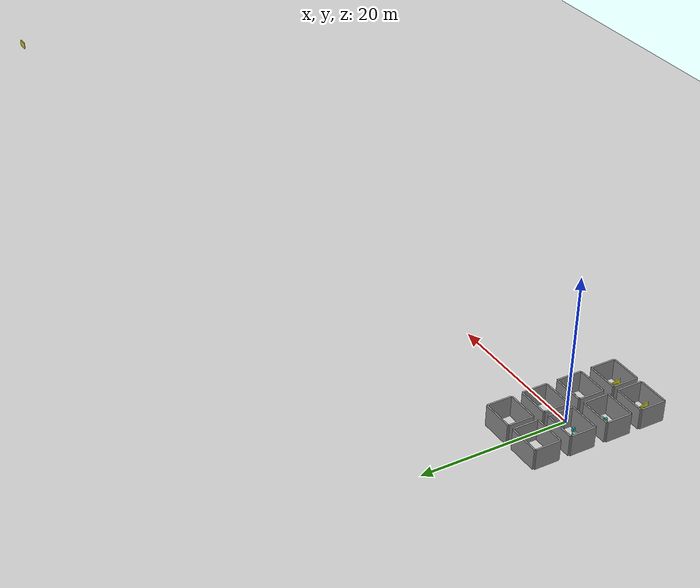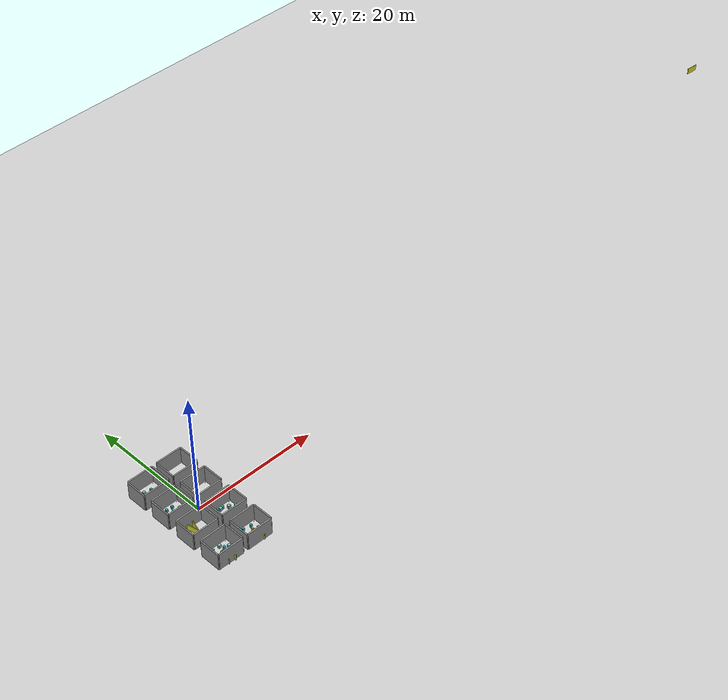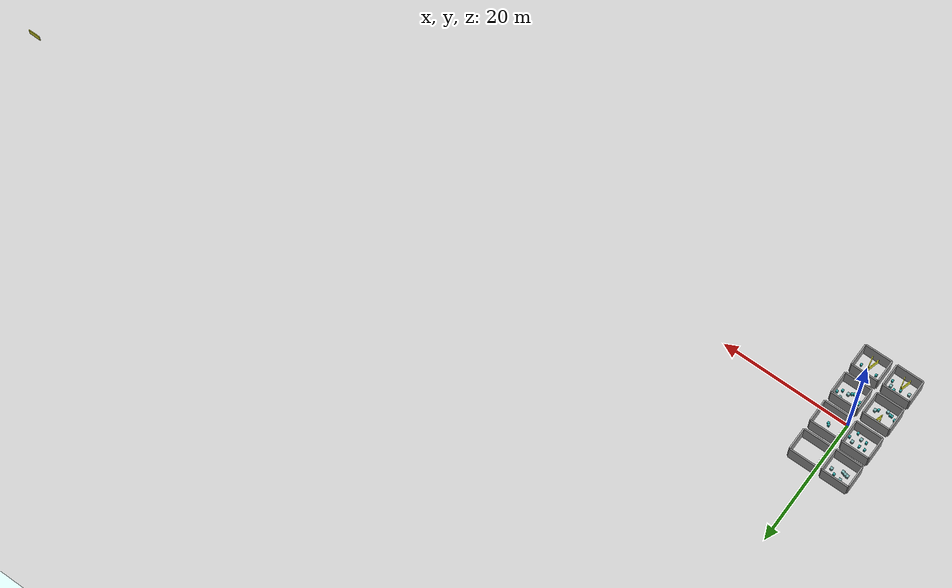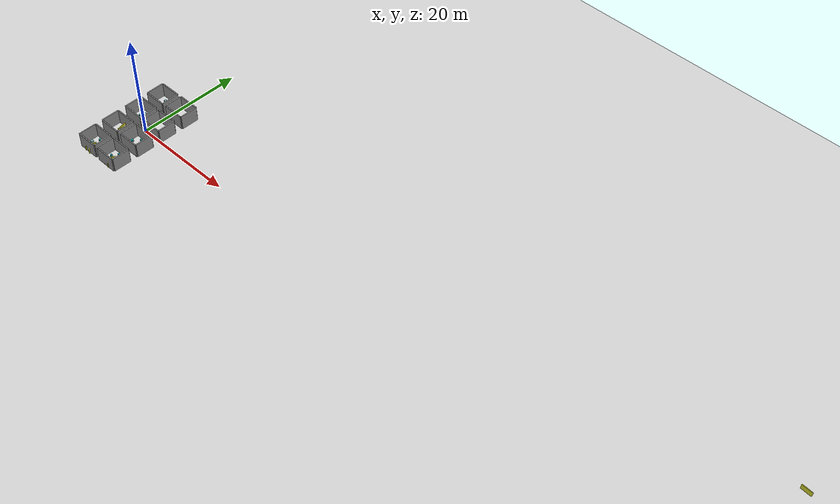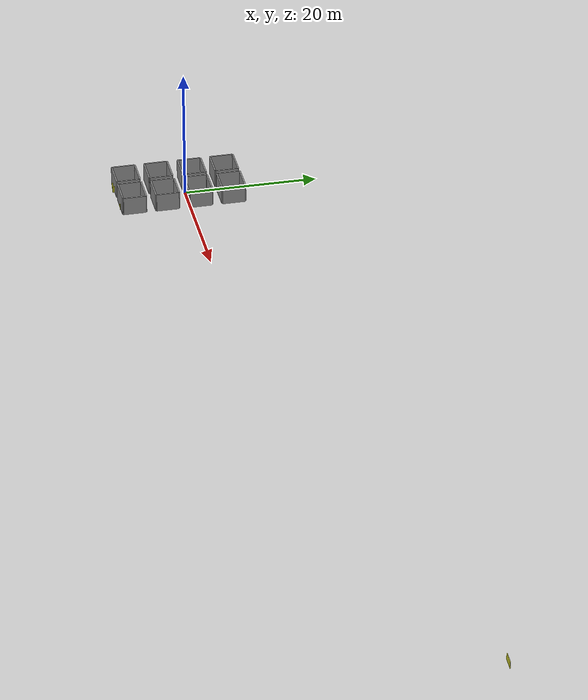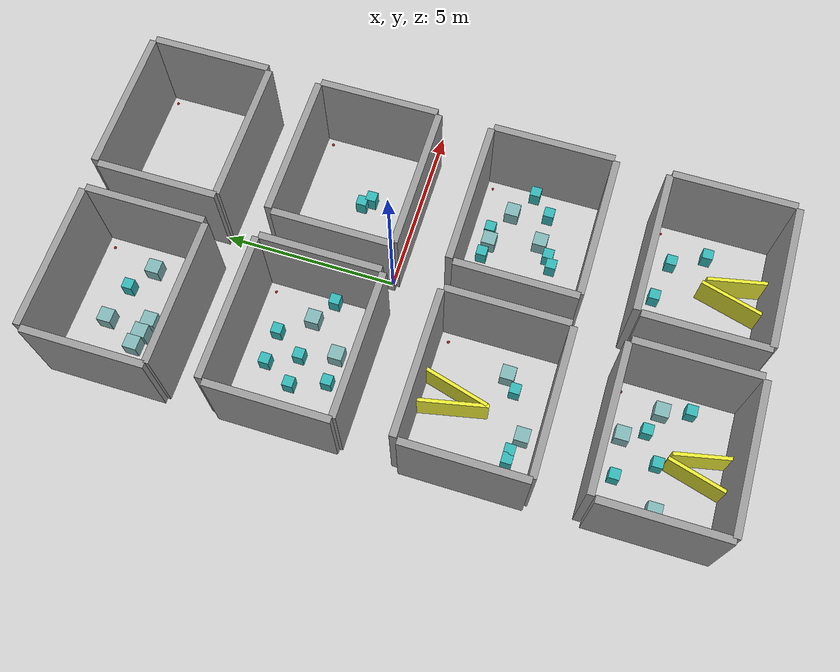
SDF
<sdf version="1.7">
 <world name="default">
  <scene><ambient>0.4 0.4 0.4 1</ambient><background>0.7 0.7 0.7 1</background><shadows>1</shadows></scene>
  <light name="sun" type="directional">
   <pose>0 0 10 0 -0 0</pose>
   <diffuse>0.8 0.8 0.8 1</diffuse>
   <specular>0.2 0.2 0.2 1</specular>
   <attenuation>
    <range>1000</range>
    <constant>0.9</constant>
    <linear>0.01</linear>
    <quadratic>0.001</quadratic>
   </attenuation>
   <direction>-0.5 0.1 -0.9</direction>
   <spot><inner_angle>0</inner_angle><outer_angle>0</outer_angle><falloff>0</falloff></spot>
  </light>
  <model name="ground_plane">
   <static>1</static>
   <link name="link">
    <collision name="collision">
     <geometry><plane><normal>0 0 1</normal><size>100 100</size></plane></geometry>
     <surface><friction><ode><mu>100</mu><mu2>50</mu2></ode></friction></surface>
    </collision>
    <visual name="visual">
     <cast_shadows>0</cast_shadows>
     <geometry><plane><normal>0 0 1</normal><size>100 100</size></plane></geometry>
     <material>
      <script><uri>file://media/materials/scripts/gazebo.material</uri><name>Gazebo/Grey</name></script>
     </material>
    </visual>
   </link>
  </model>
  <physics name="default_physics" default="0" type="ode">
   <real_time_update_rate>500000</real_time_update_rate>
   <max_step_size>0.02</max_step_size>
   <real_time_factor>0</real_time_factor>
   <ode>
    <solver>
     <type>quick</type>
     <iters>150</iters>
     <precon_iters>0</precon_iters>
     <sor>1.4</sor>
     <use_dynamic_moi_rescaling>1</use_dynamic_moi_rescaling>
    </solver>
    <constraints>
     <cfm>1e-05</cfm>
     <erp>0.2</erp>
     <contact_max_correcting_vel>2000</contact_max_correcting_vel>
     <contact_surface_layer>0.01</contact_surface_layer>
    </constraints>
   </ode>
  </physics>
  <gravity>0 0 -9.8</gravity>
  <magnetic_field>6e-06 2.3e-05 -4.2e-05</magnetic_field>
  <atmosphere type="adiabatic"/>
  <spherical_coordinates>
   <surface_model>EARTH_WGS84</surface_model>
   <latitude_deg>0</latitude_deg>
   <longitude_deg>0</longitude_deg>
   <elevation>0</elevation>
   <heading_deg>0</heading_deg>
  </spherical_coordinates>
  <audio><device>default</device></audio>
  <model name="wooden_wall_2_0">
   <link name="link_1">
    <inertial>
     <mass>1</mass>
     <inertia>
      <ixx>0.166667</ixx>
      <ixy>0</ixy>
      <ixz>0</ixz>
      <iyy>0.166667</iyy>
      <iyz>0</iyz>
      <izz>0.166667</izz>
     </inertia>
    </inertial>
    <visual name="visual">
     <geometry><box><size>2 0.1 1</size></box></geometry>
     <material>
      <lighting>1</lighting>
      <script><uri>file://media/materials/scripts/gazebo.material</uri><name>Gazebo/Grey</name></script>
      <shader type="pixel"><normal_map>__default__</normal_map></shader>
      <ambient>0.9 0.9 0.2 1</ambient>
      <diffuse>0.7 0.7 0.7 1</diffuse>
      <specular>0.01 0.01 0.01 1</specular>
      <emissive>0 0 0 1</emissive>
     </material>
    </visual>
    <collision name="collision">
     <geometry><box><size>2 0.1 1</size></box></geometry>
     <surface>
      <friction>
       <ode><mu>1</mu><mu2>1</mu2><fdir1>0 0 0</fdir1><slip1>0</slip1><slip2>0</slip2></ode>
       <torsional>
        <coefficient>1</coefficient>
        <patch_radius>0</patch_radius>
        <surface_radius>0</surface_radius>
        <use_patch_radius>1</use_patch_radius>
        <ode><slip>0</slip></ode>
       </torsional>
      </friction>
      <bounce><restitution_coefficient>0</restitution_coefficient><threshold>1e+06</threshold></bounce>
      <contact>
       <collide_without_contact>0</collide_without_contact>
       <collide_without_contact_bitmask>1</collide_without_contact_bitmask>
       <collide_bitmask>1</collide_bitmask>
       <ode>
        <soft_cfm>0</soft_cfm>
        <soft_erp>0.2</soft_erp>
        <kp>1e+13</kp>
        <kd>1</kd>
        <max_vel>0.01</max_vel>
        <min_depth>0</min_depth>
       </ode>
       <bullet>
        <split_impulse>1</split_impulse>
        <split_impulse_penetration_threshold>-0.01</split_impulse_penetration_threshold>
        <soft_cfm>0</soft_cfm>
        <soft_erp>0.2</soft_erp>
        <kp>1e+13</kp>
        <kd>1</kd>
       </bullet>
      </contact>
     </surface>
    </collision>
   </link>
   <static>0</static>
   <pose>125.678 18.5874 0.449584 -0.001475 0.052697 -0.026891</pose>
  </model>
  <model name="fl4sr_real_arena_8_target">
   <model name="fl4sr_real_arena_8">
    <model name="fl4sr_real_arena">
     <model name="grey_wall_3.4">
      <link name="link">
       <pose>0 0 1.4 0 -0 0</pose>
       <inertial>
        <mass>1</mass>
        <inertia><ixx>1</ixx><ixy>0</ixy><ixz>0</ixz><iyy>1</iyy><iyz>0</iyz><izz>1</izz></inertia>
       </inertial>
       <visual name="visual">
        <cast_shadows>0</cast_shadows>
        <geometry><box><size>3.4 0.2 2.8</size></box></geometry>
        <material>
         <script>
          <uri>model://grey_wall/materials/scripts</uri>
          <uri>model://grey_wall/materials/textures</uri>
          <name>vrc/grey_wall</name>
         </script>
         <shader type="pixel"><normal_map>__default__</normal_map></shader>
         <ambient>1 1 1 1</ambient>
         <diffuse>1 1 1 1</diffuse>
         <specular>0 0 0 1</specular>
         <emissive>0 0 0 1</emissive>
        </material>
       </visual>
       <collision name="collision">
        <geometry><box><size>3.4 0.2 2.8</size></box></geometry>
        <surface>
         <friction>
          <ode><mu>1</mu><mu2>1</mu2><fdir1>0 0 0</fdir1><slip1>0</slip1><slip2>0</slip2></ode>
          <torsional>
           <coefficient>1</coefficient>
           <patch_radius>0</patch_radius>
           <surface_radius>0</surface_radius>
           <use_patch_radius>1</use_patch_radius>
           <ode><slip>0</slip></ode>
          </torsional>
         </friction>
         <bounce><restitution_coefficient>0</restitution_coefficient><threshold>1e+06</threshold></bounce>
         <contact>
          <collide_without_contact>0</collide_without_contact>
          <collide_without_contact_bitmask>1</collide_without_contact_bitmask>
          <collide_bitmask>1</collide_bitmask>
          <ode>
           <soft_cfm>0</soft_cfm>
           <soft_erp>0.2</soft_erp>
           <kp>1e+13</kp>
           <kd>1</kd>
           <max_vel>0.01</max_vel>
           <min_depth>0</min_depth>
          </ode>
          <bullet>
           <split_impulse>1</split_impulse>
           <split_impulse_penetration_threshold>-0.01</split_impulse_penetration_threshold>
           <soft_cfm>0</soft_cfm>
           <soft_erp>0.2</soft_erp>
           <kp>1e+13</kp>
           <kd>1</kd>
          </bullet>
         </contact>
        </surface>
       </collision>
      </link>
      <static>1</static>
      <pose>2.11643 0.018849 0 0 0 -1.56899</pose>
     </model>
     <model name="grey_wall_3.4_clone">
      <link name="link">
       <pose>0 0 1.4 0 -0 0</pose>
       <inertial>
        <mass>1</mass>
        <inertia><ixx>1</ixx><ixy>0</ixy><ixz>0</ixz><iyy>1</iyy><iyz>0</iyz><izz>1</izz></inertia>
       </inertial>
       <visual name="visual">
        <cast_shadows>0</cast_shadows>
        <geometry><box><size>3.4 0.2 2.8</size></box></geometry>
        <material>
         <script>
          <uri>model://grey_wall/materials/scripts</uri>
          <uri>model://grey_wall/materials/textures</uri>
          <name>vrc/grey_wall</name>
         </script>
         <shader type="pixel"><normal_map>__default__</normal_map></shader>
         <ambient>1 1 1 1</ambient>
         <diffuse>1 1 1 1</diffuse>
         <specular>0 0 0 1</specular>
         <emissive>0 0 0 1</emissive>
        </material>
       </visual>
       <collision name="collision">
        <geometry><box><size>3.4 0.2 2.8</size></box></geometry>
        <surface>
         <friction>
          <ode><mu>1</mu><mu2>1</mu2><fdir1>0 0 0</fdir1><slip1>0</slip1><slip2>0</slip2></ode>
          <torsional>
           <coefficient>1</coefficient>
           <patch_radius>0</patch_radius>
           <surface_radius>0</surface_radius>
           <use_patch_radius>1</use_patch_radius>
           <ode><slip>0</slip></ode>
          </torsional>
         </friction>
         <bounce><restitution_coefficient>0</restitution_coefficient><threshold>1e+06</threshold></bounce>
         <contact>
          <collide_without_contact>0</collide_without_contact>
          <collide_without_contact_bitmask>1</collide_without_contact_bitmask>
          <collide_bitmask>1</collide_bitmask>
          <ode>
           <soft_cfm>0</soft_cfm>
           <soft_erp>0.2</soft_erp>
           <kp>1e+13</kp>
           <kd>1</kd>
           <max_vel>0.01</max_vel>
           <min_depth>0</min_depth>
          </ode>
          <bullet>
           <split_impulse>1</split_impulse>
           <split_impulse_penetration_threshold>-0.01</split_impulse_penetration_threshold>
           <soft_cfm>0</soft_cfm>
           <soft_erp>0.2</soft_erp>
           <kp>1e+13</kp>
           <kd>1</kd>
          </bullet>
         </contact>
        </surface>
       </collision>
      </link>
      <static>1</static>
      <pose>-2.10723 -0.050721 0 0 0 -1.56899</pose>
     </model>
     <model name="grey_wall_4.1">
      <link name="link">
       <pose>0 0 1.4 0 -0 0</pose>
       <inertial>
        <mass>1</mass>
        <inertia><ixx>1</ixx><ixy>0</ixy><ixz>0</ixz><iyy>1</iyy><iyz>0</iyz><izz>1</izz></inertia>
       </inertial>
       <visual name="visual">
        <cast_shadows>0</cast_shadows>
        <geometry><box><size>4.1 0.2 2.8</size></box></geometry>
        <material>
         <script>
          <uri>model://grey_wall/materials/scripts</uri>
          <uri>model://grey_wall/materials/textures</uri>
          <name>vrc/grey_wall</name>
         </script>
         <shader type="pixel"><normal_map>__default__</normal_map></shader>
         <ambient>1 1 1 1</ambient>
         <diffuse>1 1 1 1</diffuse>
         <specular>0 0 0 1</specular>
         <emissive>0 0 0 1</emissive>
        </material>
       </visual>
       <collision name="collision">
        <geometry><box><size>4.1 0.2 2.8</size></box></geometry>
        <surface>
         <friction>
          <ode><mu>1</mu><mu2>1</mu2><fdir1>0 0 0</fdir1><slip1>0</slip1><slip2>0</slip2></ode>
          <torsional>
           <coefficient>1</coefficient>
           <patch_radius>0</patch_radius>
           <surface_radius>0</surface_radius>
           <use_patch_radius>1</use_patch_radius>
           <ode><slip>0</slip></ode>
          </torsional>
         </friction>
         <bounce><restitution_coefficient>0</restitution_coefficient><threshold>1e+06</threshold></bounce>
         <contact>
          <collide_without_contact>0</collide_without_contact>
          <collide_without_contact_bitmask>1</collide_without_contact_bitmask>
          <collide_bitmask>1</collide_bitmask>
          <ode>
           <soft_cfm>0</soft_cfm>
           <soft_erp>0.2</soft_erp>
           <kp>1e+13</kp>
           <kd>1</kd>
           <max_vel>0.01</max_vel>
           <min_depth>0</min_depth>
          </ode>
          <bullet>
           <split_impulse>1</split_impulse>
           <split_impulse_penetration_threshold>-0.01</split_impulse_penetration_threshold>
           <soft_cfm>0</soft_cfm>
           <soft_erp>0.2</soft_erp>
           <kp>1e+13</kp>
           <kd>1</kd>
          </bullet>
         </contact>
        </surface>
       </collision>
      </link>
      <static>1</static>
      <pose>-0.006371 1.77257 0 0 -0 0</pose>
     </model>
     <model name="grey_wall_4.1_clone">
      <link name="link">
       <pose>0 0 1.4 0 -0 0</pose>
       <inertial>
        <mass>1</mass>
        <inertia><ixx>1</ixx><ixy>0</ixy><ixz>0</ixz><iyy>1</iyy><iyz>0</iyz><izz>1</izz></inertia>
       </inertial>
       <visual name="visual">
        <cast_shadows>0</cast_shadows>
        <geometry><box><size>4.1 0.2 2.8</size></box></geometry>
        <material>
         <script>
          <uri>model://grey_wall/materials/scripts</uri>
          <uri>model://grey_wall/materials/textures</uri>
          <name>vrc/grey_wall</name>
         </script>
         <shader type="pixel"><normal_map>__default__</normal_map></shader>
         <ambient>1 1 1 1</ambient>
         <diffuse>1 1 1 1</diffuse>
         <specular>0 0 0 1</specular>
         <emissive>0 0 0 1</emissive>
        </material>
       </visual>
       <collision name="collision">
        <geometry><box><size>4.1 0.2 2.8</size></box></geometry>
        <surface>
         <friction>
          <ode><mu>1</mu><mu2>1</mu2><fdir1>0 0 0</fdir1><slip1>0</slip1><slip2>0</slip2></ode>
          <torsional>
           <coefficient>1</coefficient>
           <patch_radius>0</patch_radius>
           <surface_radius>0</surface_radius>
           <use_patch_radius>1</use_patch_radius>
           <ode><slip>0</slip></ode>
          </torsional>
         </friction>
         <bounce><restitution_coefficient>0</restitution_coefficient><threshold>1e+06</threshold></bounce>
         <contact>
          <collide_without_contact>0</collide_without_contact>
          <collide_without_contact_bitmask>1</collide_without_contact_bitmask>
          <collide_bitmask>1</collide_bitmask>
          <ode>
           <soft_cfm>0</soft_cfm>
           <soft_erp>0.2</soft_erp>
           <kp>1e+13</kp>
           <kd>1</kd>
           <max_vel>0.01</max_vel>
           <min_depth>0</min_depth>
          </ode>
          <bullet>
           <split_impulse>1</split_impulse>
           <split_impulse_penetration_threshold>-0.01</split_impulse_penetration_threshold>
           <soft_cfm>0</soft_cfm>
           <soft_erp>0.2</soft_erp>
           <kp>1e+13</kp>
           <kd>1</kd>
          </bullet>
         </contact>
        </surface>
       </collision>
      </link>
      <static>1</static>
      <pose>-0.002836 -1.7407 0 0 -0 0</pose>
     </model>
     <static>0</static>
     <pose>-2.96355 3.63989 0 0 -0 0</pose>
    </model>
    <model name="fl4sr_real_arena_0">
     <model name="grey_wall_3.4">
      <link name="link">
       <pose>0 0 1.4 0 -0 0</pose>
       <inertial>
        <mass>1</mass>
        <inertia><ixx>1</ixx><ixy>0</ixy><ixz>0</ixz><iyy>1</iyy><iyz>0</iyz><izz>1</izz></inertia>
       </inertial>
       <visual name="visual">
        <cast_shadows>0</cast_shadows>
        <geometry><box><size>3.4 0.2 2.8</size></box></geometry>
        <material>
         <script>
          <uri>model://grey_wall/materials/scripts</uri>
          <uri>model://grey_wall/materials/textures</uri>
          <name>vrc/grey_wall</name>
         </script>
         <shader type="pixel"><normal_map>__default__</normal_map></shader>
         <ambient>1 1 1 1</ambient>
         <diffuse>1 1 1 1</diffuse>
         <specular>0 0 0 1</specular>
         <emissive>0 0 0 1</emissive>
        </material>
       </visual>
       <collision name="collision">
        <geometry><box><size>3.4 0.2 2.8</size></box></geometry>
        <surface>
         <friction>
          <ode><mu>1</mu><mu2>1</mu2><fdir1>0 0 0</fdir1><slip1>0</slip1><slip2>0</slip2></ode>
          <torsional>
           <coefficient>1</coefficient>
           <patch_radius>0</patch_radius>
           <surface_radius>0</surface_radius>
           <use_patch_radius>1</use_patch_radius>
           <ode><slip>0</slip></ode>
          </torsional>
         </friction>
         <bounce><restitution_coefficient>0</restitution_coefficient><threshold>1e+06</threshold></bounce>
         <contact>
          <collide_without_contact>0</collide_without_contact>
          <collide_without_contact_bitmask>1</collide_without_contact_bitmask>
          <collide_bitmask>1</collide_bitmask>
          <ode>
           <soft_cfm>0</soft_cfm>
           <soft_erp>0.2</soft_erp>
           <kp>1e+13</kp>
           <kd>1</kd>
           <max_vel>0.01</max_vel>
           <min_depth>0</min_depth>
          </ode>
          <bullet>
           <split_impulse>1</split_impulse>
           <split_impulse_penetration_threshold>-0.01</split_impulse_penetration_threshold>
           <soft_cfm>0</soft_cfm>
           <soft_erp>0.2</soft_erp>
           <kp>1e+13</kp>
           <kd>1</kd>
          </bullet>
         </contact>
        </surface>
       </collision>
      </link>
      <static>1</static>
      <pose>2.11643 0.018849 0 0 0 -1.56899</pose>
     </model>
     <model name="grey_wall_3.4_clone">
      <link name="link">
       <pose>0 0 1.4 0 -0 0</pose>
       <inertial>
        <mass>1</mass>
        <inertia><ixx>1</ixx><ixy>0</ixy><ixz>0</ixz><iyy>1</iyy><iyz>0</iyz><izz>1</izz></inertia>
       </inertial>
       <visual name="visual">
        <cast_shadows>0</cast_shadows>
        <geometry><box><size>3.4 0.2 2.8</size></box></geometry>
        <material>
         <script>
          <uri>model://grey_wall/materials/scripts</uri>
          <uri>model://grey_wall/materials/textures</uri>
          <name>vrc/grey_wall</name>
         </script>
         <shader type="pixel"><normal_map>__default__</normal_map></shader>
         <ambient>1 1 1 1</ambient>
         <diffuse>1 1 1 1</diffuse>
         <specular>0 0 0 1</specular>
         <emissive>0 0 0 1</emissive>
        </material>
       </visual>
       <collision name="collision">
        <geometry><box><size>3.4 0.2 2.8</size></box></geometry>
        <surface>
         <friction>
          <ode><mu>1</mu><mu2>1</mu2><fdir1>0 0 0</fdir1><slip1>0</slip1><slip2>0</slip2></ode>
          <torsional>
           <coefficient>1</coefficient>
           <patch_radius>0</patch_radius>
           <surface_radius>0</surface_radius>
           <use_patch_radius>1</use_patch_radius>
           <ode><slip>0</slip></ode>
          </torsional>
         </friction>
         <bounce><restitution_coefficient>0</restitution_coefficient><threshold>1e+06</threshold></bounce>
         <contact>
          <collide_without_contact>0</collide_without_contact>
          <collide_without_contact_bitmask>1</collide_without_contact_bitmask>
          <collide_bitmask>1</collide_bitmask>
          <ode>
           <soft_cfm>0</soft_cfm>
           <soft_erp>0.2</soft_erp>
           <kp>1e+13</kp>
           <kd>1</kd>
           <max_vel>0.01</max_vel>
           <min_depth>0</min_depth>
          </ode>
          <bullet>
           <split_impulse>1</split_impulse>
           <split_impulse_penetration_threshold>-0.01</split_impulse_penetration_threshold>
           <soft_cfm>0</soft_cfm>
           <soft_erp>0.2</soft_erp>
           <kp>1e+13</kp>
           <kd>1</kd>
          </bullet>
         </contact>
        </surface>
       </collision>
      </link>
      <static>1</static>
      <pose>-2.10723 -0.050721 0 0 0 -1.56899</pose>
     </model>
     <model name="grey_wall_4.1">
      <link name="link">
       <pose>0 0 1.4 0 -0 0</pose>
       <inertial>
        <mass>1</mass>
        <inertia><ixx>1</ixx><ixy>0</ixy><ixz>0</ixz><iyy>1</iyy><iyz>0</iyz><izz>1</izz></inertia>
       </inertial>
       <visual name="visual">
        <cast_shadows>0</cast_shadows>
        <geometry><box><size>4.1 0.2 2.8</size></box></geometry>
        <material>
         <script>
          <uri>model://grey_wall/materials/scripts</uri>
          <uri>model://grey_wall/materials/textures</uri>
          <name>vrc/grey_wall</name>
         </script>
         <shader type="pixel"><normal_map>__default__</normal_map></shader>
         <ambient>1 1 1 1</ambient>
         <diffuse>1 1 1 1</diffuse>
         <specular>0 0 0 1</specular>
         <emissive>0 0 0 1</emissive>
        </material>
       </visual>
       <collision name="collision">
        <geometry><box><size>4.1 0.2 2.8</size></box></geometry>
        <surface>
         <friction>
          <ode><mu>1</mu><mu2>1</mu2><fdir1>0 0 0</fdir1><slip1>0</slip1><slip2>0</slip2></ode>
          <torsional>
           <coefficient>1</coefficient>
           <patch_radius>0</patch_radius>
           <surface_radius>0</surface_radius>
           <use_patch_radius>1</use_patch_radius>
           <ode><slip>0</slip></ode>
          </torsional>
         </friction>
         <bounce><restitution_coefficient>0</restitution_coefficient><threshold>1e+06</threshold></bounce>
         <contact>
          <collide_without_contact>0</collide_without_contact>
          <collide_without_contact_bitmask>1</collide_without_contact_bitmask>
          <collide_bitmask>1</collide_bitmask>
          <ode>
           <soft_cfm>0</soft_cfm>
           <soft_erp>0.2</soft_erp>
           <kp>1e+13</kp>
           <kd>1</kd>
           <max_vel>0.01</max_vel>
           <min_depth>0</min_depth>
          </ode>
          <bullet>
           <split_impulse>1</split_impulse>
           <split_impulse_penetration_threshold>-0.01</split_impulse_penetration_threshold>
           <soft_cfm>0</soft_cfm>
           <soft_erp>0.2</soft_erp>
           <kp>1e+13</kp>
           <kd>1</kd>
          </bullet>
         </contact>
        </surface>
       </collision>
      </link>
      <static>1</static>
      <pose>-0.006371 1.77257 0 0 -0 0</pose>
     </model>
     <model name="grey_wall_4.1_clone">
      <link name="link">
       <pose>0 0 1.4 0 -0 0</pose>
       <inertial>
        <mass>1</mass>
        <inertia><ixx>1</ixx><ixy>0</ixy><ixz>0</ixz><iyy>1</iyy><iyz>0</iyz><izz>1</izz></inertia>
       </inertial>
       <visual name="visual">
        <cast_shadows>0</cast_shadows>
        <geometry><box><size>4.1 0.2 2.8</size></box></geometry>
        <material>
         <script>
          <uri>model://grey_wall/materials/scripts</uri>
          <uri>model://grey_wall/materials/textures</uri>
          <name>vrc/grey_wall</name>
         </script>
         <shader type="pixel"><normal_map>__default__</normal_map></shader>
         <ambient>1 1 1 1</ambient>
         <diffuse>1 1 1 1</diffuse>
         <specular>0 0 0 1</specular>
         <emissive>0 0 0 1</emissive>
        </material>
       </visual>
       <collision name="collision">
        <geometry><box><size>4.1 0.2 2.8</size></box></geometry>
        <surface>
         <friction>
          <ode><mu>1</mu><mu2>1</mu2><fdir1>0 0 0</fdir1><slip1>0</slip1><slip2>0</slip2></ode>
          <torsional>
           <coefficient>1</coefficient>
           <patch_radius>0</patch_radius>
           <surface_radius>0</surface_radius>
           <use_patch_radius>1</use_patch_radius>
           <ode><slip>0</slip></ode>
          </torsional>
         </friction>
         <bounce><restitution_coefficient>0</restitution_coefficient><threshold>1e+06</threshold></bounce>
         <contact>
          <collide_without_contact>0</collide_without_contact>
          <collide_without_contact_bitmask>1</collide_without_contact_bitmask>
          <collide_bitmask>1</collide_bitmask>
          <ode>
           <soft_cfm>0</soft_cfm>
           <soft_erp>0.2</soft_erp>
           <kp>1e+13</kp>
           <kd>1</kd>
           <max_vel>0.01</max_vel>
           <min_depth>0</min_depth>
          </ode>
          <bullet>
           <split_impulse>1</split_impulse>
           <split_impulse_penetration_threshold>-0.01</split_impulse_penetration_threshold>
           <soft_cfm>0</soft_cfm>
           <soft_erp>0.2</soft_erp>
           <kp>1e+13</kp>
           <kd>1</kd>
          </bullet>
         </contact>
        </surface>
       </collision>
      </link>
      <static>1</static>
      <pose>-0.002836 -1.7407 0 0 -0 0</pose>
     </model>
     <static>0</static>
     <pose>-2.96018 -1.35128 0 0 -0 0</pose>
    </model>
    <model name="fl4sr_real_arena_0_clone">
     <model name="grey_wall_3.4">
      <link name="link">
       <pose>0 0 1.4 0 -0 0</pose>
       <inertial>
        <mass>1</mass>
        <inertia><ixx>1</ixx><ixy>0</ixy><ixz>0</ixz><iyy>1</iyy><iyz>0</iyz><izz>1</izz></inertia>
       </inertial>
       <visual name="visual">
        <cast_shadows>0</cast_shadows>
        <geometry><box><size>3.4 0.2 2.8</size></box></geometry>
        <material>
         <script>
          <uri>model://grey_wall/materials/scripts</uri>
          <uri>model://grey_wall/materials/textures</uri>
          <name>vrc/grey_wall</name>
         </script>
         <shader type="pixel"><normal_map>__default__</normal_map></shader>
         <ambient>1 1 1 1</ambient>
         <diffuse>1 1 1 1</diffuse>
         <specular>0 0 0 1</specular>
         <emissive>0 0 0 1</emissive>
        </material>
       </visual>
       <collision name="collision">
        <geometry><box><size>3.4 0.2 2.8</size></box></geometry>
        <surface>
         <friction>
          <ode><mu>1</mu><mu2>1</mu2><fdir1>0 0 0</fdir1><slip1>0</slip1><slip2>0</slip2></ode>
          <torsional>
           <coefficient>1</coefficient>
           <patch_radius>0</patch_radius>
           <surface_radius>0</surface_radius>
           <use_patch_radius>1</use_patch_radius>
           <ode><slip>0</slip></ode>
          </torsional>
         </friction>
         <bounce><restitution_coefficient>0</restitution_coefficient><threshold>1e+06</threshold></bounce>
         <contact>
          <collide_without_contact>0</collide_without_contact>
          <collide_without_contact_bitmask>1</collide_without_contact_bitmask>
          <collide_bitmask>1</collide_bitmask>
          <ode>
           <soft_cfm>0</soft_cfm>
           <soft_erp>0.2</soft_erp>
           <kp>1e+13</kp>
           <kd>1</kd>
           <max_vel>0.01</max_vel>
           <min_depth>0</min_depth>
          </ode>
          <bullet>
           <split_impulse>1</split_impulse>
           <split_impulse_penetration_threshold>-0.01</split_impulse_penetration_threshold>
           <soft_cfm>0</soft_cfm>
           <soft_erp>0.2</soft_erp>
           <kp>1e+13</kp>
           <kd>1</kd>
          </bullet>
         </contact>
        </surface>
       </collision>
      </link>
      <static>1</static>
      <pose>2.11643 0.018849 0 0 0 -1.56899</pose>
     </model>
     <model name="grey_wall_3.4_clone">
      <link name="link">
       <pose>0 0 1.4 0 -0 0</pose>
       <inertial>
        <mass>1</mass>
        <inertia><ixx>1</ixx><ixy>0</ixy><ixz>0</ixz><iyy>1</iyy><iyz>0</iyz><izz>1</izz></inertia>
       </inertial>
       <visual name="visual">
        <cast_shadows>0</cast_shadows>
        <geometry><box><size>3.4 0.2 2.8</size></box></geometry>
        <material>
         <script>
          <uri>model://grey_wall/materials/scripts</uri>
          <uri>model://grey_wall/materials/textures</uri>
          <name>vrc/grey_wall</name>
         </script>
         <shader type="pixel"><normal_map>__default__</normal_map></shader>
         <ambient>1 1 1 1</ambient>
         <diffuse>1 1 1 1</diffuse>
         <specular>0 0 0 1</specular>
         <emissive>0 0 0 1</emissive>
        </material>
       </visual>
       <collision name="collision">
        <geometry><box><size>3.4 0.2 2.8</size></box></geometry>
        <surface>
         <friction>
          <ode><mu>1</mu><mu2>1</mu2><fdir1>0 0 0</fdir1><slip1>0</slip1><slip2>0</slip2></ode>
          <torsional>
           <coefficient>1</coefficient>
           <patch_radius>0</patch_radius>
           <surface_radius>0</surface_radius>
           <use_patch_radius>1</use_patch_radius>
           <ode><slip>0</slip></ode>
          </torsional>
         </friction>
         <bounce><restitution_coefficient>0</restitution_coefficient><threshold>1e+06</threshold></bounce>
         <contact>
          <collide_without_contact>0</collide_without_contact>
          <collide_without_contact_bitmask>1</collide_without_contact_bitmask>
          <collide_bitmask>1</collide_bitmask>
          <ode>
           <soft_cfm>0</soft_cfm>
           <soft_erp>0.2</soft_erp>
           <kp>1e+13</kp>
           <kd>1</kd>
           <max_vel>0.01</max_vel>
           <min_depth>0</min_depth>
          </ode>
          <bullet>
           <split_impulse>1</split_impulse>
           <split_impulse_penetration_threshold>-0.01</split_impulse_penetration_threshold>
           <soft_cfm>0</soft_cfm>
           <soft_erp>0.2</soft_erp>
           <kp>1e+13</kp>
           <kd>1</kd>
          </bullet>
         </contact>
        </surface>
       </collision>
      </link>
      <static>1</static>
      <pose>-2.10723 -0.050721 0 0 0 -1.56899</pose>
     </model>
     <model name="grey_wall_4.1">
      <link name="link">
       <pose>0 0 1.4 0 -0 0</pose>
       <inertial>
        <mass>1</mass>
        <inertia><ixx>1</ixx><ixy>0</ixy><ixz>0</ixz><iyy>1</iyy><iyz>0</iyz><izz>1</izz></inertia>
       </inertial>
       <visual name="visual">
        <cast_shadows>0</cast_shadows>
        <geometry><box><size>4.1 0.2 2.8</size></box></geometry>
        <material>
         <script>
          <uri>model://grey_wall/materials/scripts</uri>
          <uri>model://grey_wall/materials/textures</uri>
          <name>vrc/grey_wall</name>
         </script>
         <shader type="pixel"><normal_map>__default__</normal_map></shader>
         <ambient>1 1 1 1</ambient>
         <diffuse>1 1 1 1</diffuse>
         <specular>0 0 0 1</specular>
         <emissive>0 0 0 1</emissive>
        </material>
       </visual>
       <collision name="collision">
        <geometry><box><size>4.1 0.2 2.8</size></box></geometry>
        <surface>
         <friction>
          <ode><mu>1</mu><mu2>1</mu2><fdir1>0 0 0</fdir1><slip1>0</slip1><slip2>0</slip2></ode>
          <torsional>
           <coefficient>1</coefficient>
           <patch_radius>0</patch_radius>
           <surface_radius>0</surface_radius>
           <use_patch_radius>1</use_patch_radius>
           <ode><slip>0</slip></ode>
          </torsional>
         </friction>
         <bounce><restitution_coefficient>0</restitution_coefficient><threshold>1e+06</threshold></bounce>
         <contact>
          <collide_without_contact>0</collide_without_contact>
          <collide_without_contact_bitmask>1</collide_without_contact_bitmask>
          <collide_bitmask>1</collide_bitmask>
          <ode>
           <soft_cfm>0</soft_cfm>
           <soft_erp>0.2</soft_erp>
           <kp>1e+13</kp>
           <kd>1</kd>
           <max_vel>0.01</max_vel>
           <min_depth>0</min_depth>
          </ode>
          <bullet>
           <split_impulse>1</split_impulse>
           <split_impulse_penetration_threshold>-0.01</split_impulse_penetration_threshold>
           <soft_cfm>0</soft_cfm>
           <soft_erp>0.2</soft_erp>
           <kp>1e+13</kp>
           <kd>1</kd>
          </bullet>
         </contact>
        </surface>
       </collision>
      </link>
      <static>1</static>
      <pose>-0.006371 1.77257 0 0 -0 0</pose>
     </model>
     <model name="grey_wall_4.1_clone">
      <link name="link">
       <pose>0 0 1.4 0 -0 0</pose>
       <inertial>
        <mass>1</mass>
        <inertia><ixx>1</ixx><ixy>0</ixy><ixz>0</ixz><iyy>1</iyy><iyz>0</iyz><izz>1</izz></inertia>
       </inertial>
       <visual name="visual">
        <cast_shadows>0</cast_shadows>
        <geometry><box><size>4.1 0.2 2.8</size></box></geometry>
        <material>
         <script>
          <uri>model://grey_wall/materials/scripts</uri>
          <uri>model://grey_wall/materials/textures</uri>
          <name>vrc/grey_wall</name>
         </script>
         <shader type="pixel"><normal_map>__default__</normal_map></shader>
         <ambient>1 1 1 1</ambient>
         <diffuse>1 1 1 1</diffuse>
         <specular>0 0 0 1</specular>
         <emissive>0 0 0 1</emissive>
        </material>
       </visual>
       <collision name="collision">
        <geometry><box><size>4.1 0.2 2.8</size></box></geometry>
        <surface>
         <friction>
          <ode><mu>1</mu><mu2>1</mu2><fdir1>0 0 0</fdir1><slip1>0</slip1><slip2>0</slip2></ode>
          <torsional>
           <coefficient>1</coefficient>
           <patch_radius>0</patch_radius>
           <surface_radius>0</surface_radius>
           <use_patch_radius>1</use_patch_radius>
           <ode><slip>0</slip></ode>
          </torsional>
         </friction>
         <bounce><restitution_coefficient>0</restitution_coefficient><threshold>1e+06</threshold></bounce>
         <contact>
          <collide_without_contact>0</collide_without_contact>
          <collide_without_contact_bitmask>1</collide_without_contact_bitmask>
          <collide_bitmask>1</collide_bitmask>
          <ode>
           <soft_cfm>0</soft_cfm>
           <soft_erp>0.2</soft_erp>
           <kp>1e+13</kp>
           <kd>1</kd>
           <max_vel>0.01</max_vel>
           <min_depth>0</min_depth>
          </ode>
          <bullet>
           <split_impulse>1</split_impulse>
           <split_impulse_penetration_threshold>-0.01</split_impulse_penetration_threshold>
           <soft_cfm>0</soft_cfm>
           <soft_erp>0.2</soft_erp>
           <kp>1e+13</kp>
           <kd>1</kd>
          </bullet>
         </contact>
        </surface>
       </collision>
      </link>
      <static>1</static>
      <pose>-0.002836 -1.7407 0 0 -0 0</pose>
     </model>
     <static>0</static>
     <pose>-7.97946 3.57621 0 0 -0 0</pose>
    </model>
    <model name="fl4sr_real_arena_0_clone_0">
     <model name="grey_wall_3.4">
      <link name="link">
       <pose>0 0 1.4 0 -0 0</pose>
       <inertial>
        <mass>1</mass>
        <inertia><ixx>1</ixx><ixy>0</ixy><ixz>0</ixz><iyy>1</iyy><iyz>0</iyz><izz>1</izz></inertia>
       </inertial>
       <visual name="visual">
        <cast_shadows>0</cast_shadows>
        <geometry><box><size>3.4 0.2 2.8</size></box></geometry>
        <material>
         <script>
          <uri>model://grey_wall/materials/scripts</uri>
          <uri>model://grey_wall/materials/textures</uri>
          <name>vrc/grey_wall</name>
         </script>
         <shader type="pixel"><normal_map>__default__</normal_map></shader>
         <ambient>1 1 1 1</ambient>
         <diffuse>1 1 1 1</diffuse>
         <specular>0 0 0 1</specular>
         <emissive>0 0 0 1</emissive>
        </material>
       </visual>
       <collision name="collision">
        <geometry><box><size>3.4 0.2 2.8</size></box></geometry>
        <surface>
         <friction>
          <ode><mu>1</mu><mu2>1</mu2><fdir1>0 0 0</fdir1><slip1>0</slip1><slip2>0</slip2></ode>
          <torsional>
           <coefficient>1</coefficient>
           <patch_radius>0</patch_radius>
           <surface_radius>0</surface_radius>
           <use_patch_radius>1</use_patch_radius>
           <ode><slip>0</slip></ode>
          </torsional>
         </friction>
         <bounce><restitution_coefficient>0</restitution_coefficient><threshold>1e+06</threshold></bounce>
         <contact>
          <collide_without_contact>0</collide_without_contact>
          <collide_without_contact_bitmask>1</collide_without_contact_bitmask>
          <collide_bitmask>1</collide_bitmask>
          <ode>
           <soft_cfm>0</soft_cfm>
           <soft_erp>0.2</soft_erp>
           <kp>1e+13</kp>
           <kd>1</kd>
           <max_vel>0.01</max_vel>
           <min_depth>0</min_depth>
          </ode>
          <bullet>
           <split_impulse>1</split_impulse>
           <split_impulse_penetration_threshold>-0.01</split_impulse_penetration_threshold>
           <soft_cfm>0</soft_cfm>
           <soft_erp>0.2</soft_erp>
           <kp>1e+13</kp>
           <kd>1</kd>
          </bullet>
         </contact>
        </surface>
       </collision>
      </link>
      <static>1</static>
      <pose>2.11643 0.018849 0 0 0 -1.56899</pose>
     </model>
     <model name="grey_wall_3.4_clone">
      <link name="link">
       <pose>0 0 1.4 0 -0 0</pose>
       <inertial>
        <mass>1</mass>
        <inertia><ixx>1</ixx><ixy>0</ixy><ixz>0</ixz><iyy>1</iyy><iyz>0</iyz><izz>1</izz></inertia>
       </inertial>
       <visual name="visual">
        <cast_shadows>0</cast_shadows>
        <geometry><box><size>3.4 0.2 2.8</size></box></geometry>
        <material>
         <script>
          <uri>model://grey_wall/materials/scripts</uri>
          <uri>model://grey_wall/materials/textures</uri>
          <name>vrc/grey_wall</name>
         </script>
         <shader type="pixel"><normal_map>__default__</normal_map></shader>
         <ambient>1 1 1 1</ambient>
         <diffuse>1 1 1 1</diffuse>
         <specular>0 0 0 1</specular>
         <emissive>0 0 0 1</emissive>
        </material>
       </visual>
       <collision name="collision">
        <geometry><box><size>3.4 0.2 2.8</size></box></geometry>
        <surface>
         <friction>
          <ode><mu>1</mu><mu2>1</mu2><fdir1>0 0 0</fdir1><slip1>0</slip1><slip2>0</slip2></ode>
          <torsional>
           <coefficient>1</coefficient>
           <patch_radius>0</patch_radius>
           <surface_radius>0</surface_radius>
           <use_patch_radius>1</use_patch_radius>
           <ode><slip>0</slip></ode>
          </torsional>
         </friction>
         <bounce><restitution_coefficient>0</restitution_coefficient><threshold>1e+06</threshold></bounce>
         <contact>
          <collide_without_contact>0</collide_without_contact>
          <collide_without_contact_bitmask>1</collide_without_contact_bitmask>
          <collide_bitmask>1</collide_bitmask>
          <ode>
           <soft_cfm>0</soft_cfm>
           <soft_erp>0.2</soft_erp>
           <kp>1e+13</kp>
           <kd>1</kd>
           <max_vel>0.01</max_vel>
           <min_depth>0</min_depth>
          </ode>
          <bullet>
           <split_impulse>1</split_impulse>
           <split_impulse_penetration_threshold>-0.01</split_impulse_penetration_threshold>
           <soft_cfm>0</soft_cfm>
           <soft_erp>0.2</soft_erp>
           <kp>1e+13</kp>
           <kd>1</kd>
          </bullet>
         </contact>
        </surface>
       </collision>
      </link>
      <static>1</static>
      <pose>-2.10723 -0.050721 0 0 0 -1.56899</pose>
     </model>
     <model name="grey_wall_4.1">
      <link name="link">
       <pose>0 0 1.4 0 -0 0</pose>
       <inertial>
        <mass>1</mass>
        <inertia><ixx>1</ixx><ixy>0</ixy><ixz>0</ixz><iyy>1</iyy><iyz>0</iyz><izz>1</izz></inertia>
       </inertial>
       <visual name="visual">
        <cast_shadows>0</cast_shadows>
        <geometry><box><size>4.1 0.2 2.8</size></box></geometry>
        <material>
         <script>
          <uri>model://grey_wall/materials/scripts</uri>
          <uri>model://grey_wall/materials/textures</uri>
          <name>vrc/grey_wall</name>
         </script>
         <shader type="pixel"><normal_map>__default__</normal_map></shader>
         <ambient>1 1 1 1</ambient>
         <diffuse>1 1 1 1</diffuse>
         <specular>0 0 0 1</specular>
         <emissive>0 0 0 1</emissive>
        </material>
       </visual>
       <collision name="collision">
        <geometry><box><size>4.1 0.2 2.8</size></box></geometry>
        <surface>
         <friction>
          <ode><mu>1</mu><mu2>1</mu2><fdir1>0 0 0</fdir1><slip1>0</slip1><slip2>0</slip2></ode>
          <torsional>
           <coefficient>1</coefficient>
           <patch_radius>0</patch_radius>
           <surface_radius>0</surface_radius>
           <use_patch_radius>1</use_patch_radius>
           <ode><slip>0</slip></ode>
          </torsional>
         </friction>
         <bounce><restitution_coefficient>0</restitution_coefficient><threshold>1e+06</threshold></bounce>
         <contact>
          <collide_without_contact>0</collide_without_contact>
          <collide_without_contact_bitmask>1</collide_without_contact_bitmask>
          <collide_bitmask>1</collide_bitmask>
          <ode>
           <soft_cfm>0</soft_cfm>
           <soft_erp>0.2</soft_erp>
           <kp>1e+13</kp>
           <kd>1</kd>
           <max_vel>0.01</max_vel>
           <min_depth>0</min_depth>
          </ode>
          <bullet>
           <split_impulse>1</split_impulse>
           <split_impulse_penetration_threshold>-0.01</split_impulse_penetration_threshold>
           <soft_cfm>0</soft_cfm>
           <soft_erp>0.2</soft_erp>
           <kp>1e+13</kp>
           <kd>1</kd>
          </bullet>
         </contact>
        </surface>
       </collision>
      </link>
      <static>1</static>
      <pose>-0.006371 1.77257 0 0 -0 0</pose>
     </model>
     <model name="grey_wall_4.1_clone">
      <link name="link">
       <pose>0 0 1.4 0 -0 0</pose>
       <inertial>
        <mass>1</mass>
        <inertia><ixx>1</ixx><ixy>0</ixy><ixz>0</ixz><iyy>1</iyy><iyz>0</iyz><izz>1</izz></inertia>
       </inertial>
       <visual name="visual">
        <cast_shadows>0</cast_shadows>
        <geometry><box><size>4.1 0.2 2.8</size></box></geometry>
        <material>
         <script>
          <uri>model://grey_wall/materials/scripts</uri>
          <uri>model://grey_wall/materials/textures</uri>
          <name>vrc/grey_wall</name>
         </script>
         <shader type="pixel"><normal_map>__default__</normal_map></shader>
         <ambient>1 1 1 1</ambient>
         <diffuse>1 1 1 1</diffuse>
         <specular>0 0 0 1</specular>
         <emissive>0 0 0 1</emissive>
        </material>
       </visual>
       <collision name="collision">
        <geometry><box><size>4.1 0.2 2.8</size></box></geometry>
        <surface>
         <friction>
          <ode><mu>1</mu><mu2>1</mu2><fdir1>0 0 0</fdir1><slip1>0</slip1><slip2>0</slip2></ode>
          <torsional>
           <coefficient>1</coefficient>
           <patch_radius>0</patch_radius>
           <surface_radius>0</surface_radius>
           <use_patch_radius>1</use_patch_radius>
           <ode><slip>0</slip></ode>
          </torsional>
         </friction>
         <bounce><restitution_coefficient>0</restitution_coefficient><threshold>1e+06</threshold></bounce>
         <contact>
          <collide_without_contact>0</collide_without_contact>
          <collide_without_contact_bitmask>1</collide_without_contact_bitmask>
          <collide_bitmask>1</collide_bitmask>
          <ode>
           <soft_cfm>0</soft_cfm>
           <soft_erp>0.2</soft_erp>
           <kp>1e+13</kp>
           <kd>1</kd>
           <max_vel>0.01</max_vel>
           <min_depth>0</min_depth>
          </ode>
          <bullet>
           <split_impulse>1</split_impulse>
           <split_impulse_penetration_threshold>-0.01</split_impulse_penetration_threshold>
           <soft_cfm>0</soft_cfm>
           <soft_erp>0.2</soft_erp>
           <kp>1e+13</kp>
           <kd>1</kd>
          </bullet>
         </contact>
        </surface>
       </collision>
      </link>
      <static>1</static>
      <pose>-0.002836 -1.7407 0 0 -0 0</pose>
     </model>
     <static>0</static>
     <pose>-7.9597 -1.35381 0 0 -0 0</pose>
    </model>
    <model name="fl4sr_real_arena_4">
     <model name="fl4sr_real_arena">
      <model name="grey_wall_3.4">
       <link name="link">
        <pose>0 0 1.4 0 -0 0</pose>
        <inertial>
         <mass>1</mass>
         <inertia><ixx>1</ixx><ixy>0</ixy><ixz>0</ixz><iyy>1</iyy><iyz>0</iyz><izz>1</izz></inertia>
        </inertial>
        <visual name="visual">
         <cast_shadows>0</cast_shadows>
         <geometry><box><size>3.4 0.2 2.8</size></box></geometry>
         <material>
          <script>
           <uri>model://grey_wall/materials/scripts</uri>
           <uri>model://grey_wall/materials/textures</uri>
           <name>vrc/grey_wall</name>
          </script>
          <shader type="pixel"><normal_map>__default__</normal_map></shader>
          <ambient>1 1 1 1</ambient>
          <diffuse>1 1 1 1</diffuse>
          <specular>0 0 0 1</specular>
          <emissive>0 0 0 1</emissive>
         </material>
        </visual>
        <collision name="collision">
         <geometry><box><size>3.4 0.2 2.8</size></box></geometry>
         <surface>
          <friction>
           <ode><mu>1</mu><mu2>1</mu2><fdir1>0 0 0</fdir1><slip1>0</slip1><slip2>0</slip2></ode>
           <torsional>
            <coefficient>1</coefficient>
            <patch_radius>0</patch_radius>
            <surface_radius>0</surface_radius>
            <use_patch_radius>1</use_patch_radius>
            <ode><slip>0</slip></ode>
           </torsional>
          </friction>
          <bounce><restitution_coefficient>0</restitution_coefficient><threshold>1e+06</threshold></bounce>
          <contact>
           <collide_without_contact>0</collide_without_contact>
           <collide_without_contact_bitmask>1</collide_without_contact_bitmask>
           <collide_bitmask>1</collide_bitmask>
           <ode>
            <soft_cfm>0</soft_cfm>
            <soft_erp>0.2</soft_erp>
            <kp>1e+13</kp>
            <kd>1</kd>
            <max_vel>0.01</max_vel>
            <min_depth>0</min_depth>
           </ode>
           <bullet>
            <split_impulse>1</split_impulse>
            <split_impulse_penetration_threshold>-0.01</split_impulse_penetration_threshold>
            <soft_cfm>0</soft_cfm>
            <soft_erp>0.2</soft_erp>
            <kp>1e+13</kp>
            <kd>1</kd>
           </bullet>
          </contact>
         </surface>
        </collision>
       </link>
       <static>1</static>
       <pose>2.11643 0.018849 0 0 0 -1.56899</pose>
      </model>
      <model name="grey_wall_3.4_clone">
       <link name="link">
        <pose>0 0 1.4 0 -0 0</pose>
        <inertial>
         <mass>1</mass>
         <inertia><ixx>1</ixx><ixy>0</ixy><ixz>0</ixz><iyy>1</iyy><iyz>0</iyz><izz>1</izz></inertia>
        </inertial>
        <visual name="visual">
         <cast_shadows>0</cast_shadows>
         <geometry><box><size>3.4 0.2 2.8</size></box></geometry>
         <material>
          <script>
           <uri>model://grey_wall/materials/scripts</uri>
           <uri>model://grey_wall/materials/textures</uri>
           <name>vrc/grey_wall</name>
          </script>
          <shader type="pixel"><normal_map>__default__</normal_map></shader>
          <ambient>1 1 1 1</ambient>
          <diffuse>1 1 1 1</diffuse>
          <specular>0 0 0 1</specular>
          <emissive>0 0 0 1</emissive>
         </material>
        </visual>
        <collision name="collision">
         <geometry><box><size>3.4 0.2 2.8</size></box></geometry>
         <surface>
          <friction>
           <ode><mu>1</mu><mu2>1</mu2><fdir1>0 0 0</fdir1><slip1>0</slip1><slip2>0</slip2></ode>
           <torsional>
            <coefficient>1</coefficient>
            <patch_radius>0</patch_radius>
            <surface_radius>0</surface_radius>
            <use_patch_radius>1</use_patch_radius>
            <ode><slip>0</slip></ode>
           </torsional>
          </friction>
          <bounce><restitution_coefficient>0</restitution_coefficient><threshold>1e+06</threshold></bounce>
          <contact>
           <collide_without_contact>0</collide_without_contact>
           <collide_without_contact_bitmask>1</collide_without_contact_bitmask>
           <collide_bitmask>1</collide_bitmask>
           <ode>
            <soft_cfm>0</soft_cfm>
            <soft_erp>0.2</soft_erp>
            <kp>1e+13</kp>
            <kd>1</kd>
            <max_vel>0.01</max_vel>
            <min_depth>0</min_depth>
           </ode>
           <bullet>
            <split_impulse>1</split_impulse>
            <split_impulse_penetration_threshold>-0.01</split_impulse_penetration_threshold>
            <soft_cfm>0</soft_cfm>
            <soft_erp>0.2</soft_erp>
            <kp>1e+13</kp>
            <kd>1</kd>
           </bullet>
          </contact>
         </surface>
        </collision>
       </link>
       <static>1</static>
       <pose>-2.10723 -0.050721 0 0 0 -1.56899</pose>
      </model>
      <model name="grey_wall_4.1">
       <link name="link">
        <pose>0 0 1.4 0 -0 0</pose>
        <inertial>
         <mass>1</mass>
         <inertia><ixx>1</ixx><ixy>0</ixy><ixz>0</ixz><iyy>1</iyy><iyz>0</iyz><izz>1</izz></inertia>
        </inertial>
        <visual name="visual">
         <cast_shadows>0</cast_shadows>
         <geometry><box><size>4.1 0.2 2.8</size></box></geometry>
         <material>
          <script>
           <uri>model://grey_wall/materials/scripts</uri>
           <uri>model://grey_wall/materials/textures</uri>
           <name>vrc/grey_wall</name>
          </script>
          <shader type="pixel"><normal_map>__default__</normal_map></shader>
          <ambient>1 1 1 1</ambient>
          <diffuse>1 1 1 1</diffuse>
          <specular>0 0 0 1</specular>
          <emissive>0 0 0 1</emissive>
         </material>
        </visual>
        <collision name="collision">
         <geometry><box><size>4.1 0.2 2.8</size></box></geometry>
         <surface>
          <friction>
           <ode><mu>1</mu><mu2>1</mu2><fdir1>0 0 0</fdir1><slip1>0</slip1><slip2>0</slip2></ode>
           <torsional>
            <coefficient>1</coefficient>
            <patch_radius>0</patch_radius>
            <surface_radius>0</surface_radius>
            <use_patch_radius>1</use_patch_radius>
            <ode><slip>0</slip></ode>
           </torsional>
          </friction>
          <bounce><restitution_coefficient>0</restitution_coefficient><threshold>1e+06</threshold></bounce>
          <contact>
           <collide_without_contact>0</collide_without_contact>
           <collide_without_contact_bitmask>1</collide_without_contact_bitmask>
           <collide_bitmask>1</collide_bitmask>
           <ode>
            <soft_cfm>0</soft_cfm>
            <soft_erp>0.2</soft_erp>
            <kp>1e+13</kp>
            <kd>1</kd>
            <max_vel>0.01</max_vel>
            <min_depth>0</min_depth>
           </ode>
           <bullet>
            <split_impulse>1</split_impulse>
            <split_impulse_penetration_threshold>-0.01</split_impulse_penetration_threshold>
            <soft_cfm>0</soft_cfm>
            <soft_erp>0.2</soft_erp>
            <kp>1e+13</kp>
            <kd>1</kd>
           </bullet>
          </contact>
         </surface>
        </collision>
       </link>
       <static>1</static>
       <pose>-0.006371 1.77257 0 0 -0 0</pose>
      </model>
      <model name="grey_wall_4.1_clone">
       <link name="link">
        <pose>0 0 1.4 0 -0 0</pose>
        <inertial>
         <mass>1</mass>
         <inertia><ixx>1</ixx><ixy>0</ixy><ixz>0</ixz><iyy>1</iyy><iyz>0</iyz><izz>1</izz></inertia>
        </inertial>
        <visual name="visual">
         <cast_shadows>0</cast_shadows>
         <geometry><box><size>4.1 0.2 2.8</size></box></geometry>
         <material>
          <script>
           <uri>model://grey_wall/materials/scripts</uri>
           <uri>model://grey_wall/materials/textures</uri>
           <name>vrc/grey_wall</name>
          </script>
          <shader type="pixel"><normal_map>__default__</normal_map></shader>
          <ambient>1 1 1 1</ambient>
          <diffuse>1 1 1 1</diffuse>
          <specular>0 0 0 1</specular>
          <emissive>0 0 0 1</emissive>
         </material>
        </visual>
        <collision name="collision">
         <geometry><box><size>4.1 0.2 2.8</size></box></geometry>
         <surface>
          <friction>
           <ode><mu>1</mu><mu2>1</mu2><fdir1>0 0 0</fdir1><slip1>0</slip1><slip2>0</slip2></ode>
           <torsional>
            <coefficient>1</coefficient>
            <patch_radius>0</patch_radius>
            <surface_radius>0</surface_radius>
            <use_patch_radius>1</use_patch_radius>
            <ode><slip>0</slip></ode>
           </torsional>
          </friction>
          <bounce><restitution_coefficient>0</restitution_coefficient><threshold>1e+06</threshold></bounce>
          <contact>
           <collide_without_contact>0</collide_without_contact>
           <collide_without_contact_bitmask>1</collide_without_contact_bitmask>
           <collide_bitmask>1</collide_bitmask>
           <ode>
            <soft_cfm>0</soft_cfm>
            <soft_erp>0.2</soft_erp>
            <kp>1e+13</kp>
            <kd>1</kd>
            <max_vel>0.01</max_vel>
            <min_depth>0</min_depth>
           </ode>
           <bullet>
            <split_impulse>1</split_impulse>
            <split_impulse_penetration_threshold>-0.01</split_impulse_penetration_threshold>
            <soft_cfm>0</soft_cfm>
            <soft_erp>0.2</soft_erp>
            <kp>1e+13</kp>
            <kd>1</kd>
           </bullet>
          </contact>
         </surface>
        </collision>
       </link>
       <static>1</static>
       <pose>-0.002836 -1.7407 0 0 -0 0</pose>
      </model>
      <static>0</static>
      <pose>2.50218 2.51214 0 0 -0 0</pose>
     </model>
     <model name="fl4sr_real_arena_0">
      <model name="grey_wall_3.4">
       <link name="link">
        <pose>0 0 1.4 0 -0 0</pose>
        <inertial>
         <mass>1</mass>
         <inertia><ixx>1</ixx><ixy>0</ixy><ixz>0</ixz><iyy>1</iyy><iyz>0</iyz><izz>1</izz></inertia>
        </inertial>
        <visual name="visual">
         <cast_shadows>0</cast_shadows>
         <geometry><box><size>3.4 0.2 2.8</size></box></geometry>
         <material>
          <script>
           <uri>model://grey_wall/materials/scripts</uri>
           <uri>model://grey_wall/materials/textures</uri>
           <name>vrc/grey_wall</name>
          </script>
          <shader type="pixel"><normal_map>__default__</normal_map></shader>
          <ambient>1 1 1 1</ambient>
          <diffuse>1 1 1 1</diffuse>
          <specular>0 0 0 1</specular>
          <emissive>0 0 0 1</emissive>
         </material>
        </visual>
        <collision name="collision">
         <geometry><box><size>3.4 0.2 2.8</size></box></geometry>
         <surface>
          <friction>
           <ode><mu>1</mu><mu2>1</mu2><fdir1>0 0 0</fdir1><slip1>0</slip1><slip2>0</slip2></ode>
           <torsional>
            <coefficient>1</coefficient>
            <patch_radius>0</patch_radius>
            <surface_radius>0</surface_radius>
            <use_patch_radius>1</use_patch_radius>
            <ode><slip>0</slip></ode>
           </torsional>
          </friction>
          <bounce><restitution_coefficient>0</restitution_coefficient><threshold>1e+06</threshold></bounce>
          <contact>
           <collide_without_contact>0</collide_without_contact>
           <collide_without_contact_bitmask>1</collide_without_contact_bitmask>
           <collide_bitmask>1</collide_bitmask>
           <ode>
            <soft_cfm>0</soft_cfm>
            <soft_erp>0.2</soft_erp>
            <kp>1e+13</kp>
            <kd>1</kd>
            <max_vel>0.01</max_vel>
            <min_depth>0</min_depth>
           </ode>
           <bullet>
            <split_impulse>1</split_impulse>
            <split_impulse_penetration_threshold>-0.01</split_impulse_penetration_threshold>
            <soft_cfm>0</soft_cfm>
            <soft_erp>0.2</soft_erp>
            <kp>1e+13</kp>
            <kd>1</kd>
           </bullet>
          </contact>
         </surface>
        </collision>
       </link>
       <static>1</static>
       <pose>2.11643 0.018849 0 0 0 -1.56899</pose>
      </model>
      <model name="grey_wall_3.4_clone">
       <link name="link">
        <pose>0 0 1.4 0 -0 0</pose>
        <inertial>
         <mass>1</mass>
         <inertia><ixx>1</ixx><ixy>0</ixy><ixz>0</ixz><iyy>1</iyy><iyz>0</iyz><izz>1</izz></inertia>
        </inertial>
        <visual name="visual">
         <cast_shadows>0</cast_shadows>
         <geometry><box><size>3.4 0.2 2.8</size></box></geometry>
         <material>
          <script>
           <uri>model://grey_wall/materials/scripts</uri>
           <uri>model://grey_wall/materials/textures</uri>
           <name>vrc/grey_wall</name>
          </script>
          <shader type="pixel"><normal_map>__default__</normal_map></shader>
          <ambient>1 1 1 1</ambient>
          <diffuse>1 1 1 1</diffuse>
          <specular>0 0 0 1</specular>
          <emissive>0 0 0 1</emissive>
         </material>
        </visual>
        <collision name="collision">
         <geometry><box><size>3.4 0.2 2.8</size></box></geometry>
         <surface>
          <friction>
           <ode><mu>1</mu><mu2>1</mu2><fdir1>0 0 0</fdir1><slip1>0</slip1><slip2>0</slip2></ode>
           <torsional>
            <coefficient>1</coefficient>
            <patch_radius>0</patch_radius>
            <surface_radius>0</surface_radius>
            <use_patch_radius>1</use_patch_radius>
            <ode><slip>0</slip></ode>
           </torsional>
          </friction>
          <bounce><restitution_coefficient>0</restitution_coefficient><threshold>1e+06</threshold></bounce>
          <contact>
           <collide_without_contact>0</collide_without_contact>
           <collide_without_contact_bitmask>1</collide_without_contact_bitmask>
           <collide_bitmask>1</collide_bitmask>
           <ode>
            <soft_cfm>0</soft_cfm>
            <soft_erp>0.2</soft_erp>
            <kp>1e+13</kp>
            <kd>1</kd>
            <max_vel>0.01</max_vel>
            <min_depth>0</min_depth>
           </ode>
           <bullet>
            <split_impulse>1</split_impulse>
            <split_impulse_penetration_threshold>-0.01</split_impulse_penetration_threshold>
            <soft_cfm>0</soft_cfm>
            <soft_erp>0.2</soft_erp>
            <kp>1e+13</kp>
            <kd>1</kd>
           </bullet>
          </contact>
         </surface>
        </collision>
       </link>
       <static>1</static>
       <pose>-2.10723 -0.050721 0 0 0 -1.56899</pose>
      </model>
      <model name="grey_wall_4.1">
       <link name="link">
        <pose>0 0 1.4 0 -0 0</pose>
        <inertial>
         <mass>1</mass>
         <inertia><ixx>1</ixx><ixy>0</ixy><ixz>0</ixz><iyy>1</iyy><iyz>0</iyz><izz>1</izz></inertia>
        </inertial>
        <visual name="visual">
         <cast_shadows>0</cast_shadows>
         <geometry><box><size>4.1 0.2 2.8</size></box></geometry>
         <material>
          <script>
           <uri>model://grey_wall/materials/scripts</uri>
           <uri>model://grey_wall/materials/textures</uri>
           <name>vrc/grey_wall</name>
          </script>
          <shader type="pixel"><normal_map>__default__</normal_map></shader>
          <ambient>1 1 1 1</ambient>
          <diffuse>1 1 1 1</diffuse>
          <specular>0 0 0 1</specular>
          <emissive>0 0 0 1</emissive>
         </material>
        </visual>
        <collision name="collision">
         <geometry><box><size>4.1 0.2 2.8</size></box></geometry>
         <surface>
          <friction>
           <ode><mu>1</mu><mu2>1</mu2><fdir1>0 0 0</fdir1><slip1>0</slip1><slip2>0</slip2></ode>
           <torsional>
            <coefficient>1</coefficient>
            <patch_radius>0</patch_radius>
            <surface_radius>0</surface_radius>
            <use_patch_radius>1</use_patch_radius>
            <ode><slip>0</slip></ode>
           </torsional>
          </friction>
          <bounce><restitution_coefficient>0</restitution_coefficient><threshold>1e+06</threshold></bounce>
          <contact>
           <collide_without_contact>0</collide_without_contact>
           <collide_without_contact_bitmask>1</collide_without_contact_bitmask>
           <collide_bitmask>1</collide_bitmask>
           <ode>
            <soft_cfm>0</soft_cfm>
            <soft_erp>0.2</soft_erp>
            <kp>1e+13</kp>
            <kd>1</kd>
            <max_vel>0.01</max_vel>
            <min_depth>0</min_depth>
           </ode>
           <bullet>
            <split_impulse>1</split_impulse>
            <split_impulse_penetration_threshold>-0.01</split_impulse_penetration_threshold>
            <soft_cfm>0</soft_cfm>
            <soft_erp>0.2</soft_erp>
            <kp>1e+13</kp>
            <kd>1</kd>
           </bullet>
          </contact>
         </surface>
        </collision>
       </link>
       <static>1</static>
       <pose>-0.006371 1.77257 0 0 -0 0</pose>
      </model>
      <model name="grey_wall_4.1_clone">
       <link name="link">
        <pose>0 0 1.4 0 -0 0</pose>
        <inertial>
         <mass>1</mass>
         <inertia><ixx>1</ixx><ixy>0</ixy><ixz>0</ixz><iyy>1</iyy><iyz>0</iyz><izz>1</izz></inertia>
        </inertial>
        <visual name="visual">
         <cast_shadows>0</cast_shadows>
         <geometry><box><size>4.1 0.2 2.8</size></box></geometry>
         <material>
          <script>
           <uri>model://grey_wall/materials/scripts</uri>
           <uri>model://grey_wall/materials/textures</uri>
           <name>vrc/grey_wall</name>
          </script>
          <shader type="pixel"><normal_map>__default__</normal_map></shader>
          <ambient>1 1 1 1</ambient>
          <diffuse>1 1 1 1</diffuse>
          <specular>0 0 0 1</specular>
          <emissive>0 0 0 1</emissive>
         </material>
        </visual>
        <collision name="collision">
         <geometry><box><size>4.1 0.2 2.8</size></box></geometry>
         <surface>
          <friction>
           <ode><mu>1</mu><mu2>1</mu2><fdir1>0 0 0</fdir1><slip1>0</slip1><slip2>0</slip2></ode>
           <torsional>
            <coefficient>1</coefficient>
            <patch_radius>0</patch_radius>
            <surface_radius>0</surface_radius>
            <use_patch_radius>1</use_patch_radius>
            <ode><slip>0</slip></ode>
           </torsional>
          </friction>
          <bounce><restitution_coefficient>0</restitution_coefficient><threshold>1e+06</threshold></bounce>
          <contact>
           <collide_without_contact>0</collide_without_contact>
           <collide_without_contact_bitmask>1</collide_without_contact_bitmask>
           <collide_bitmask>1</collide_bitmask>
           <ode>
            <soft_cfm>0</soft_cfm>
            <soft_erp>0.2</soft_erp>
            <kp>1e+13</kp>
            <kd>1</kd>
            <max_vel>0.01</max_vel>
            <min_depth>0</min_depth>
           </ode>
           <bullet>
            <split_impulse>1</split_impulse>
            <split_impulse_penetration_threshold>-0.01</split_impulse_penetration_threshold>
            <soft_cfm>0</soft_cfm>
            <soft_erp>0.2</soft_erp>
            <kp>1e+13</kp>
            <kd>1</kd>
           </bullet>
          </contact>
         </surface>
        </collision>
       </link>
       <static>1</static>
       <pose>-0.002836 -1.7407 0 0 -0 0</pose>
      </model>
      <static>0</static>
      <pose>2.50554 -2.47904 0 0 -0 0</pose>
     </model>
     <model name="fl4sr_real_arena_0_clone">
      <model name="grey_wall_3.4">
       <link name="link">
        <pose>0 0 1.4 0 -0 0</pose>
        <inertial>
         <mass>1</mass>
         <inertia><ixx>1</ixx><ixy>0</ixy><ixz>0</ixz><iyy>1</iyy><iyz>0</iyz><izz>1</izz></inertia>
        </inertial>
        <visual name="visual">
         <cast_shadows>0</cast_shadows>
         <geometry><box><size>3.4 0.2 2.8</size></box></geometry>
         <material>
          <script>
           <uri>model://grey_wall/materials/scripts</uri>
           <uri>model://grey_wall/materials/textures</uri>
           <name>vrc/grey_wall</name>
          </script>
          <shader type="pixel"><normal_map>__default__</normal_map></shader>
          <ambient>1 1 1 1</ambient>
          <diffuse>1 1 1 1</diffuse>
          <specular>0 0 0 1</specular>
          <emissive>0 0 0 1</emissive>
         </material>
        </visual>
        <collision name="collision">
         <geometry><box><size>3.4 0.2 2.8</size></box></geometry>
         <surface>
          <friction>
           <ode><mu>1</mu><mu2>1</mu2><fdir1>0 0 0</fdir1><slip1>0</slip1><slip2>0</slip2></ode>
           <torsional>
            <coefficient>1</coefficient>
            <patch_radius>0</patch_radius>
            <surface_radius>0</surface_radius>
            <use_patch_radius>1</use_patch_radius>
            <ode><slip>0</slip></ode>
           </torsional>
          </friction>
          <bounce><restitution_coefficient>0</restitution_coefficient><threshold>1e+06</threshold></bounce>
          <contact>
           <collide_without_contact>0</collide_without_contact>
           <collide_without_contact_bitmask>1</collide_without_contact_bitmask>
           <collide_bitmask>1</collide_bitmask>
           <ode>
            <soft_cfm>0</soft_cfm>
            <soft_erp>0.2</soft_erp>
            <kp>1e+13</kp>
            <kd>1</kd>
            <max_vel>0.01</max_vel>
            <min_depth>0</min_depth>
           </ode>
           <bullet>
            <split_impulse>1</split_impulse>
            <split_impulse_penetration_threshold>-0.01</split_impulse_penetration_threshold>
            <soft_cfm>0</soft_cfm>
            <soft_erp>0.2</soft_erp>
            <kp>1e+13</kp>
            <kd>1</kd>
           </bullet>
          </contact>
         </surface>
        </collision>
       </link>
       <static>1</static>
       <pose>2.11643 0.018849 0 0 0 -1.56899</pose>
      </model>
      <model name="grey_wall_3.4_clone">
       <link name="link">
        <pose>0 0 1.4 0 -0 0</pose>
        <inertial>
         <mass>1</mass>
         <inertia><ixx>1</ixx><ixy>0</ixy><ixz>0</ixz><iyy>1</iyy><iyz>0</iyz><izz>1</izz></inertia>
        </inertial>
        <visual name="visual">
         <cast_shadows>0</cast_shadows>
         <geometry><box><size>3.4 0.2 2.8</size></box></geometry>
         <material>
          <script>
           <uri>model://grey_wall/materials/scripts</uri>
           <uri>model://grey_wall/materials/textures</uri>
           <name>vrc/grey_wall</name>
          </script>
          <shader type="pixel"><normal_map>__default__</normal_map></shader>
          <ambient>1 1 1 1</ambient>
          <diffuse>1 1 1 1</diffuse>
          <specular>0 0 0 1</specular>
          <emissive>0 0 0 1</emissive>
         </material>
        </visual>
        <collision name="collision">
         <geometry><box><size>3.4 0.2 2.8</size></box></geometry>
         <surface>
          <friction>
           <ode><mu>1</mu><mu2>1</mu2><fdir1>0 0 0</fdir1><slip1>0</slip1><slip2>0</slip2></ode>
           <torsional>
            <coefficient>1</coefficient>
            <patch_radius>0</patch_radius>
            <surface_radius>0</surface_radius>
            <use_patch_radius>1</use_patch_radius>
            <ode><slip>0</slip></ode>
           </torsional>
          </friction>
          <bounce><restitution_coefficient>0</restitution_coefficient><threshold>1e+06</threshold></bounce>
          <contact>
           <collide_without_contact>0</collide_without_contact>
           <collide_without_contact_bitmask>1</collide_without_contact_bitmask>
           <collide_bitmask>1</collide_bitmask>
           <ode>
            <soft_cfm>0</soft_cfm>
            <soft_erp>0.2</soft_erp>
            <kp>1e+13</kp>
            <kd>1</kd>
            <max_vel>0.01</max_vel>
            <min_depth>0</min_depth>
           </ode>
           <bullet>
            <split_impulse>1</split_impulse>
            <split_impulse_penetration_threshold>-0.01</split_impulse_penetration_threshold>
            <soft_cfm>0</soft_cfm>
            <soft_erp>0.2</soft_erp>
            <kp>1e+13</kp>
            <kd>1</kd>
           </bullet>
          </contact>
         </surface>
        </collision>
       </link>
       <static>1</static>
       <pose>-2.10723 -0.050721 0 0 0 -1.56899</pose>
      </model>
      <model name="grey_wall_4.1">
       <link name="link">
        <pose>0 0 1.4 0 -0 0</pose>
        <inertial>
         <mass>1</mass>
         <inertia><ixx>1</ixx><ixy>0</ixy><ixz>0</ixz><iyy>1</iyy><iyz>0</iyz><izz>1</izz></inertia>
        </inertial>
        <visual name="visual">
         <cast_shadows>0</cast_shadows>
         <geometry><box><size>4.1 0.2 2.8</size></box></geometry>
         <material>
          <script>
           <uri>model://grey_wall/materials/scripts</uri>
           <uri>model://grey_wall/materials/textures</uri>
           <name>vrc/grey_wall</name>
          </script>
          <shader type="pixel"><normal_map>__default__</normal_map></shader>
          <ambient>1 1 1 1</ambient>
          <diffuse>1 1 1 1</diffuse>
          <specular>0 0 0 1</specular>
          <emissive>0 0 0 1</emissive>
         </material>
        </visual>
        <collision name="collision">
         <geometry><box><size>4.1 0.2 2.8</size></box></geometry>
         <surface>
          <friction>
           <ode><mu>1</mu><mu2>1</mu2><fdir1>0 0 0</fdir1><slip1>0</slip1><slip2>0</slip2></ode>
           <torsional>
            <coefficient>1</coefficient>
            <patch_radius>0</patch_radius>
            <surface_radius>0</surface_radius>
            <use_patch_radius>1</use_patch_radius>
            <ode><slip>0</slip></ode>
           </torsional>
          </friction>
          <bounce><restitution_coefficient>0</restitution_coefficient><threshold>1e+06</threshold></bounce>
          <contact>
           <collide_without_contact>0</collide_without_contact>
           <collide_without_contact_bitmask>1</collide_without_contact_bitmask>
           <collide_bitmask>1</collide_bitmask>
           <ode>
            <soft_cfm>0</soft_cfm>
            <soft_erp>0.2</soft_erp>
            <kp>1e+13</kp>
            <kd>1</kd>
            <max_vel>0.01</max_vel>
            <min_depth>0</min_depth>
           </ode>
           <bullet>
            <split_impulse>1</split_impulse>
            <split_impulse_penetration_threshold>-0.01</split_impulse_penetration_threshold>
            <soft_cfm>0</soft_cfm>
            <soft_erp>0.2</soft_erp>
            <kp>1e+13</kp>
            <kd>1</kd>
           </bullet>
          </contact>
         </surface>
        </collision>
       </link>
       <static>1</static>
       <pose>-0.006371 1.77257 0 0 -0 0</pose>
      </model>
      <model name="grey_wall_4.1_clone">
       <link name="link">
        <pose>0 0 1.4 0 -0 0</pose>
        <inertial>
         <mass>1</mass>
         <inertia><ixx>1</ixx><ixy>0</ixy><ixz>0</ixz><iyy>1</iyy><iyz>0</iyz><izz>1</izz></inertia>
        </inertial>
        <visual name="visual">
         <cast_shadows>0</cast_shadows>
         <geometry><box><size>4.1 0.2 2.8</size></box></geometry>
         <material>
          <script>
           <uri>model://grey_wall/materials/scripts</uri>
           <uri>model://grey_wall/materials/textures</uri>
           <name>vrc/grey_wall</name>
          </script>
          <shader type="pixel"><normal_map>__default__</normal_map></shader>
          <ambient>1 1 1 1</ambient>
          <diffuse>1 1 1 1</diffuse>
          <specular>0 0 0 1</specular>
          <emissive>0 0 0 1</emissive>
         </material>
        </visual>
        <collision name="collision">
         <geometry><box><size>4.1 0.2 2.8</size></box></geometry>
         <surface>
          <friction>
           <ode><mu>1</mu><mu2>1</mu2><fdir1>0 0 0</fdir1><slip1>0</slip1><slip2>0</slip2></ode>
           <torsional>
            <coefficient>1</coefficient>
            <patch_radius>0</patch_radius>
            <surface_radius>0</surface_radius>
            <use_patch_radius>1</use_patch_radius>
            <ode><slip>0</slip></ode>
           </torsional>
          </friction>
          <bounce><restitution_coefficient>0</restitution_coefficient><threshold>1e+06</threshold></bounce>
          <contact>
           <collide_without_contact>0</collide_without_contact>
           <collide_without_contact_bitmask>1</collide_without_contact_bitmask>
           <collide_bitmask>1</collide_bitmask>
           <ode>
            <soft_cfm>0</soft_cfm>
            <soft_erp>0.2</soft_erp>
            <kp>1e+13</kp>
            <kd>1</kd>
            <max_vel>0.01</max_vel>
            <min_depth>0</min_depth>
           </ode>
           <bullet>
            <split_impulse>1</split_impulse>
            <split_impulse_penetration_threshold>-0.01</split_impulse_penetration_threshold>
            <soft_cfm>0</soft_cfm>
            <soft_erp>0.2</soft_erp>
            <kp>1e+13</kp>
            <kd>1</kd>
           </bullet>
          </contact>
         </surface>
        </collision>
       </link>
       <static>1</static>
       <pose>-0.002836 -1.7407 0 0 -0 0</pose>
      </model>
      <static>0</static>
      <pose>-2.51374 2.44846 0 0 -0 0</pose>
     </model>
     <model name="fl4sr_real_arena_0_clone_0">
      <model name="grey_wall_3.4">
       <link name="link">
        <pose>0 0 1.4 0 -0 0</pose>
        <inertial>
         <mass>1</mass>
         <inertia><ixx>1</ixx><ixy>0</ixy><ixz>0</ixz><iyy>1</iyy><iyz>0</iyz><izz>1</izz></inertia>
        </inertial>
        <visual name="visual">
         <cast_shadows>0</cast_shadows>
         <geometry><box><size>3.4 0.2 2.8</size></box></geometry>
         <material>
          <script>
           <uri>model://grey_wall/materials/scripts</uri>
           <uri>model://grey_wall/materials/textures</uri>
           <name>vrc/grey_wall</name>
          </script>
          <shader type="pixel"><normal_map>__default__</normal_map></shader>
          <ambient>1 1 1 1</ambient>
          <diffuse>1 1 1 1</diffuse>
          <specular>0 0 0 1</specular>
          <emissive>0 0 0 1</emissive>
         </material>
        </visual>
        <collision name="collision">
         <geometry><box><size>3.4 0.2 2.8</size></box></geometry>
         <surface>
          <friction>
           <ode><mu>1</mu><mu2>1</mu2><fdir1>0 0 0</fdir1><slip1>0</slip1><slip2>0</slip2></ode>
           <torsional>
            <coefficient>1</coefficient>
            <patch_radius>0</patch_radius>
            <surface_radius>0</surface_radius>
            <use_patch_radius>1</use_patch_radius>
            <ode><slip>0</slip></ode>
           </torsional>
          </friction>
          <bounce><restitution_coefficient>0</restitution_coefficient><threshold>1e+06</threshold></bounce>
          <contact>
           <collide_without_contact>0</collide_without_contact>
           <collide_without_contact_bitmask>1</collide_without_contact_bitmask>
           <collide_bitmask>1</collide_bitmask>
           <ode>
            <soft_cfm>0</soft_cfm>
            <soft_erp>0.2</soft_erp>
            <kp>1e+13</kp>
            <kd>1</kd>
            <max_vel>0.01</max_vel>
            <min_depth>0</min_depth>
           </ode>
           <bullet>
            <split_impulse>1</split_impulse>
            <split_impulse_penetration_threshold>-0.01</split_impulse_penetration_threshold>
            <soft_cfm>0</soft_cfm>
            <soft_erp>0.2</soft_erp>
            <kp>1e+13</kp>
            <kd>1</kd>
           </bullet>
          </contact>
         </surface>
        </collision>
       </link>
       <static>1</static>
       <pose>2.11643 0.018849 0 0 0 -1.56899</pose>
      </model>
      <model name="grey_wall_3.4_clone">
       <link name="link">
        <pose>0 0 1.4 0 -0 0</pose>
        <inertial>
         <mass>1</mass>
         <inertia><ixx>1</ixx><ixy>0</ixy><ixz>0</ixz><iyy>1</iyy><iyz>0</iyz><izz>1</izz></inertia>
        </inertial>
        <visual name="visual">
         <cast_shadows>0</cast_shadows>
         <geometry><box><size>3.4 0.2 2.8</size></box></geometry>
         <material>
          <script>
           <uri>model://grey_wall/materials/scripts</uri>
           <uri>model://grey_wall/materials/textures</uri>
           <name>vrc/grey_wall</name>
          </script>
          <shader type="pixel"><normal_map>__default__</normal_map></shader>
          <ambient>1 1 1 1</ambient>
          <diffuse>1 1 1 1</diffuse>
          <specular>0 0 0 1</specular>
          <emissive>0 0 0 1</emissive>
         </material>
        </visual>
        <collision name="collision">
         <geometry><box><size>3.4 0.2 2.8</size></box></geometry>
         <surface>
          <friction>
           <ode><mu>1</mu><mu2>1</mu2><fdir1>0 0 0</fdir1><slip1>0</slip1><slip2>0</slip2></ode>
           <torsional>
            <coefficient>1</coefficient>
            <patch_radius>0</patch_radius>
            <surface_radius>0</surface_radius>
            <use_patch_radius>1</use_patch_radius>
            <ode><slip>0</slip></ode>
           </torsional>
          </friction>
          <bounce><restitution_coefficient>0</restitution_coefficient><threshold>1e+06</threshold></bounce>
          <contact>
           <collide_without_contact>0</collide_without_contact>
           <collide_without_contact_bitmask>1</collide_without_contact_bitmask>
           <collide_bitmask>1</collide_bitmask>
           <ode>
            <soft_cfm>0</soft_cfm>
            <soft_erp>0.2</soft_erp>
            <kp>1e+13</kp>
            <kd>1</kd>
            <max_vel>0.01</max_vel>
            <min_depth>0</min_depth>
           </ode>
           <bullet>
            <split_impulse>1</split_impulse>
            <split_impulse_penetration_threshold>-0.01</split_impulse_penetration_threshold>
            <soft_cfm>0</soft_cfm>
            <soft_erp>0.2</soft_erp>
            <kp>1e+13</kp>
            <kd>1</kd>
           </bullet>
          </contact>
         </surface>
        </collision>
       </link>
       <static>1</static>
       <pose>-2.10723 -0.050721 0 0 0 -1.56899</pose>
      </model>
      <model name="grey_wall_4.1">
       <link name="link">
        <pose>0 0 1.4 0 -0 0</pose>
        <inertial>
         <mass>1</mass>
         <inertia><ixx>1</ixx><ixy>0</ixy><ixz>0</ixz><iyy>1</iyy><iyz>0</iyz><izz>1</izz></inertia>
        </inertial>
        <visual name="visual">
         <cast_shadows>0</cast_shadows>
         <geometry><box><size>4.1 0.2 2.8</size></box></geometry>
         <material>
          <script>
           <uri>model://grey_wall/materials/scripts</uri>
           <uri>model://grey_wall/materials/textures</uri>
           <name>vrc/grey_wall</name>
          </script>
          <shader type="pixel"><normal_map>__default__</normal_map></shader>
          <ambient>1 1 1 1</ambient>
          <diffuse>1 1 1 1</diffuse>
          <specular>0 0 0 1</specular>
          <emissive>0 0 0 1</emissive>
         </material>
        </visual>
        <collision name="collision">
         <geometry><box><size>4.1 0.2 2.8</size></box></geometry>
         <surface>
          <friction>
           <ode><mu>1</mu><mu2>1</mu2><fdir1>0 0 0</fdir1><slip1>0</slip1><slip2>0</slip2></ode>
           <torsional>
            <coefficient>1</coefficient>
            <patch_radius>0</patch_radius>
            <surface_radius>0</surface_radius>
            <use_patch_radius>1</use_patch_radius>
            <ode><slip>0</slip></ode>
           </torsional>
          </friction>
          <bounce><restitution_coefficient>0</restitution_coefficient><threshold>1e+06</threshold></bounce>
          <contact>
           <collide_without_contact>0</collide_without_contact>
           <collide_without_contact_bitmask>1</collide_without_contact_bitmask>
           <collide_bitmask>1</collide_bitmask>
           <ode>
            <soft_cfm>0</soft_cfm>
            <soft_erp>0.2</soft_erp>
            <kp>1e+13</kp>
            <kd>1</kd>
            <max_vel>0.01</max_vel>
            <min_depth>0</min_depth>
           </ode>
           <bullet>
            <split_impulse>1</split_impulse>
            <split_impulse_penetration_threshold>-0.01</split_impulse_penetration_threshold>
            <soft_cfm>0</soft_cfm>
            <soft_erp>0.2</soft_erp>
            <kp>1e+13</kp>
            <kd>1</kd>
           </bullet>
          </contact>
         </surface>
        </collision>
       </link>
       <static>1</static>
       <pose>-0.006371 1.77257 0 0 -0 0</pose>
      </model>
      <model name="grey_wall_4.1_clone">
       <link name="link">
        <pose>0 0 1.4 0 -0 0</pose>
        <inertial>
         <mass>1</mass>
         <inertia><ixx>1</ixx><ixy>0</ixy><ixz>0</ixz><iyy>1</iyy><iyz>0</iyz><izz>1</izz></inertia>
        </inertial>
        <visual name="visual">
         <cast_shadows>0</cast_shadows>
         <geometry><box><size>4.1 0.2 2.8</size></box></geometry>
         <material>
          <script>
           <uri>model://grey_wall/materials/scripts</uri>
           <uri>model://grey_wall/materials/textures</uri>
           <name>vrc/grey_wall</name>
          </script>
          <shader type="pixel"><normal_map>__default__</normal_map></shader>
          <ambient>1 1 1 1</ambient>
          <diffuse>1 1 1 1</diffuse>
          <specular>0 0 0 1</specular>
          <emissive>0 0 0 1</emissive>
         </material>
        </visual>
        <collision name="collision">
         <geometry><box><size>4.1 0.2 2.8</size></box></geometry>
         <surface>
          <friction>
           <ode><mu>1</mu><mu2>1</mu2><fdir1>0 0 0</fdir1><slip1>0</slip1><slip2>0</slip2></ode>
           <torsional>
            <coefficient>1</coefficient>
            <patch_radius>0</patch_radius>
            <surface_radius>0</surface_radius>
            <use_patch_radius>1</use_patch_radius>
            <ode><slip>0</slip></ode>
           </torsional>
          </friction>
          <bounce><restitution_coefficient>0</restitution_coefficient><threshold>1e+06</threshold></bounce>
          <contact>
           <collide_without_contact>0</collide_without_contact>
           <collide_without_contact_bitmask>1</collide_without_contact_bitmask>
           <collide_bitmask>1</collide_bitmask>
           <ode>
            <soft_cfm>0</soft_cfm>
            <soft_erp>0.2</soft_erp>
            <kp>1e+13</kp>
            <kd>1</kd>
            <max_vel>0.01</max_vel>
            <min_depth>0</min_depth>
           </ode>
           <bullet>
            <split_impulse>1</split_impulse>
            <split_impulse_penetration_threshold>-0.01</split_impulse_penetration_threshold>
            <soft_cfm>0</soft_cfm>
            <soft_erp>0.2</soft_erp>
            <kp>1e+13</kp>
            <kd>1</kd>
           </bullet>
          </contact>
         </surface>
        </collision>
       </link>
       <static>1</static>
       <pose>-0.002836 -1.7407 0 0 -0 0</pose>
      </model>
      <static>0</static>
      <pose>-2.49397 -2.48156 0 0 -0 0</pose>
     </model>
     <static>0</static>
     <pose>-5.46023 -8.8849 0 0 -0 0</pose>
    </model>
    <static>0</static>
    <pose>3.29325 2.15329 0 0 -0 0</pose>
   </model>
   <model name="target_ball">
    <link name="link">
     <pose>0 0 0.0375 0 -0 0</pose>
     <inertial>
      <mass>0.1467</mass>
      <inertia>
       <ixx>8.25187e-05</ixx>
       <ixy>0</ixy>
       <ixz>0</ixz>
       <iyy>8.25187e-05</iyy>
       <iyz>0</iyz>
       <izz>8.25187e-05</izz>
      </inertia>
     </inertial>
     <velocity_decay><linear>0</linear><angular>0.005</angular></velocity_decay>
     <visual name="visual">
      <geometry><sphere><radius>0.0375</radius></sphere></geometry>
      <material>
       <script><uri>file://media/materials/scripts/gazebo.material</uri><name>Gazebo/Red</name></script>
       <shader type="pixel"/>
      </material>
     </visual>
     <collision name="collision">
      <geometry><sphere><radius>0.0375</radius></sphere></geometry>
      <surface>
       <friction>
        <ode><mu>1</mu><mu2>1</mu2><fdir1>0 0 0</fdir1><slip1>0</slip1><slip2>0</slip2></ode>
        <torsional>
         <coefficient>1</coefficient>
         <patch_radius>0</patch_radius>
         <surface_radius>0.01</surface_radius>
         <use_patch_radius>0</use_patch_radius>
         <ode><slip>0</slip></ode>
        </torsional>
       </friction>
       <bounce><restitution_coefficient>0</restitution_coefficient><threshold>1e+06</threshold></bounce>
       <contact>
        <collide_without_contact>0</collide_without_contact>
        <collide_without_contact_bitmask>1</collide_without_contact_bitmask>
        <collide_bitmask>1</collide_bitmask>
        <ode>
         <soft_cfm>0</soft_cfm>
         <soft_erp>0.2</soft_erp>
         <kp>100000</kp>
         <kd>100</kd>
         <max_vel>100</max_vel>
         <min_depth>0.001</min_depth>
        </ode>
        <bullet>
         <split_impulse>1</split_impulse>
         <split_impulse_penetration_threshold>-0.01</split_impulse_penetration_threshold>
         <soft_cfm>0</soft_cfm>
         <soft_erp>0.2</soft_erp>
         <kp>100000</kp>
         <kd>100</kd>
        </bullet>
       </contact>
      </surface>
     </collision>
    </link>
    <static>0</static>
    <pose>2.13307 7.29638 0 0 -0 0</pose>
   </model>
   <model name="target_ball_0">
    <link name="link">
     <pose>0 0 0.0375 0 -0 0</pose>
     <inertial>
      <mass>0.1467</mass>
      <inertia>
       <ixx>8.25187e-05</ixx>
       <ixy>0</ixy>
       <ixz>0</ixz>
       <iyy>8.25187e-05</iyy>
       <iyz>0</iyz>
       <izz>8.25187e-05</izz>
      </inertia>
     </inertial>
     <velocity_decay><linear>0</linear><angular>0.005</angular></velocity_decay>
     <visual name="visual">
      <geometry><sphere><radius>0.0375</radius></sphere></geometry>
      <material>
       <script><uri>file://media/materials/scripts/gazebo.material</uri><name>Gazebo/Red</name></script>
       <shader type="pixel"/>
      </material>
     </visual>
     <collision name="collision">
      <geometry><sphere><radius>0.0375</radius></sphere></geometry>
      <surface>
       <friction>
        <ode><mu>1</mu><mu2>1</mu2><fdir1>0 0 0</fdir1><slip1>0</slip1><slip2>0</slip2></ode>
        <torsional>
         <coefficient>1</coefficient>
         <patch_radius>0</patch_radius>
         <surface_radius>0.01</surface_radius>
         <use_patch_radius>0</use_patch_radius>
         <ode><slip>0</slip></ode>
        </torsional>
       </friction>
       <bounce><restitution_coefficient>0</restitution_coefficient><threshold>1e+06</threshold></bounce>
       <contact>
        <collide_without_contact>0</collide_without_contact>
        <collide_without_contact_bitmask>1</collide_without_contact_bitmask>
        <collide_bitmask>1</collide_bitmask>
        <ode>
         <soft_cfm>0</soft_cfm>
         <soft_erp>0.2</soft_erp>
         <kp>100000</kp>
         <kd>100</kd>
         <max_vel>100</max_vel>
         <min_depth>0.001</min_depth>
        </ode>
        <bullet>
         <split_impulse>1</split_impulse>
         <split_impulse_penetration_threshold>-0.01</split_impulse_penetration_threshold>
         <soft_cfm>0</soft_cfm>
         <soft_erp>0.2</soft_erp>
         <kp>100000</kp>
         <kd>100</kd>
        </bullet>
       </contact>
      </surface>
     </collision>
    </link>
    <static>0</static>
    <pose>2.14312 2.26966 0 0 -0 0</pose>
   </model>
   <model name="target_ball_1">
    <link name="link">
     <pose>0 0 0.0375 0 -0 0</pose>
     <inertial>
      <mass>0.1467</mass>
      <inertia>
       <ixx>8.25187e-05</ixx>
       <ixy>0</ixy>
       <ixz>0</ixz>
       <iyy>8.25187e-05</iyy>
       <iyz>0</iyz>
       <izz>8.25187e-05</izz>
      </inertia>
     </inertial>
     <velocity_decay><linear>0</linear><angular>0.005</angular></velocity_decay>
     <visual name="visual">
      <geometry><sphere><radius>0.0375</radius></sphere></geometry>
      <material>
       <script><uri>file://media/materials/scripts/gazebo.material</uri><name>Gazebo/Red</name></script>
       <shader type="pixel"/>
      </material>
     </visual>
     <collision name="collision">
      <geometry><sphere><radius>0.0375</radius></sphere></geometry>
      <surface>
       <friction>
        <ode><mu>1</mu><mu2>1</mu2><fdir1>0 0 0</fdir1><slip1>0</slip1><slip2>0</slip2></ode>
        <torsional>
         <coefficient>1</coefficient>
         <patch_radius>0</patch_radius>
         <surface_radius>0.01</surface_radius>
         <use_patch_radius>0</use_patch_radius>
         <ode><slip>0</slip></ode>
        </torsional>
       </friction>
       <bounce><restitution_coefficient>0</restitution_coefficient><threshold>1e+06</threshold></bounce>
       <contact>
        <collide_without_contact>0</collide_without_contact>
        <collide_without_contact_bitmask>1</collide_without_contact_bitmask>
        <collide_bitmask>1</collide_bitmask>
        <ode>
         <soft_cfm>0</soft_cfm>
         <soft_erp>0.2</soft_erp>
         <kp>100000</kp>
         <kd>100</kd>
         <max_vel>100</max_vel>
         <min_depth>0.001</min_depth>
        </ode>
        <bullet>
         <split_impulse>1</split_impulse>
         <split_impulse_penetration_threshold>-0.01</split_impulse_penetration_threshold>
         <soft_cfm>0</soft_cfm>
         <soft_erp>0.2</soft_erp>
         <kp>100000</kp>
         <kd>100</kd>
        </bullet>
       </contact>
      </surface>
     </collision>
    </link>
    <static>0</static>
    <pose>2.09475 -2.72667 0 0 -0 0</pose>
   </model>
   <model name="target_ball_2">
    <link name="link">
     <pose>0 0 0.0375 0 -0 0</pose>
     <inertial>
      <mass>0.1467</mass>
      <inertia>
       <ixx>8.25187e-05</ixx>
       <ixy>0</ixy>
       <ixz>0</ixz>
       <iyy>8.25187e-05</iyy>
       <iyz>0</iyz>
       <izz>8.25187e-05</izz>
      </inertia>
     </inertial>
     <velocity_decay><linear>0</linear><angular>0.005</angular></velocity_decay>
     <visual name="visual">
      <geometry><sphere><radius>0.0375</radius></sphere></geometry>
      <material>
       <script><uri>file://media/materials/scripts/gazebo.material</uri><name>Gazebo/Red</name></script>
       <shader type="pixel"/>
      </material>
     </visual>
     <collision name="collision">
      <geometry><sphere><radius>0.0375</radius></sphere></geometry>
      <surface>
       <friction>
        <ode><mu>1</mu><mu2>1</mu2><fdir1>0 0 0</fdir1><slip1>0</slip1><slip2>0</slip2></ode>
        <torsional>
         <coefficient>1</coefficient>
         <patch_radius>0</patch_radius>
         <surface_radius>0.01</surface_radius>
         <use_patch_radius>0</use_patch_radius>
         <ode><slip>0</slip></ode>
        </torsional>
       </friction>
       <bounce><restitution_coefficient>0</restitution_coefficient><threshold>1e+06</threshold></bounce>
       <contact>
        <collide_without_contact>0</collide_without_contact>
        <collide_without_contact_bitmask>1</collide_without_contact_bitmask>
        <collide_bitmask>1</collide_bitmask>
        <ode>
         <soft_cfm>0</soft_cfm>
         <soft_erp>0.2</soft_erp>
         <kp>100000</kp>
         <kd>100</kd>
         <max_vel>100</max_vel>
         <min_depth>0.001</min_depth>
        </ode>
        <bullet>
         <split_impulse>1</split_impulse>
         <split_impulse_penetration_threshold>-0.01</split_impulse_penetration_threshold>
         <soft_cfm>0</soft_cfm>
         <soft_erp>0.2</soft_erp>
         <kp>100000</kp>
         <kd>100</kd>
        </bullet>
       </contact>
      </surface>
     </collision>
    </link>
    <static>0</static>
    <pose>2.0925 -7.77644 0 0 -0 0</pose>
   </model>
   <model name="target_ball_3">
    <link name="link">
     <pose>0 0 0.0375 0 -0 0</pose>
     <inertial>
      <mass>0.1467</mass>
      <inertia>
       <ixx>8.25187e-05</ixx>
       <ixy>0</ixy>
       <ixz>0</ixz>
       <iyy>8.25187e-05</iyy>
       <iyz>0</iyz>
       <izz>8.25187e-05</izz>
      </inertia>
     </inertial>
     <velocity_decay><linear>0</linear><angular>0.005</angular></velocity_decay>
     <visual name="visual">
      <geometry><sphere><radius>0.0375</radius></sphere></geometry>
      <material>
       <script><uri>file://media/materials/scripts/gazebo.material</uri><name>Gazebo/Red</name></script>
       <shader type="pixel"/>
      </material>
     </visual>
     <collision name="collision">
      <geometry><sphere><radius>0.0375</radius></sphere></geometry>
      <surface>
       <friction>
        <ode><mu>1</mu><mu2>1</mu2><fdir1>0 0 0</fdir1><slip1>0</slip1><slip2>0</slip2></ode>
        <torsional>
         <coefficient>1</coefficient>
         <patch_radius>0</patch_radius>
         <surface_radius>0.01</surface_radius>
         <use_patch_radius>0</use_patch_radius>
         <ode><slip>0</slip></ode>
        </torsional>
       </friction>
       <bounce><restitution_coefficient>0</restitution_coefficient><threshold>1e+06</threshold></bounce>
       <contact>
        <collide_without_contact>0</collide_without_contact>
        <collide_without_contact_bitmask>1</collide_without_contact_bitmask>
        <collide_bitmask>1</collide_bitmask>
        <ode>
         <soft_cfm>0</soft_cfm>
         <soft_erp>0.2</soft_erp>
         <kp>100000</kp>
         <kd>100</kd>
         <max_vel>100</max_vel>
         <min_depth>0.001</min_depth>
        </ode>
        <bullet>
         <split_impulse>1</split_impulse>
         <split_impulse_penetration_threshold>-0.01</split_impulse_penetration_threshold>
         <soft_cfm>0</soft_cfm>
         <soft_erp>0.2</soft_erp>
         <kp>100000</kp>
         <kd>100</kd>
        </bullet>
       </contact>
      </surface>
     </collision>
    </link>
    <static>0</static>
    <pose>-2.96569 7.16935 0 0 -0 0</pose>
   </model>
   <model name="target_ball_4">
    <link name="link">
     <pose>0 0 0.0375 0 -0 0</pose>
     <inertial>
      <mass>0.1467</mass>
      <inertia>
       <ixx>8.25187e-05</ixx>
       <ixy>0</ixy>
       <ixz>0</ixz>
       <iyy>8.25187e-05</iyy>
       <iyz>0</iyz>
       <izz>8.25187e-05</izz>
      </inertia>
     </inertial>
     <velocity_decay><linear>0</linear><angular>0.005</angular></velocity_decay>
     <visual name="visual">
      <geometry><sphere><radius>0.0375</radius></sphere></geometry>
      <material>
       <script><uri>file://media/materials/scripts/gazebo.material</uri><name>Gazebo/Red</name></script>
       <shader type="pixel"/>
      </material>
     </visual>
     <collision name="collision">
      <geometry><sphere><radius>0.0375</radius></sphere></geometry>
      <surface>
       <friction>
        <ode><mu>1</mu><mu2>1</mu2><fdir1>0 0 0</fdir1><slip1>0</slip1><slip2>0</slip2></ode>
        <torsional>
         <coefficient>1</coefficient>
         <patch_radius>0</patch_radius>
         <surface_radius>0.01</surface_radius>
         <use_patch_radius>0</use_patch_radius>
         <ode><slip>0</slip></ode>
        </torsional>
       </friction>
       <bounce><restitution_coefficient>0</restitution_coefficient><threshold>1e+06</threshold></bounce>
       <contact>
        <collide_without_contact>0</collide_without_contact>
        <collide_without_contact_bitmask>1</collide_without_contact_bitmask>
        <collide_bitmask>1</collide_bitmask>
        <ode>
         <soft_cfm>0</soft_cfm>
         <soft_erp>0.2</soft_erp>
         <kp>100000</kp>
         <kd>100</kd>
         <max_vel>100</max_vel>
         <min_depth>0.001</min_depth>
        </ode>
        <bullet>
         <split_impulse>1</split_impulse>
         <split_impulse_penetration_threshold>-0.01</split_impulse_penetration_threshold>
         <soft_cfm>0</soft_cfm>
         <soft_erp>0.2</soft_erp>
         <kp>100000</kp>
         <kd>100</kd>
        </bullet>
       </contact>
      </surface>
     </collision>
    </link>
    <static>0</static>
    <pose>-2.9061 2.23917 0 0 -0 0</pose>
   </model>
   <model name="target_ball_5">
    <link name="link">
     <pose>0 0 0.0375 0 -0 0</pose>
     <inertial>
      <mass>0.1467</mass>
      <inertia>
       <ixx>8.25187e-05</ixx>
       <ixy>0</ixy>
       <ixz>0</ixz>
       <iyy>8.25187e-05</iyy>
       <iyz>0</iyz>
       <izz>8.25187e-05</izz>
      </inertia>
     </inertial>
     <velocity_decay><linear>0</linear><angular>0.005</angular></velocity_decay>
     <visual name="visual">
      <geometry><sphere><radius>0.0375</radius></sphere></geometry>
      <material>
       <script><uri>file://media/materials/scripts/gazebo.material</uri><name>Gazebo/Red</name></script>
       <shader type="pixel"/>
      </material>
     </visual>
     <collision name="collision">
      <geometry><sphere><radius>0.0375</radius></sphere></geometry>
      <surface>
       <friction>
        <ode><mu>1</mu><mu2>1</mu2><fdir1>0 0 0</fdir1><slip1>0</slip1><slip2>0</slip2></ode>
        <torsional>
         <coefficient>1</coefficient>
         <patch_radius>0</patch_radius>
         <surface_radius>0.01</surface_radius>
         <use_patch_radius>0</use_patch_radius>
         <ode><slip>0</slip></ode>
        </torsional>
       </friction>
       <bounce><restitution_coefficient>0</restitution_coefficient><threshold>1e+06</threshold></bounce>
       <contact>
        <collide_without_contact>0</collide_without_contact>
        <collide_without_contact_bitmask>1</collide_without_contact_bitmask>
        <collide_bitmask>1</collide_bitmask>
        <ode>
         <soft_cfm>0</soft_cfm>
         <soft_erp>0.2</soft_erp>
         <kp>100000</kp>
         <kd>100</kd>
         <max_vel>100</max_vel>
         <min_depth>0.001</min_depth>
        </ode>
        <bullet>
         <split_impulse>1</split_impulse>
         <split_impulse_penetration_threshold>-0.01</split_impulse_penetration_threshold>
         <soft_cfm>0</soft_cfm>
         <soft_erp>0.2</soft_erp>
         <kp>100000</kp>
         <kd>100</kd>
        </bullet>
       </contact>
      </surface>
     </collision>
    </link>
    <static>0</static>
    <pose>-2.93744 -2.85263 0 0 -0 0</pose>
   </model>
   <model name="target_ball_6">
    <link name="link">
     <pose>0 0 0.0375 0 -0 0</pose>
     <inertial>
      <mass>0.1467</mass>
      <inertia>
       <ixx>8.25187e-05</ixx>
       <ixy>0</ixy>
       <ixz>0</ixz>
       <iyy>8.25187e-05</iyy>
       <iyz>0</iyz>
       <izz>8.25187e-05</izz>
      </inertia>
     </inertial>
     <velocity_decay><linear>0</linear><angular>0.005</angular></velocity_decay>
     <visual name="visual">
      <geometry><sphere><radius>0.0375</radius></sphere></geometry>
      <material>
       <script><uri>file://media/materials/scripts/gazebo.material</uri><name>Gazebo/Red</name></script>
       <shader type="pixel"/>
      </material>
     </visual>
     <collision name="collision">
      <geometry><sphere><radius>0.0375</radius></sphere></geometry>
      <surface>
       <friction>
        <ode><mu>1</mu><mu2>1</mu2><fdir1>0 0 0</fdir1><slip1>0</slip1><slip2>0</slip2></ode>
        <torsional>
         <coefficient>1</coefficient>
         <patch_radius>0</patch_radius>
         <surface_radius>0.01</surface_radius>
         <use_patch_radius>0</use_patch_radius>
         <ode><slip>0</slip></ode>
        </torsional>
       </friction>
       <bounce><restitution_coefficient>0</restitution_coefficient><threshold>1e+06</threshold></bounce>
       <contact>
        <collide_without_contact>0</collide_without_contact>
        <collide_without_contact_bitmask>1</collide_without_contact_bitmask>
        <collide_bitmask>1</collide_bitmask>
        <ode>
         <soft_cfm>0</soft_cfm>
         <soft_erp>0.2</soft_erp>
         <kp>100000</kp>
         <kd>100</kd>
         <max_vel>100</max_vel>
         <min_depth>0.001</min_depth>
        </ode>
        <bullet>
         <split_impulse>1</split_impulse>
         <split_impulse_penetration_threshold>-0.01</split_impulse_penetration_threshold>
         <soft_cfm>0</soft_cfm>
         <soft_erp>0.2</soft_erp>
         <kp>100000</kp>
         <kd>100</kd>
        </bullet>
       </contact>
      </surface>
     </collision>
    </link>
    <static>0</static>
    <pose>-2.94744 -7.77192 0 0 -0 0</pose>
   </model>
   <static>0</static>
   <pose>1.69407 0.837481 0 0 -0 0</pose>
  </model>
  <model name="unit_box_0.4_clone_2">
   <link name="link">
    <inertial>
     <mass>1</mass>
     <inertia>
      <ixx>0.166667</ixx>
      <ixy>0</ixy>
      <ixz>0</ixz>
      <iyy>0.166667</iyy>
      <iyz>0</iyz>
      <izz>0.166667</izz>
     </inertia>
    </inertial>
    <visual name="visual">
     <geometry><box><size>0.4 0.4 0.5</size></box></geometry>
     <material>
      <script><name>Gazebo/Grey</name><uri>file://media/materials/scripts/gazebo.material</uri></script>
      <shader type="pixel"><normal_map>__default__</normal_map></shader>
      <ambient>0.7 0.8 0.4 1</ambient>
      <diffuse>0.5 0.7 0.7 1</diffuse>
      <specular>0.01 0.01 0.01 1</specular>
      <emissive>0 0 0 1</emissive>
     </material>
    </visual>
    <collision name="collision">
     <geometry><box><size>0.4 0.4 0.5</size></box></geometry>
     <surface>
      <friction>
       <ode><mu>1</mu><mu2>1</mu2><fdir1>0 0 0</fdir1><slip1>0</slip1><slip2>0</slip2></ode>
       <torsional>
        <coefficient>1</coefficient>
        <patch_radius>0</patch_radius>
        <surface_radius>0</surface_radius>
        <use_patch_radius>1</use_patch_radius>
        <ode><slip>0</slip></ode>
       </torsional>
      </friction>
      <bounce><restitution_coefficient>0</restitution_coefficient><threshold>1e+06</threshold></bounce>
      <contact>
       <collide_without_contact>0</collide_without_contact>
       <collide_without_contact_bitmask>1</collide_without_contact_bitmask>
       <collide_bitmask>1</collide_bitmask>
       <ode>
        <soft_cfm>0</soft_cfm>
        <soft_erp>0.2</soft_erp>
        <kp>1e+13</kp>
        <kd>1</kd>
        <max_vel>0.01</max_vel>
        <min_depth>0</min_depth>
       </ode>
       <bullet>
        <split_impulse>1</split_impulse>
        <split_impulse_penetration_threshold>-0.01</split_impulse_penetration_threshold>
        <soft_cfm>0</soft_cfm>
        <soft_erp>0.2</soft_erp>
        <kp>1e+13</kp>
        <kd>1</kd>
       </bullet>
      </contact>
     </surface>
    </collision>
   </link>
   <static>0</static>
   <pose>-1.78118 1.73401 0.25 0 -0 0</pose>
  </model>
  <model name="unit_box_0.4_clone_3">
   <link name="link">
    <inertial>
     <mass>1</mass>
     <inertia>
      <ixx>0.166667</ixx>
      <ixy>0</ixy>
      <ixz>0</ixz>
      <iyy>0.166667</iyy>
      <iyz>0</iyz>
      <izz>0.166667</izz>
     </inertia>
    </inertial>
    <visual name="visual">
     <geometry><box><size>0.4 0.4 0.5</size></box></geometry>
     <material>
      <script><name>Gazebo/Grey</name><uri>file://media/materials/scripts/gazebo.material</uri></script>
      <shader type="pixel"><normal_map>__default__</normal_map></shader>
      <ambient>0.7 0.8 0.4 1</ambient>
      <diffuse>0.5 0.7 0.7 1</diffuse>
      <specular>0.01 0.01 0.01 1</specular>
      <emissive>0 0 0 1</emissive>
     </material>
    </visual>
    <collision name="collision">
     <geometry><box><size>0.4 0.4 0.5</size></box></geometry>
     <surface>
      <friction>
       <ode><mu>1</mu><mu2>1</mu2><fdir1>0 0 0</fdir1><slip1>0</slip1><slip2>0</slip2></ode>
       <torsional>
        <coefficient>1</coefficient>
        <patch_radius>0</patch_radius>
        <surface_radius>0</surface_radius>
        <use_patch_radius>1</use_patch_radius>
        <ode><slip>0</slip></ode>
       </torsional>
      </friction>
      <bounce><restitution_coefficient>0</restitution_coefficient><threshold>1e+06</threshold></bounce>
      <contact>
       <collide_without_contact>0</collide_without_contact>
       <collide_without_contact_bitmask>1</collide_without_contact_bitmask>
       <collide_bitmask>1</collide_bitmask>
       <ode>
        <soft_cfm>0</soft_cfm>
        <soft_erp>0.2</soft_erp>
        <kp>1e+13</kp>
        <kd>1</kd>
        <max_vel>0.01</max_vel>
        <min_depth>0</min_depth>
       </ode>
       <bullet>
        <split_impulse>1</split_impulse>
        <split_impulse_penetration_threshold>-0.01</split_impulse_penetration_threshold>
        <soft_cfm>0</soft_cfm>
        <soft_erp>0.2</soft_erp>
        <kp>1e+13</kp>
        <kd>1</kd>
       </bullet>
      </contact>
     </surface>
    </collision>
   </link>
   <static>0</static>
   <pose>-2.60381 0.777397 0.25 0 -0 0</pose>
  </model>
  <model name="unit_box_0.3_0">
   <model name="unit_box_0.3">
    <link name="link">
     <inertial>
      <mass>1</mass>
      <inertia>
       <ixx>0.166667</ixx>
       <ixy>0</ixy>
       <ixz>0</ixz>
       <iyy>0.166667</iyy>
       <iyz>0</iyz>
       <izz>0.166667</izz>
      </inertia>
     </inertial>
     <visual name="visual">
      <geometry><box><size>0.3 0.3 0.5</size></box></geometry>
      <material>
       <script><name>Gazebo/Grey</name><uri>file://media/materials/scripts/gazebo.material</uri></script>
       <shader type="pixel"><normal_map>__default__</normal_map></shader>
       <ambient>0.2 0.7 0.7 1</ambient>
       <diffuse>0.7 0.7 0.7 1</diffuse>
       <specular>0.01 0.01 0.01 1</specular>
       <emissive>0 0 0 1</emissive>
      </material>
     </visual>
     <collision name="collision">
      <geometry><box><size>0.3 0.3 0.5</size></box></geometry>
      <surface>
       <friction>
        <ode><mu>1</mu><mu2>1</mu2><fdir1>0 0 0</fdir1><slip1>0</slip1><slip2>0</slip2></ode>
        <torsional>
         <coefficient>1</coefficient>
         <patch_radius>0</patch_radius>
         <surface_radius>0</surface_radius>
         <use_patch_radius>1</use_patch_radius>
         <ode><slip>0</slip></ode>
        </torsional>
       </friction>
       <bounce><restitution_coefficient>0</restitution_coefficient><threshold>1e+06</threshold></bounce>
       <contact>
        <collide_without_contact>0</collide_without_contact>
        <collide_without_contact_bitmask>1</collide_without_contact_bitmask>
        <collide_bitmask>1</collide_bitmask>
        <ode>
         <soft_cfm>0</soft_cfm>
         <soft_erp>0.2</soft_erp>
         <kp>1e+13</kp>
         <kd>1</kd>
         <max_vel>0.01</max_vel>
         <min_depth>0</min_depth>
        </ode>
        <bullet>
         <split_impulse>1</split_impulse>
         <split_impulse_penetration_threshold>-0.01</split_impulse_penetration_threshold>
         <soft_cfm>0</soft_cfm>
         <soft_erp>0.2</soft_erp>
         <kp>1e+13</kp>
         <kd>1</kd>
        </bullet>
       </contact>
      </surface>
     </collision>
    </link>
    <static>0</static>
    <pose>1e-06 2e-06 0 0 -0 0</pose>
   </model>
   <static>1</static>
   <pose>2.276 1.36252 0.25 0 -0 0</pose>
  </model>
  <model name="unit_box_0.3_0_clone_0">
   <model name="unit_box_0.3">
    <link name="link">
     <inertial>
      <mass>1</mass>
      <inertia>
       <ixx>0.166667</ixx>
       <ixy>0</ixy>
       <ixz>0</ixz>
       <iyy>0.166667</iyy>
       <iyz>0</iyz>
       <izz>0.166667</izz>
      </inertia>
     </inertial>
     <visual name="visual">
      <geometry><box><size>0.3 0.3 0.5</size></box></geometry>
      <material>
       <script><name>Gazebo/Grey</name><uri>file://media/materials/scripts/gazebo.material</uri></script>
       <shader type="pixel"><normal_map>__default__</normal_map></shader>
       <ambient>0.2 0.7 0.7 1</ambient>
       <diffuse>0.7 0.7 0.7 1</diffuse>
       <specular>0.01 0.01 0.01 1</specular>
       <emissive>0 0 0 1</emissive>
      </material>
     </visual>
     <collision name="collision">
      <geometry><box><size>0.3 0.3 0.5</size></box></geometry>
      <surface>
       <friction>
        <ode><mu>1</mu><mu2>1</mu2><fdir1>0 0 0</fdir1><slip1>0</slip1><slip2>0</slip2></ode>
        <torsional>
         <coefficient>1</coefficient>
         <patch_radius>0</patch_radius>
         <surface_radius>0</surface_radius>
         <use_patch_radius>1</use_patch_radius>
         <ode><slip>0</slip></ode>
        </torsional>
       </friction>
       <bounce><restitution_coefficient>0</restitution_coefficient><threshold>1e+06</threshold></bounce>
       <contact>
        <collide_without_contact>0</collide_without_contact>
        <collide_without_contact_bitmask>1</collide_without_contact_bitmask>
        <collide_bitmask>1</collide_bitmask>
        <ode>
         <soft_cfm>0</soft_cfm>
         <soft_erp>0.2</soft_erp>
         <kp>1e+13</kp>
         <kd>1</kd>
         <max_vel>0.01</max_vel>
         <min_depth>0</min_depth>
        </ode>
        <bullet>
         <split_impulse>1</split_impulse>
         <split_impulse_penetration_threshold>-0.01</split_impulse_penetration_threshold>
         <soft_cfm>0</soft_cfm>
         <soft_erp>0.2</soft_erp>
         <kp>1e+13</kp>
         <kd>1</kd>
        </bullet>
       </contact>
      </surface>
     </collision>
    </link>
    <static>0</static>
    <pose>1e-06 2e-06 0 0 -0 0</pose>
   </model>
   <static>1</static>
   <pose>2.06724 1.58536 0.25 -0 -0 -1e-06</pose>
  </model>
  <model name="unit_box_0.4_1">
   <model name="unit_box_0.4">
    <link name="link">
     <inertial>
      <mass>1</mass>
      <inertia>
       <ixx>0.166667</ixx>
       <ixy>0</ixy>
       <ixz>0</ixz>
       <iyy>0.166667</iyy>
       <iyz>0</iyz>
       <izz>0.166667</izz>
      </inertia>
     </inertial>
     <visual name="visual">
      <geometry><box><size>0.4 0.4 0.5</size></box></geometry>
      <material>
       <script><name>Gazebo/Grey</name><uri>file://media/materials/scripts/gazebo.material</uri></script>
       <shader type="pixel"><normal_map>__default__</normal_map></shader>
       <ambient>0.7 0.8 0.4 1</ambient>
       <diffuse>0.5 0.7 0.7 1</diffuse>
       <specular>0.01 0.01 0.01 1</specular>
       <emissive>0 0 0 1</emissive>
      </material>
     </visual>
     <collision name="collision">
      <geometry><box><size>0.4 0.4 0.5</size></box></geometry>
      <surface>
       <friction>
        <ode><mu>1</mu><mu2>1</mu2><fdir1>0 0 0</fdir1><slip1>0</slip1><slip2>0</slip2></ode>
        <torsional>
         <coefficient>1</coefficient>
         <patch_radius>0</patch_radius>
         <surface_radius>0</surface_radius>
         <use_patch_radius>1</use_patch_radius>
         <ode><slip>0</slip></ode>
        </torsional>
       </friction>
       <bounce><restitution_coefficient>0</restitution_coefficient><threshold>1e+06</threshold></bounce>
       <contact>
        <collide_without_contact>0</collide_without_contact>
        <collide_without_contact_bitmask>1</collide_without_contact_bitmask>
        <collide_bitmask>1</collide_bitmask>
        <ode>
         <soft_cfm>0</soft_cfm>
         <soft_erp>0.2</soft_erp>
         <kp>1e+13</kp>
         <kd>1</kd>
         <max_vel>0.01</max_vel>
         <min_depth>0</min_depth>
        </ode>
        <bullet>
         <split_impulse>1</split_impulse>
         <split_impulse_penetration_threshold>-0.01</split_impulse_penetration_threshold>
         <soft_cfm>0</soft_cfm>
         <soft_erp>0.2</soft_erp>
         <kp>1e+13</kp>
         <kd>1</kd>
        </bullet>
       </contact>
      </surface>
     </collision>
    </link>
    <static>0</static>
    <pose>-3e-06 2.5e-05 0 0 -0 0</pose>
   </model>
   <static>1</static>
   <pose>1.99158 -2.26116 0.25 0 -0 0</pose>
  </model>
  <model name="unit_box_0.3_0_clone_1">
   <model name="unit_box_0.3">
    <link name="link">
     <inertial>
      <mass>1</mass>
      <inertia>
       <ixx>0.166667</ixx>
       <ixy>0</ixy>
       <ixz>0</ixz>
       <iyy>0.166667</iyy>
       <iyz>0</iyz>
       <izz>0.166667</izz>
      </inertia>
     </inertial>
     <visual name="visual">
      <geometry><box><size>0.3 0.3 0.5</size></box></geometry>
      <material>
       <script><name>Gazebo/Grey</name><uri>file://media/materials/scripts/gazebo.material</uri></script>
       <shader type="pixel"><normal_map>__default__</normal_map></shader>
       <ambient>0.2 0.7 0.7 1</ambient>
       <diffuse>0.7 0.7 0.7 1</diffuse>
       <specular>0.01 0.01 0.01 1</specular>
       <emissive>0 0 0 1</emissive>
      </material>
     </visual>
     <collision name="collision">
      <geometry><box><size>0.3 0.3 0.5</size></box></geometry>
      <surface>
       <friction>
        <ode><mu>1</mu><mu2>1</mu2><fdir1>0 0 0</fdir1><slip1>0</slip1><slip2>0</slip2></ode>
        <torsional>
         <coefficient>1</coefficient>
         <patch_radius>0</patch_radius>
         <surface_radius>0</surface_radius>
         <use_patch_radius>1</use_patch_radius>
         <ode><slip>0</slip></ode>
        </torsional>
       </friction>
       <bounce><restitution_coefficient>0</restitution_coefficient><threshold>1e+06</threshold></bounce>
       <contact>
        <collide_without_contact>0</collide_without_contact>
        <collide_without_contact_bitmask>1</collide_without_contact_bitmask>
        <collide_bitmask>1</collide_bitmask>
        <ode>
         <soft_cfm>0</soft_cfm>
         <soft_erp>0.2</soft_erp>
         <kp>1e+13</kp>
         <kd>1</kd>
         <max_vel>0.01</max_vel>
         <min_depth>0</min_depth>
        </ode>
        <bullet>
         <split_impulse>1</split_impulse>
         <split_impulse_penetration_threshold>-0.01</split_impulse_penetration_threshold>
         <soft_cfm>0</soft_cfm>
         <soft_erp>0.2</soft_erp>
         <kp>1e+13</kp>
         <kd>1</kd>
        </bullet>
       </contact>
      </surface>
     </collision>
    </link>
    <static>0</static>
    <pose>1e-06 2e-06 0 0 -0 0</pose>
   </model>
   <static>1</static>
   <pose>1.54278 -2.17136 0.25 -0 -0 -1e-06</pose>
  </model>
  <model name="unit_box_0.3_0_clone_2">
   <model name="unit_box_0.3">
    <link name="link">
     <inertial>
      <mass>1</mass>
      <inertia>
       <ixx>0.166667</ixx>
       <ixy>0</ixy>
       <ixz>0</ixz>
       <iyy>0.166667</iyy>
       <iyz>0</iyz>
       <izz>0.166667</izz>
      </inertia>
     </inertial>
     <visual name="visual">
      <geometry><box><size>0.3 0.3 0.5</size></box></geometry>
      <material>
       <script><name>Gazebo/Grey</name><uri>file://media/materials/scripts/gazebo.material</uri></script>
       <shader type="pixel"><normal_map>__default__</normal_map></shader>
       <ambient>0.2 0.7 0.7 1</ambient>
       <diffuse>0.7 0.7 0.7 1</diffuse>
       <specular>0.01 0.01 0.01 1</specular>
       <emissive>0 0 0 1</emissive>
      </material>
     </visual>
     <collision name="collision">
      <geometry><box><size>0.3 0.3 0.5</size></box></geometry>
      <surface>
       <friction>
        <ode><mu>1</mu><mu2>1</mu2><fdir1>0 0 0</fdir1><slip1>0</slip1><slip2>0</slip2></ode>
        <torsional>
         <coefficient>1</coefficient>
         <patch_radius>0</patch_radius>
         <surface_radius>0</surface_radius>
         <use_patch_radius>1</use_patch_radius>
         <ode><slip>0</slip></ode>
        </torsional>
       </friction>
       <bounce><restitution_coefficient>0</restitution_coefficient><threshold>1e+06</threshold></bounce>
       <contact>
        <collide_without_contact>0</collide_without_contact>
        <collide_without_contact_bitmask>1</collide_without_contact_bitmask>
        <collide_bitmask>1</collide_bitmask>
        <ode>
         <soft_cfm>0</soft_cfm>
         <soft_erp>0.2</soft_erp>
         <kp>1e+13</kp>
         <kd>1</kd>
         <max_vel>0.01</max_vel>
         <min_depth>0</min_depth>
        </ode>
        <bullet>
         <split_impulse>1</split_impulse>
         <split_impulse_penetration_threshold>-0.01</split_impulse_penetration_threshold>
         <soft_cfm>0</soft_cfm>
         <soft_erp>0.2</soft_erp>
         <kp>1e+13</kp>
         <kd>1</kd>
        </bullet>
       </contact>
      </surface>
     </collision>
    </link>
    <static>0</static>
    <pose>1e-06 2e-06 0 0 -0 0</pose>
   </model>
   <static>1</static>
   <pose>2.37055 -2.19132 0.25 0 -0 0</pose>
  </model>
  <model name="unit_box_0.3_0_clone_3">
   <model name="unit_box_0.3">
    <link name="link">
     <inertial>
      <mass>1</mass>
      <inertia>
       <ixx>0.166667</ixx>
       <ixy>0</ixy>
       <ixz>0</ixz>
       <iyy>0.166667</iyy>
       <iyz>0</iyz>
       <izz>0.166667</izz>
      </inertia>
     </inertial>
     <visual name="visual">
      <geometry><box><size>0.3 0.3 0.5</size></box></geometry>
      <material>
       <script><name>Gazebo/Grey</name><uri>file://media/materials/scripts/gazebo.material</uri></script>
       <shader type="pixel"><normal_map>__default__</normal_map></shader>
       <ambient>0.2 0.7 0.7 1</ambient>
       <diffuse>0.7 0.7 0.7 1</diffuse>
       <specular>0.01 0.01 0.01 1</specular>
       <emissive>0 0 0 1</emissive>
      </material>
     </visual>
     <collision name="collision">
      <geometry><box><size>0.3 0.3 0.5</size></box></geometry>
      <surface>
       <friction>
        <ode><mu>1</mu><mu2>1</mu2><fdir1>0 0 0</fdir1><slip1>0</slip1><slip2>0</slip2></ode>
        <torsional>
         <coefficient>1</coefficient>
         <patch_radius>0</patch_radius>
         <surface_radius>0</surface_radius>
         <use_patch_radius>1</use_patch_radius>
         <ode><slip>0</slip></ode>
        </torsional>
       </friction>
       <bounce><restitution_coefficient>0</restitution_coefficient><threshold>1e+06</threshold></bounce>
       <contact>
        <collide_without_contact>0</collide_without_contact>
        <collide_without_contact_bitmask>1</collide_without_contact_bitmask>
        <collide_bitmask>1</collide_bitmask>
        <ode>
         <soft_cfm>0</soft_cfm>
         <soft_erp>0.2</soft_erp>
         <kp>1e+13</kp>
         <kd>1</kd>
         <max_vel>0.01</max_vel>
         <min_depth>0</min_depth>
        </ode>
        <bullet>
         <split_impulse>1</split_impulse>
         <split_impulse_penetration_threshold>-0.01</split_impulse_penetration_threshold>
         <soft_cfm>0</soft_cfm>
         <soft_erp>0.2</soft_erp>
         <kp>1e+13</kp>
         <kd>1</kd>
        </bullet>
       </contact>
      </surface>
     </collision>
    </link>
    <static>0</static>
    <pose>1e-06 2e-06 0 0 -0 0</pose>
   </model>
   <static>1</static>
   <pose>1.99994 -4.00002 0.25 0 0 -1e-06</pose>
  </model>
  <model name="unit_box_0.3_0_clone_4">
   <model name="unit_box_0.3">
    <link name="link">
     <inertial>
      <mass>1</mass>
      <inertia>
       <ixx>0.166667</ixx>
       <ixy>0</ixy>
       <ixz>0</ixz>
       <iyy>0.166667</iyy>
       <iyz>0</iyz>
       <izz>0.166667</izz>
      </inertia>
     </inertial>
     <visual name="visual">
      <geometry><box><size>0.3 0.3 0.5</size></box></geometry>
      <material>
       <script><name>Gazebo/Grey</name><uri>file://media/materials/scripts/gazebo.material</uri></script>
       <shader type="pixel"><normal_map>__default__</normal_map></shader>
       <ambient>0.2 0.7 0.7 1</ambient>
       <diffuse>0.7 0.7 0.7 1</diffuse>
       <specular>0.01 0.01 0.01 1</specular>
       <emissive>0 0 0 1</emissive>
      </material>
     </visual>
     <collision name="collision">
      <geometry><box><size>0.3 0.3 0.5</size></box></geometry>
      <surface>
       <friction>
        <ode><mu>1</mu><mu2>1</mu2><fdir1>0 0 0</fdir1><slip1>0</slip1><slip2>0</slip2></ode>
        <torsional>
         <coefficient>1</coefficient>
         <patch_radius>0</patch_radius>
         <surface_radius>0</surface_radius>
         <use_patch_radius>1</use_patch_radius>
         <ode><slip>0</slip></ode>
        </torsional>
       </friction>
       <bounce><restitution_coefficient>0</restitution_coefficient><threshold>1e+06</threshold></bounce>
       <contact>
        <collide_without_contact>0</collide_without_contact>
        <collide_without_contact_bitmask>1</collide_without_contact_bitmask>
        <collide_bitmask>1</collide_bitmask>
        <ode>
         <soft_cfm>0</soft_cfm>
         <soft_erp>0.2</soft_erp>
         <kp>1e+13</kp>
         <kd>1</kd>
         <max_vel>0.01</max_vel>
         <min_depth>0</min_depth>
        </ode>
        <bullet>
         <split_impulse>1</split_impulse>
         <split_impulse_penetration_threshold>-0.01</split_impulse_penetration_threshold>
         <soft_cfm>0</soft_cfm>
         <soft_erp>0.2</soft_erp>
         <kp>1e+13</kp>
         <kd>1</kd>
        </bullet>
       </contact>
      </surface>
     </collision>
    </link>
    <static>0</static>
    <pose>1e-06 2e-06 0 0 -0 0</pose>
   </model>
   <static>1</static>
   <pose>1.71229 -4.15614 0.25 0 -0 0</pose>
  </model>
  <model name="unit_box_0.4_1_clone">
   <model name="unit_box_0.4">
    <link name="link">
     <inertial>
      <mass>1</mass>
      <inertia>
       <ixx>0.166667</ixx>
       <ixy>0</ixy>
       <ixz>0</ixz>
       <iyy>0.166667</iyy>
       <iyz>0</iyz>
       <izz>0.166667</izz>
      </inertia>
     </inertial>
     <visual name="visual">
      <geometry><box><size>0.4 0.4 0.5</size></box></geometry>
      <material>
       <script><name>Gazebo/Grey</name><uri>file://media/materials/scripts/gazebo.material</uri></script>
       <shader type="pixel"><normal_map>__default__</normal_map></shader>
       <ambient>0.7 0.8 0.4 1</ambient>
       <diffuse>0.5 0.7 0.7 1</diffuse>
       <specular>0.01 0.01 0.01 1</specular>
       <emissive>0 0 0 1</emissive>
      </material>
     </visual>
     <collision name="collision">
      <geometry><box><size>0.4 0.4 0.5</size></box></geometry>
      <surface>
       <friction>
        <ode><mu>1</mu><mu2>1</mu2><fdir1>0 0 0</fdir1><slip1>0</slip1><slip2>0</slip2></ode>
        <torsional>
         <coefficient>1</coefficient>
         <patch_radius>0</patch_radius>
         <surface_radius>0</surface_radius>
         <use_patch_radius>1</use_patch_radius>
         <ode><slip>0</slip></ode>
        </torsional>
       </friction>
       <bounce><restitution_coefficient>0</restitution_coefficient><threshold>1e+06</threshold></bounce>
       <contact>
        <collide_without_contact>0</collide_without_contact>
        <collide_without_contact_bitmask>1</collide_without_contact_bitmask>
        <collide_bitmask>1</collide_bitmask>
        <ode>
         <soft_cfm>0</soft_cfm>
         <soft_erp>0.2</soft_erp>
         <kp>1e+13</kp>
         <kd>1</kd>
         <max_vel>0.01</max_vel>
         <min_depth>0</min_depth>
        </ode>
        <bullet>
         <split_impulse>1</split_impulse>
         <split_impulse_penetration_threshold>-0.01</split_impulse_penetration_threshold>
         <soft_cfm>0</soft_cfm>
         <soft_erp>0.2</soft_erp>
         <kp>1e+13</kp>
         <kd>1</kd>
        </bullet>
       </contact>
      </surface>
     </collision>
    </link>
    <static>0</static>
    <pose>-3e-06 2.5e-05 0 0 -0 0</pose>
   </model>
   <static>1</static>
   <pose>2.37059 -3.67735 0.25 0 -0 0</pose>
  </model>
  <model name="unit_box_0.4_1_clone_0">
   <model name="unit_box_0.4">
    <link name="link">
     <inertial>
      <mass>1</mass>
      <inertia>
       <ixx>0.166667</ixx>
       <ixy>0</ixy>
       <ixz>0</ixz>
       <iyy>0.166667</iyy>
       <iyz>0</iyz>
       <izz>0.166667</izz>
      </inertia>
     </inertial>
     <visual name="visual">
      <geometry><box><size>0.4 0.4 0.5</size></box></geometry>
      <material>
       <script><name>Gazebo/Grey</name><uri>file://media/materials/scripts/gazebo.material</uri></script>
       <shader type="pixel"><normal_map>__default__</normal_map></shader>
       <ambient>0.7 0.8 0.4 1</ambient>
       <diffuse>0.5 0.7 0.7 1</diffuse>
       <specular>0.01 0.01 0.01 1</specular>
       <emissive>0 0 0 1</emissive>
      </material>
     </visual>
     <collision name="collision">
      <geometry><box><size>0.4 0.4 0.5</size></box></geometry>
      <surface>
       <friction>
        <ode><mu>1</mu><mu2>1</mu2><fdir1>0 0 0</fdir1><slip1>0</slip1><slip2>0</slip2></ode>
        <torsional>
         <coefficient>1</coefficient>
         <patch_radius>0</patch_radius>
         <surface_radius>0</surface_radius>
         <use_patch_radius>1</use_patch_radius>
         <ode><slip>0</slip></ode>
        </torsional>
       </friction>
       <bounce><restitution_coefficient>0</restitution_coefficient><threshold>1e+06</threshold></bounce>
       <contact>
        <collide_without_contact>0</collide_without_contact>
        <collide_without_contact_bitmask>1</collide_without_contact_bitmask>
        <collide_bitmask>1</collide_bitmask>
        <ode>
         <soft_cfm>0</soft_cfm>
         <soft_erp>0.2</soft_erp>
         <kp>1e+13</kp>
         <kd>1</kd>
         <max_vel>0.01</max_vel>
         <min_depth>0</min_depth>
        </ode>
        <bullet>
         <split_impulse>1</split_impulse>
         <split_impulse_penetration_threshold>-0.01</split_impulse_penetration_threshold>
         <soft_cfm>0</soft_cfm>
         <soft_erp>0.2</soft_erp>
         <kp>1e+13</kp>
         <kd>1</kd>
        </bullet>
       </contact>
      </surface>
     </collision>
    </link>
    <static>0</static>
    <pose>-3e-06 2.5e-05 0 0 -0 0</pose>
   </model>
   <static>1</static>
   <pose>3.06545 -2.6658 0.25 0 -0 0</pose>
  </model>
  <model name="unit_box_0.3_0_clone_2_clone">
   <model name="unit_box_0.3">
    <link name="link">
     <inertial>
      <mass>1</mass>
      <inertia>
       <ixx>0.166667</ixx>
       <ixy>0</ixy>
       <ixz>0</ixz>
       <iyy>0.166667</iyy>
       <iyz>0</iyz>
       <izz>0.166667</izz>
      </inertia>
     </inertial>
     <visual name="visual">
      <geometry><box><size>0.3 0.3 0.5</size></box></geometry>
      <material>
       <script><name>Gazebo/Grey</name><uri>file://media/materials/scripts/gazebo.material</uri></script>
       <shader type="pixel"><normal_map>__default__</normal_map></shader>
       <ambient>0.2 0.7 0.7 1</ambient>
       <diffuse>0.7 0.7 0.7 1</diffuse>
       <specular>0.01 0.01 0.01 1</specular>
       <emissive>0 0 0 1</emissive>
      </material>
     </visual>
     <collision name="collision">
      <geometry><box><size>0.3 0.3 0.5</size></box></geometry>
      <surface>
       <friction>
        <ode><mu>1</mu><mu2>1</mu2><fdir1>0 0 0</fdir1><slip1>0</slip1><slip2>0</slip2></ode>
        <torsional>
         <coefficient>1</coefficient>
         <patch_radius>0</patch_radius>
         <surface_radius>0</surface_radius>
         <use_patch_radius>1</use_patch_radius>
         <ode><slip>0</slip></ode>
        </torsional>
       </friction>
       <bounce><restitution_coefficient>0</restitution_coefficient><threshold>1e+06</threshold></bounce>
       <contact>
        <collide_without_contact>0</collide_without_contact>
        <collide_without_contact_bitmask>1</collide_without_contact_bitmask>
        <collide_bitmask>1</collide_bitmask>
        <ode>
         <soft_cfm>0</soft_cfm>
         <soft_erp>0.2</soft_erp>
         <kp>1e+13</kp>
         <kd>1</kd>
         <max_vel>0.01</max_vel>
         <min_depth>0</min_depth>
        </ode>
        <bullet>
         <split_impulse>1</split_impulse>
         <split_impulse_penetration_threshold>-0.01</split_impulse_penetration_threshold>
         <soft_cfm>0</soft_cfm>
         <soft_erp>0.2</soft_erp>
         <kp>1e+13</kp>
         <kd>1</kd>
        </bullet>
       </contact>
      </surface>
     </collision>
    </link>
    <static>0</static>
    <pose>1e-06 2e-06 0 0 -0 0</pose>
   </model>
   <static>1</static>
   <pose>3.2781 -3.69737 0.25 0 0 -1e-06</pose>
  </model>
  <model name="unit_box_0.3_0_clone_2_clone_0">
   <model name="unit_box_0.3">
    <link name="link">
     <inertial>
      <mass>1</mass>
      <inertia>
       <ixx>0.166667</ixx>
       <ixy>0</ixy>
       <ixz>0</ixz>
       <iyy>0.166667</iyy>
       <iyz>0</iyz>
       <izz>0.166667</izz>
      </inertia>
     </inertial>
     <visual name="visual">
      <geometry><box><size>0.3 0.3 0.5</size></box></geometry>
      <material>
       <script><name>Gazebo/Grey</name><uri>file://media/materials/scripts/gazebo.material</uri></script>
       <shader type="pixel"><normal_map>__default__</normal_map></shader>
       <ambient>0.2 0.7 0.7 1</ambient>
       <diffuse>0.7 0.7 0.7 1</diffuse>
       <specular>0.01 0.01 0.01 1</specular>
       <emissive>0 0 0 1</emissive>
      </material>
     </visual>
     <collision name="collision">
      <geometry><box><size>0.3 0.3 0.5</size></box></geometry>
      <surface>
       <friction>
        <ode><mu>1</mu><mu2>1</mu2><fdir1>0 0 0</fdir1><slip1>0</slip1><slip2>0</slip2></ode>
        <torsional>
         <coefficient>1</coefficient>
         <patch_radius>0</patch_radius>
         <surface_radius>0</surface_radius>
         <use_patch_radius>1</use_patch_radius>
         <ode><slip>0</slip></ode>
        </torsional>
       </friction>
       <bounce><restitution_coefficient>0</restitution_coefficient><threshold>1e+06</threshold></bounce>
       <contact>
        <collide_without_contact>0</collide_without_contact>
        <collide_without_contact_bitmask>1</collide_without_contact_bitmask>
        <collide_bitmask>1</collide_bitmask>
        <ode>
         <soft_cfm>0</soft_cfm>
         <soft_erp>0.2</soft_erp>
         <kp>1e+13</kp>
         <kd>1</kd>
         <max_vel>0.01</max_vel>
         <min_depth>0</min_depth>
        </ode>
        <bullet>
         <split_impulse>1</split_impulse>
         <split_impulse_penetration_threshold>-0.01</split_impulse_penetration_threshold>
         <soft_cfm>0</soft_cfm>
         <soft_erp>0.2</soft_erp>
         <kp>1e+13</kp>
         <kd>1</kd>
        </bullet>
       </contact>
      </surface>
     </collision>
    </link>
    <static>0</static>
    <pose>1e-06 2e-06 0 0 -0 0</pose>
   </model>
   <static>1</static>
   <pose>3.82661 -3.15873 0.25 0 -0 0</pose>
  </model>
  <model name="unit_box_0.3_0_clone_4_clone">
   <model name="unit_box_0.3">
    <link name="link">
     <inertial>
      <mass>1</mass>
      <inertia>
       <ixx>0.166667</ixx>
       <ixy>0</ixy>
       <ixz>0</ixz>
       <iyy>0.166667</iyy>
       <iyz>0</iyz>
       <izz>0.166667</izz>
      </inertia>
     </inertial>
     <visual name="visual">
      <geometry><box><size>0.3 0.3 0.5</size></box></geometry>
      <material>
       <script><name>Gazebo/Grey</name><uri>file://media/materials/scripts/gazebo.material</uri></script>
       <shader type="pixel"><normal_map>__default__</normal_map></shader>
       <ambient>0.2 0.7 0.7 1</ambient>
       <diffuse>0.7 0.7 0.7 1</diffuse>
       <specular>0.01 0.01 0.01 1</specular>
       <emissive>0 0 0 1</emissive>
      </material>
     </visual>
     <collision name="collision">
      <geometry><box><size>0.3 0.3 0.5</size></box></geometry>
      <surface>
       <friction>
        <ode><mu>1</mu><mu2>1</mu2><fdir1>0 0 0</fdir1><slip1>0</slip1><slip2>0</slip2></ode>
        <torsional>
         <coefficient>1</coefficient>
         <patch_radius>0</patch_radius>
         <surface_radius>0</surface_radius>
         <use_patch_radius>1</use_patch_radius>
         <ode><slip>0</slip></ode>
        </torsional>
       </friction>
       <bounce><restitution_coefficient>0</restitution_coefficient><threshold>1e+06</threshold></bounce>
       <contact>
        <collide_without_contact>0</collide_without_contact>
        <collide_without_contact_bitmask>1</collide_without_contact_bitmask>
        <collide_bitmask>1</collide_bitmask>
        <ode>
         <soft_cfm>0</soft_cfm>
         <soft_erp>0.2</soft_erp>
         <kp>1e+13</kp>
         <kd>1</kd>
         <max_vel>0.01</max_vel>
         <min_depth>0</min_depth>
        </ode>
        <bullet>
         <split_impulse>1</split_impulse>
         <split_impulse_penetration_threshold>-0.01</split_impulse_penetration_threshold>
         <soft_cfm>0</soft_cfm>
         <soft_erp>0.2</soft_erp>
         <kp>1e+13</kp>
         <kd>1</kd>
        </bullet>
       </contact>
      </surface>
     </collision>
    </link>
    <static>0</static>
    <pose>1e-06 2e-06 0 0 -0 0</pose>
   </model>
   <static>1</static>
   <pose>0.457679 -3.60084 0.25 0 -0 0</pose>
  </model>
  <model name="unit_box_0.3_0_clone_4_clone_0">
   <model name="unit_box_0.3">
    <link name="link">
     <inertial>
      <mass>1</mass>
      <inertia>
       <ixx>0.166667</ixx>
       <ixy>0</ixy>
       <ixz>0</ixz>
       <iyy>0.166667</iyy>
       <iyz>0</iyz>
       <izz>0.166667</izz>
      </inertia>
     </inertial>
     <visual name="visual">
      <geometry><box><size>0.3 0.3 0.5</size></box></geometry>
      <material>
       <script><name>Gazebo/Grey</name><uri>file://media/materials/scripts/gazebo.material</uri></script>
       <shader type="pixel"><normal_map>__default__</normal_map></shader>
       <ambient>0.2 0.7 0.7 1</ambient>
       <diffuse>0.7 0.7 0.7 1</diffuse>
       <specular>0.01 0.01 0.01 1</specular>
       <emissive>0 0 0 1</emissive>
      </material>
     </visual>
     <collision name="collision">
      <geometry><box><size>0.3 0.3 0.5</size></box></geometry>
      <surface>
       <friction>
        <ode><mu>1</mu><mu2>1</mu2><fdir1>0 0 0</fdir1><slip1>0</slip1><slip2>0</slip2></ode>
        <torsional>
         <coefficient>1</coefficient>
         <patch_radius>0</patch_radius>
         <surface_radius>0</surface_radius>
         <use_patch_radius>1</use_patch_radius>
         <ode><slip>0</slip></ode>
        </torsional>
       </friction>
       <bounce><restitution_coefficient>0</restitution_coefficient><threshold>1e+06</threshold></bounce>
       <contact>
        <collide_without_contact>0</collide_without_contact>
        <collide_without_contact_bitmask>1</collide_without_contact_bitmask>
        <collide_bitmask>1</collide_bitmask>
        <ode>
         <soft_cfm>0</soft_cfm>
         <soft_erp>0.2</soft_erp>
         <kp>1e+13</kp>
         <kd>1</kd>
         <max_vel>0.01</max_vel>
         <min_depth>0</min_depth>
        </ode>
        <bullet>
         <split_impulse>1</split_impulse>
         <split_impulse_penetration_threshold>-0.01</split_impulse_penetration_threshold>
         <soft_cfm>0</soft_cfm>
         <soft_erp>0.2</soft_erp>
         <kp>1e+13</kp>
         <kd>1</kd>
        </bullet>
       </contact>
      </surface>
     </collision>
    </link>
    <static>0</static>
    <pose>1e-06 2e-06 0 0 -0 0</pose>
   </model>
   <static>1</static>
   <pose>0.471812 -3.28983 0.25 -0 -0 -0</pose>
  </model>
  <model name="unit_box_0.3_0_clone_4_clone_1">
   <model name="unit_box_0.3">
    <link name="link">
     <inertial>
      <mass>1</mass>
      <inertia>
       <ixx>0.166667</ixx>
       <ixy>0</ixy>
       <ixz>0</ixz>
       <iyy>0.166667</iyy>
       <iyz>0</iyz>
       <izz>0.166667</izz>
      </inertia>
     </inertial>
     <visual name="visual">
      <geometry><box><size>0.3 0.3 0.5</size></box></geometry>
      <material>
       <script><name>Gazebo/Grey</name><uri>file://media/materials/scripts/gazebo.material</uri></script>
       <shader type="pixel"><normal_map>__default__</normal_map></shader>
       <ambient>0.2 0.7 0.7 1</ambient>
       <diffuse>0.7 0.7 0.7 1</diffuse>
       <specular>0.01 0.01 0.01 1</specular>
       <emissive>0 0 0 1</emissive>
      </material>
     </visual>
     <collision name="collision">
      <geometry><box><size>0.3 0.3 0.5</size></box></geometry>
      <surface>
       <friction>
        <ode><mu>1</mu><mu2>1</mu2><fdir1>0 0 0</fdir1><slip1>0</slip1><slip2>0</slip2></ode>
        <torsional>
         <coefficient>1</coefficient>
         <patch_radius>0</patch_radius>
         <surface_radius>0</surface_radius>
         <use_patch_radius>1</use_patch_radius>
         <ode><slip>0</slip></ode>
        </torsional>
       </friction>
       <bounce><restitution_coefficient>0</restitution_coefficient><threshold>1e+06</threshold></bounce>
       <contact>
        <collide_without_contact>0</collide_without_contact>
        <collide_without_contact_bitmask>1</collide_without_contact_bitmask>
        <collide_bitmask>1</collide_bitmask>
        <ode>
         <soft_cfm>0</soft_cfm>
         <soft_erp>0.2</soft_erp>
         <kp>1e+13</kp>
         <kd>1</kd>
         <max_vel>0.01</max_vel>
         <min_depth>0</min_depth>
        </ode>
        <bullet>
         <split_impulse>1</split_impulse>
         <split_impulse_penetration_threshold>-0.01</split_impulse_penetration_threshold>
         <soft_cfm>0</soft_cfm>
         <soft_erp>0.2</soft_erp>
         <kp>1e+13</kp>
         <kd>1</kd>
        </bullet>
       </contact>
      </surface>
     </collision>
    </link>
    <static>0</static>
    <pose>1e-06 2e-06 0 0 -0 0</pose>
   </model>
   <static>1</static>
   <pose>1.65568 -7.15642 0.25 0 -0 0</pose>
  </model>
  <model name="unit_box_0.3_0_clone_4_clone_2">
   <model name="unit_box_0.3">
    <link name="link">
     <inertial>
      <mass>1</mass>
      <inertia>
       <ixx>0.166667</ixx>
       <ixy>0</ixy>
       <ixz>0</ixz>
       <iyy>0.166667</iyy>
       <iyz>0</iyz>
       <izz>0.166667</izz>
      </inertia>
     </inertial>
     <visual name="visual">
      <geometry><box><size>0.3 0.3 0.5</size></box></geometry>
      <material>
       <script><name>Gazebo/Grey</name><uri>file://media/materials/scripts/gazebo.material</uri></script>
       <shader type="pixel"><normal_map>__default__</normal_map></shader>
       <ambient>0.2 0.7 0.7 1</ambient>
       <diffuse>0.7 0.7 0.7 1</diffuse>
       <specular>0.01 0.01 0.01 1</specular>
       <emissive>0 0 0 1</emissive>
      </material>
     </visual>
     <collision name="collision">
      <geometry><box><size>0.3 0.3 0.5</size></box></geometry>
      <surface>
       <friction>
        <ode><mu>1</mu><mu2>1</mu2><fdir1>0 0 0</fdir1><slip1>0</slip1><slip2>0</slip2></ode>
        <torsional>
         <coefficient>1</coefficient>
         <patch_radius>0</patch_radius>
         <surface_radius>0</surface_radius>
         <use_patch_radius>1</use_patch_radius>
         <ode><slip>0</slip></ode>
        </torsional>
       </friction>
       <bounce><restitution_coefficient>0</restitution_coefficient><threshold>1e+06</threshold></bounce>
       <contact>
        <collide_without_contact>0</collide_without_contact>
        <collide_without_contact_bitmask>1</collide_without_contact_bitmask>
        <collide_bitmask>1</collide_bitmask>
        <ode>
         <soft_cfm>0</soft_cfm>
         <soft_erp>0.2</soft_erp>
         <kp>1e+13</kp>
         <kd>1</kd>
         <max_vel>0.01</max_vel>
         <min_depth>0</min_depth>
        </ode>
        <bullet>
         <split_impulse>1</split_impulse>
         <split_impulse_penetration_threshold>-0.01</split_impulse_penetration_threshold>
         <soft_cfm>0</soft_cfm>
         <soft_erp>0.2</soft_erp>
         <kp>1e+13</kp>
         <kd>1</kd>
        </bullet>
       </contact>
      </surface>
     </collision>
    </link>
    <static>0</static>
    <pose>1e-06 2e-06 0 0 -0 0</pose>
   </model>
   <static>1</static>
   <pose>3.30956 -8.33325 0.25 0 -0 0</pose>
  </model>
  <model name="unit_box_0.3_0_clone_4_clone_3">
   <model name="unit_box_0.3">
    <link name="link">
     <inertial>
      <mass>1</mass>
      <inertia>
       <ixx>0.166667</ixx>
       <ixy>0</ixy>
       <ixz>0</ixz>
       <iyy>0.166667</iyy>
       <iyz>0</iyz>
       <izz>0.166667</izz>
      </inertia>
     </inertial>
     <visual name="visual">
      <geometry><box><size>0.3 0.3 0.5</size></box></geometry>
      <material>
       <script><name>Gazebo/Grey</name><uri>file://media/materials/scripts/gazebo.material</uri></script>
       <shader type="pixel"><normal_map>__default__</normal_map></shader>
       <ambient>0.2 0.7 0.7 1</ambient>
       <diffuse>0.7 0.7 0.7 1</diffuse>
       <specular>0.01 0.01 0.01 1</specular>
       <emissive>0 0 0 1</emissive>
      </material>
     </visual>
     <collision name="collision">
      <geometry><box><size>0.3 0.3 0.5</size></box></geometry>
      <surface>
       <friction>
        <ode><mu>1</mu><mu2>1</mu2><fdir1>0 0 0</fdir1><slip1>0</slip1><slip2>0</slip2></ode>
        <torsional>
         <coefficient>1</coefficient>
         <patch_radius>0</patch_radius>
         <surface_radius>0</surface_radius>
         <use_patch_radius>1</use_patch_radius>
         <ode><slip>0</slip></ode>
        </torsional>
       </friction>
       <bounce><restitution_coefficient>0</restitution_coefficient><threshold>1e+06</threshold></bounce>
       <contact>
        <collide_without_contact>0</collide_without_contact>
        <collide_without_contact_bitmask>1</collide_without_contact_bitmask>
        <collide_bitmask>1</collide_bitmask>
        <ode>
         <soft_cfm>0</soft_cfm>
         <soft_erp>0.2</soft_erp>
         <kp>1e+13</kp>
         <kd>1</kd>
         <max_vel>0.01</max_vel>
         <min_depth>0</min_depth>
        </ode>
        <bullet>
         <split_impulse>1</split_impulse>
         <split_impulse_penetration_threshold>-0.01</split_impulse_penetration_threshold>
         <soft_cfm>0</soft_cfm>
         <soft_erp>0.2</soft_erp>
         <kp>1e+13</kp>
         <kd>1</kd>
        </bullet>
       </contact>
      </surface>
     </collision>
    </link>
    <static>0</static>
    <pose>1e-06 2e-06 0 0 -0 0</pose>
   </model>
   <static>1</static>
   <pose>0.852455 -8.20594 0.25 0 -0 0</pose>
  </model>
  <model name="wooden_wall_2_1_clone">
   <link name="link_1">
    <inertial>
     <mass>1</mass>
     <inertia>
      <ixx>0.166667</ixx>
      <ixy>0</ixy>
      <ixz>0</ixz>
      <iyy>0.166667</iyy>
      <iyz>0</iyz>
      <izz>0.166667</izz>
     </inertia>
    </inertial>
    <visual name="visual">
     <geometry><box><size>2 0.1 1</size></box></geometry>
     <material>
      <lighting>1</lighting>
      <script><uri>file://media/materials/scripts/gazebo.material</uri><name>Gazebo/Grey</name></script>
      <shader type="pixel"><normal_map>__default__</normal_map></shader>
      <ambient>0.9 0.9 0.2 1</ambient>
      <diffuse>0.7 0.7 0.7 1</diffuse>
      <specular>0.01 0.01 0.01 1</specular>
      <emissive>0 0 0 1</emissive>
     </material>
    </visual>
    <collision name="collision">
     <geometry><box><size>2 0.1 1</size></box></geometry>
     <surface>
      <friction>
       <ode><mu>1</mu><mu2>1</mu2><fdir1>0 0 0</fdir1><slip1>0</slip1><slip2>0</slip2></ode>
       <torsional>
        <coefficient>1</coefficient>
        <patch_radius>0</patch_radius>
        <surface_radius>0</surface_radius>
        <use_patch_radius>1</use_patch_radius>
        <ode><slip>0</slip></ode>
       </torsional>
      </friction>
      <bounce><restitution_coefficient>0</restitution_coefficient><threshold>1e+06</threshold></bounce>
      <contact>
       <collide_without_contact>0</collide_without_contact>
       <collide_without_contact_bitmask>1</collide_without_contact_bitmask>
       <collide_bitmask>1</collide_bitmask>
       <ode>
        <soft_cfm>0</soft_cfm>
        <soft_erp>0.2</soft_erp>
        <kp>1e+13</kp>
        <kd>1</kd>
        <max_vel>0.01</max_vel>
        <min_depth>0</min_depth>
       </ode>
       <bullet>
        <split_impulse>1</split_impulse>
        <split_impulse_penetration_threshold>-0.01</split_impulse_penetration_threshold>
        <soft_cfm>0</soft_cfm>
        <soft_erp>0.2</soft_erp>
        <kp>1e+13</kp>
        <kd>1</kd>
       </bullet>
      </contact>
     </surface>
    </collision>
   </link>
   <static>1</static>
   <pose>1.89471 -9.23913 0.499987 -0 1.3e-05 1.3003</pose>
  </model>
  <model name="wooden_wall_2_1_clone_clone">
   <link name="link_1">
    <inertial>
     <mass>1</mass>
     <inertia>
      <ixx>0.166667</ixx>
      <ixy>0</ixy>
      <ixz>0</ixz>
      <iyy>0.166667</iyy>
      <iyz>0</iyz>
      <izz>0.166667</izz>
     </inertia>
    </inertial>
    <visual name="visual">
     <geometry><box><size>2 0.1 1</size></box></geometry>
     <material>
      <lighting>1</lighting>
      <script><uri>file://media/materials/scripts/gazebo.material</uri><name>Gazebo/Grey</name></script>
      <shader type="pixel"><normal_map>__default__</normal_map></shader>
      <ambient>0.9 0.9 0.2 1</ambient>
      <diffuse>0.7 0.7 0.7 1</diffuse>
      <specular>0.01 0.01 0.01 1</specular>
      <emissive>0 0 0 1</emissive>
     </material>
    </visual>
    <collision name="collision">
     <geometry><box><size>2 0.1 1</size></box></geometry>
     <surface>
      <friction>
       <ode><mu>1</mu><mu2>1</mu2><fdir1>0 0 0</fdir1><slip1>0</slip1><slip2>0</slip2></ode>
       <torsional>
        <coefficient>1</coefficient>
        <patch_radius>0</patch_radius>
        <surface_radius>0</surface_radius>
        <use_patch_radius>1</use_patch_radius>
        <ode><slip>0</slip></ode>
       </torsional>
      </friction>
      <bounce><restitution_coefficient>0</restitution_coefficient><threshold>1e+06</threshold></bounce>
      <contact>
       <collide_without_contact>0</collide_without_contact>
       <collide_without_contact_bitmask>1</collide_without_contact_bitmask>
       <collide_bitmask>1</collide_bitmask>
       <ode>
        <soft_cfm>0</soft_cfm>
        <soft_erp>0.2</soft_erp>
        <kp>1e+13</kp>
        <kd>1</kd>
        <max_vel>0.01</max_vel>
        <min_depth>0</min_depth>
       </ode>
       <bullet>
        <split_impulse>1</split_impulse>
        <split_impulse_penetration_threshold>-0.01</split_impulse_penetration_threshold>
        <soft_cfm>0</soft_cfm>
        <soft_erp>0.2</soft_erp>
        <kp>1e+13</kp>
        <kd>1</kd>
       </bullet>
      </contact>
     </surface>
    </collision>
   </link>
   <static>1</static>
   <pose>2.49815 -9.36495 0.499987 6e-06 1.1e-05 1.77408</pose>
  </model>
  <model name="unit_box_0.3_0_clone_0_clone">
   <model name="unit_box_0.3">
    <link name="link">
     <inertial>
      <mass>1</mass>
      <inertia>
       <ixx>0.166667</ixx>
       <ixy>0</ixy>
       <ixz>0</ixz>
       <iyy>0.166667</iyy>
       <iyz>0</iyz>
       <izz>0.166667</izz>
      </inertia>
     </inertial>
     <visual name="visual">
      <geometry><box><size>0.3 0.3 0.5</size></box></geometry>
      <material>
       <script><name>Gazebo/Grey</name><uri>file://media/materials/scripts/gazebo.material</uri></script>
       <shader type="pixel"><normal_map>__default__</normal_map></shader>
       <ambient>0.2 0.7 0.7 1</ambient>
       <diffuse>0.7 0.7 0.7 1</diffuse>
       <specular>0.01 0.01 0.01 1</specular>
       <emissive>0 0 0 1</emissive>
      </material>
     </visual>
     <collision name="collision">
      <geometry><box><size>0.3 0.3 0.5</size></box></geometry>
      <surface>
       <friction>
        <ode><mu>1</mu><mu2>1</mu2><fdir1>0 0 0</fdir1><slip1>0</slip1><slip2>0</slip2></ode>
        <torsional>
         <coefficient>1</coefficient>
         <patch_radius>0</patch_radius>
         <surface_radius>0</surface_radius>
         <use_patch_radius>1</use_patch_radius>
         <ode><slip>0</slip></ode>
        </torsional>
       </friction>
       <bounce><restitution_coefficient>0</restitution_coefficient><threshold>1e+06</threshold></bounce>
       <contact>
        <collide_without_contact>0</collide_without_contact>
        <collide_without_contact_bitmask>1</collide_without_contact_bitmask>
        <collide_bitmask>1</collide_bitmask>
        <ode>
         <soft_cfm>0</soft_cfm>
         <soft_erp>0.2</soft_erp>
         <kp>1e+13</kp>
         <kd>1</kd>
         <max_vel>0.01</max_vel>
         <min_depth>0</min_depth>
        </ode>
        <bullet>
         <split_impulse>1</split_impulse>
         <split_impulse_penetration_threshold>-0.01</split_impulse_penetration_threshold>
         <soft_cfm>0</soft_cfm>
         <soft_erp>0.2</soft_erp>
         <kp>1e+13</kp>
         <kd>1</kd>
        </bullet>
       </contact>
      </surface>
     </collision>
    </link>
    <static>0</static>
    <pose>1e-06 2e-06 0 0 -0 0</pose>
   </model>
   <static>1</static>
   <pose>-2.36321 7.02551 0.25 0 0 -1e-06</pose>
  </model>
  <model name="unit_box_0.4_1_clone_0_clone">
   <model name="unit_box_0.4">
    <link name="link">
     <inertial>
      <mass>1</mass>
      <inertia>
       <ixx>0.166667</ixx>
       <ixy>0</ixy>
       <ixz>0</ixz>
       <iyy>0.166667</iyy>
       <iyz>0</iyz>
       <izz>0.166667</izz>
      </inertia>
     </inertial>
     <visual name="visual">
      <geometry><box><size>0.4 0.4 0.5</size></box></geometry>
      <material>
       <script><name>Gazebo/Grey</name><uri>file://media/materials/scripts/gazebo.material</uri></script>
       <shader type="pixel"><normal_map>__default__</normal_map></shader>
       <ambient>0.7 0.8 0.4 1</ambient>
       <diffuse>0.5 0.7 0.7 1</diffuse>
       <specular>0.01 0.01 0.01 1</specular>
       <emissive>0 0 0 1</emissive>
      </material>
     </visual>
     <collision name="collision">
      <geometry><box><size>0.4 0.4 0.5</size></box></geometry>
      <surface>
       <friction>
        <ode><mu>1</mu><mu2>1</mu2><fdir1>0 0 0</fdir1><slip1>0</slip1><slip2>0</slip2></ode>
        <torsional>
         <coefficient>1</coefficient>
         <patch_radius>0</patch_radius>
         <surface_radius>0</surface_radius>
         <use_patch_radius>1</use_patch_radius>
         <ode><slip>0</slip></ode>
        </torsional>
       </friction>
       <bounce><restitution_coefficient>0</restitution_coefficient><threshold>1e+06</threshold></bounce>
       <contact>
        <collide_without_contact>0</collide_without_contact>
        <collide_without_contact_bitmask>1</collide_without_contact_bitmask>
        <collide_bitmask>1</collide_bitmask>
        <ode>
         <soft_cfm>0</soft_cfm>
         <soft_erp>0.2</soft_erp>
         <kp>1e+13</kp>
         <kd>1</kd>
         <max_vel>0.01</max_vel>
         <min_depth>0</min_depth>
        </ode>
        <bullet>
         <split_impulse>1</split_impulse>
         <split_impulse_penetration_threshold>-0.01</split_impulse_penetration_threshold>
         <soft_cfm>0</soft_cfm>
         <soft_erp>0.2</soft_erp>
         <kp>1e+13</kp>
         <kd>1</kd>
        </bullet>
       </contact>
      </surface>
     </collision>
    </link>
    <static>0</static>
    <pose>-3e-06 2.5e-05 0 0 -0 0</pose>
   </model>
   <static>1</static>
   <pose>-3.95099 6.24383 0.25 0 -0 0</pose>
  </model>
  <model name="unit_box_0.4_1_clone_0_clone_0">
   <model name="unit_box_0.4">
    <link name="link">
     <inertial>
      <mass>1</mass>
      <inertia>
       <ixx>0.166667</ixx>
       <ixy>0</ixy>
       <ixz>0</ixz>
       <iyy>0.166667</iyy>
       <iyz>0</iyz>
       <izz>0.166667</izz>
      </inertia>
     </inertial>
     <visual name="visual">
      <geometry><box><size>0.4 0.4 0.5</size></box></geometry>
      <material>
       <script><name>Gazebo/Grey</name><uri>file://media/materials/scripts/gazebo.material</uri></script>
       <shader type="pixel"><normal_map>__default__</normal_map></shader>
       <ambient>0.7 0.8 0.4 1</ambient>
       <diffuse>0.5 0.7 0.7 1</diffuse>
       <specular>0.01 0.01 0.01 1</specular>
       <emissive>0 0 0 1</emissive>
      </material>
     </visual>
     <collision name="collision">
      <geometry><box><size>0.4 0.4 0.5</size></box></geometry>
      <surface>
       <friction>
        <ode><mu>1</mu><mu2>1</mu2><fdir1>0 0 0</fdir1><slip1>0</slip1><slip2>0</slip2></ode>
        <torsional>
         <coefficient>1</coefficient>
         <patch_radius>0</patch_radius>
         <surface_radius>0</surface_radius>
         <use_patch_radius>1</use_patch_radius>
         <ode><slip>0</slip></ode>
        </torsional>
       </friction>
       <bounce><restitution_coefficient>0</restitution_coefficient><threshold>1e+06</threshold></bounce>
       <contact>
        <collide_without_contact>0</collide_without_contact>
        <collide_without_contact_bitmask>1</collide_without_contact_bitmask>
        <collide_bitmask>1</collide_bitmask>
        <ode>
         <soft_cfm>0</soft_cfm>
         <soft_erp>0.2</soft_erp>
         <kp>1e+13</kp>
         <kd>1</kd>
         <max_vel>0.01</max_vel>
         <min_depth>0</min_depth>
        </ode>
        <bullet>
         <split_impulse>1</split_impulse>
         <split_impulse_penetration_threshold>-0.01</split_impulse_penetration_threshold>
         <soft_cfm>0</soft_cfm>
         <soft_erp>0.2</soft_erp>
         <kp>1e+13</kp>
         <kd>1</kd>
        </bullet>
       </contact>
      </surface>
     </collision>
    </link>
    <static>0</static>
    <pose>-3e-06 2.5e-05 0 0 -0 0</pose>
   </model>
   <static>1</static>
   <pose>-3.56018 6.17058 0.25 -0 -0 -0</pose>
  </model>
  <model name="unit_box_0.4_1_clone_0_clone_1">
   <model name="unit_box_0.4">
    <link name="link">
     <inertial>
      <mass>1</mass>
      <inertia>
       <ixx>0.166667</ixx>
       <ixy>0</ixy>
       <ixz>0</ixz>
       <iyy>0.166667</iyy>
       <iyz>0</iyz>
       <izz>0.166667</izz>
      </inertia>
     </inertial>
     <visual name="visual">
      <geometry><box><size>0.4 0.4 0.5</size></box></geometry>
      <material>
       <script><name>Gazebo/Grey</name><uri>file://media/materials/scripts/gazebo.material</uri></script>
       <shader type="pixel"><normal_map>__default__</normal_map></shader>
       <ambient>0.7 0.8 0.4 1</ambient>
       <diffuse>0.5 0.7 0.7 1</diffuse>
       <specular>0.01 0.01 0.01 1</specular>
       <emissive>0 0 0 1</emissive>
      </material>
     </visual>
     <collision name="collision">
      <geometry><box><size>0.4 0.4 0.5</size></box></geometry>
      <surface>
       <friction>
        <ode><mu>1</mu><mu2>1</mu2><fdir1>0 0 0</fdir1><slip1>0</slip1><slip2>0</slip2></ode>
        <torsional>
         <coefficient>1</coefficient>
         <patch_radius>0</patch_radius>
         <surface_radius>0</surface_radius>
         <use_patch_radius>1</use_patch_radius>
         <ode><slip>0</slip></ode>
        </torsional>
       </friction>
       <bounce><restitution_coefficient>0</restitution_coefficient><threshold>1e+06</threshold></bounce>
       <contact>
        <collide_without_contact>0</collide_without_contact>
        <collide_without_contact_bitmask>1</collide_without_contact_bitmask>
        <collide_bitmask>1</collide_bitmask>
        <ode>
         <soft_cfm>0</soft_cfm>
         <soft_erp>0.2</soft_erp>
         <kp>1e+13</kp>
         <kd>1</kd>
         <max_vel>0.01</max_vel>
         <min_depth>0</min_depth>
        </ode>
        <bullet>
         <split_impulse>1</split_impulse>
         <split_impulse_penetration_threshold>-0.01</split_impulse_penetration_threshold>
         <soft_cfm>0</soft_cfm>
         <soft_erp>0.2</soft_erp>
         <kp>1e+13</kp>
         <kd>1</kd>
        </bullet>
       </contact>
      </surface>
     </collision>
    </link>
    <static>0</static>
    <pose>-3e-06 2.5e-05 0 0 -0 0</pose>
   </model>
   <static>1</static>
   <pose>-3.17293 6.05879 0.25 -0 -0 -0</pose>
  </model>
  <model name="unit_box_0.4_1_clone_0_clone_2">
   <model name="unit_box_0.4">
    <link name="link">
     <inertial>
      <mass>1</mass>
      <inertia>
       <ixx>0.166667</ixx>
       <ixy>0</ixy>
       <ixz>0</ixz>
       <iyy>0.166667</iyy>
       <iyz>0</iyz>
       <izz>0.166667</izz>
      </inertia>
     </inertial>
     <visual name="visual">
      <geometry><box><size>0.4 0.4 0.5</size></box></geometry>
      <material>
       <script><name>Gazebo/Grey</name><uri>file://media/materials/scripts/gazebo.material</uri></script>
       <shader type="pixel"><normal_map>__default__</normal_map></shader>
       <ambient>0.7 0.8 0.4 1</ambient>
       <diffuse>0.5 0.7 0.7 1</diffuse>
       <specular>0.01 0.01 0.01 1</specular>
       <emissive>0 0 0 1</emissive>
      </material>
     </visual>
     <collision name="collision">
      <geometry><box><size>0.4 0.4 0.5</size></box></geometry>
      <surface>
       <friction>
        <ode><mu>1</mu><mu2>1</mu2><fdir1>0 0 0</fdir1><slip1>0</slip1><slip2>0</slip2></ode>
        <torsional>
         <coefficient>1</coefficient>
         <patch_radius>0</patch_radius>
         <surface_radius>0</surface_radius>
         <use_patch_radius>1</use_patch_radius>
         <ode><slip>0</slip></ode>
        </torsional>
       </friction>
       <bounce><restitution_coefficient>0</restitution_coefficient><threshold>1e+06</threshold></bounce>
       <contact>
        <collide_without_contact>0</collide_without_contact>
        <collide_without_contact_bitmask>1</collide_without_contact_bitmask>
        <collide_bitmask>1</collide_bitmask>
        <ode>
         <soft_cfm>0</soft_cfm>
         <soft_erp>0.2</soft_erp>
         <kp>1e+13</kp>
         <kd>1</kd>
         <max_vel>0.01</max_vel>
         <min_depth>0</min_depth>
        </ode>
        <bullet>
         <split_impulse>1</split_impulse>
         <split_impulse_penetration_threshold>-0.01</split_impulse_penetration_threshold>
         <soft_cfm>0</soft_cfm>
         <soft_erp>0.2</soft_erp>
         <kp>1e+13</kp>
         <kd>1</kd>
        </bullet>
       </contact>
      </surface>
     </collision>
    </link>
    <static>0</static>
    <pose>-3e-06 2.5e-05 0 0 -0 0</pose>
   </model>
   <static>1</static>
   <pose>-1.65683 6.54924 0.25 -0 -0 -0</pose>
  </model>
  <model name="unit_box_0.4_1_clone_0_clone_3">
   <model name="unit_box_0.4">
    <link name="link">
     <inertial>
      <mass>1</mass>
      <inertia>
       <ixx>0.166667</ixx>
       <ixy>0</ixy>
       <ixz>0</ixz>
       <iyy>0.166667</iyy>
       <iyz>0</iyz>
       <izz>0.166667</izz>
      </inertia>
     </inertial>
     <visual name="visual">
      <geometry><box><size>0.4 0.4 0.5</size></box></geometry>
      <material>
       <script><name>Gazebo/Grey</name><uri>file://media/materials/scripts/gazebo.material</uri></script>
       <shader type="pixel"><normal_map>__default__</normal_map></shader>
       <ambient>0.7 0.8 0.4 1</ambient>
       <diffuse>0.5 0.7 0.7 1</diffuse>
       <specular>0.01 0.01 0.01 1</specular>
       <emissive>0 0 0 1</emissive>
      </material>
     </visual>
     <collision name="collision">
      <geometry><box><size>0.4 0.4 0.5</size></box></geometry>
      <surface>
       <friction>
        <ode><mu>1</mu><mu2>1</mu2><fdir1>0 0 0</fdir1><slip1>0</slip1><slip2>0</slip2></ode>
        <torsional>
         <coefficient>1</coefficient>
         <patch_radius>0</patch_radius>
         <surface_radius>0</surface_radius>
         <use_patch_radius>1</use_patch_radius>
         <ode><slip>0</slip></ode>
        </torsional>
       </friction>
       <bounce><restitution_coefficient>0</restitution_coefficient><threshold>1e+06</threshold></bounce>
       <contact>
        <collide_without_contact>0</collide_without_contact>
        <collide_without_contact_bitmask>1</collide_without_contact_bitmask>
        <collide_bitmask>1</collide_bitmask>
        <ode>
         <soft_cfm>0</soft_cfm>
         <soft_erp>0.2</soft_erp>
         <kp>1e+13</kp>
         <kd>1</kd>
         <max_vel>0.01</max_vel>
         <min_depth>0</min_depth>
        </ode>
        <bullet>
         <split_impulse>1</split_impulse>
         <split_impulse_penetration_threshold>-0.01</split_impulse_penetration_threshold>
         <soft_cfm>0</soft_cfm>
         <soft_erp>0.2</soft_erp>
         <kp>1e+13</kp>
         <kd>1</kd>
        </bullet>
       </contact>
      </surface>
     </collision>
    </link>
    <static>0</static>
    <pose>-3e-06 2.5e-05 0 0 -0 0</pose>
   </model>
   <static>1</static>
   <pose>-3.4182 7.2404 0.25 -0 -0 -0</pose>
  </model>
  <model name="unit_box_0.3_0_clone_0_clone_clone">
   <model name="unit_box_0.3">
    <link name="link">
     <inertial>
      <mass>1</mass>
      <inertia>
       <ixx>0.166667</ixx>
       <ixy>0</ixy>
       <ixz>0</ixz>
       <iyy>0.166667</iyy>
       <iyz>0</iyz>
       <izz>0.166667</izz>
      </inertia>
     </inertial>
     <visual name="visual">
      <geometry><box><size>0.3 0.3 0.5</size></box></geometry>
      <material>
       <script><name>Gazebo/Grey</name><uri>file://media/materials/scripts/gazebo.material</uri></script>
       <shader type="pixel"><normal_map>__default__</normal_map></shader>
       <ambient>0.2 0.7 0.7 1</ambient>
       <diffuse>0.7 0.7 0.7 1</diffuse>
       <specular>0.01 0.01 0.01 1</specular>
       <emissive>0 0 0 1</emissive>
      </material>
     </visual>
     <collision name="collision">
      <geometry><box><size>0.3 0.3 0.5</size></box></geometry>
      <surface>
       <friction>
        <ode><mu>1</mu><mu2>1</mu2><fdir1>0 0 0</fdir1><slip1>0</slip1><slip2>0</slip2></ode>
        <torsional>
         <coefficient>1</coefficient>
         <patch_radius>0</patch_radius>
         <surface_radius>0</surface_radius>
         <use_patch_radius>1</use_patch_radius>
         <ode><slip>0</slip></ode>
        </torsional>
       </friction>
       <bounce><restitution_coefficient>0</restitution_coefficient><threshold>1e+06</threshold></bounce>
       <contact>
        <collide_without_contact>0</collide_without_contact>
        <collide_without_contact_bitmask>1</collide_without_contact_bitmask>
        <collide_bitmask>1</collide_bitmask>
        <ode>
         <soft_cfm>0</soft_cfm>
         <soft_erp>0.2</soft_erp>
         <kp>1e+13</kp>
         <kd>1</kd>
         <max_vel>0.01</max_vel>
         <min_depth>0</min_depth>
        </ode>
        <bullet>
         <split_impulse>1</split_impulse>
         <split_impulse_penetration_threshold>-0.01</split_impulse_penetration_threshold>
         <soft_cfm>0</soft_cfm>
         <soft_erp>0.2</soft_erp>
         <kp>1e+13</kp>
         <kd>1</kd>
        </bullet>
       </contact>
      </surface>
     </collision>
    </link>
    <static>0</static>
    <pose>1e-06 2e-06 0 0 -0 0</pose>
   </model>
   <static>1</static>
   <pose>-2.91469 1.74987 0.25 0 0 -1e-06</pose>
  </model>
  <model name="unit_box_0.3_0_clone_0_clone_clone_0">
   <model name="unit_box_0.3">
    <link name="link">
     <inertial>
      <mass>1</mass>
      <inertia>
       <ixx>0.166667</ixx>
       <ixy>0</ixy>
       <ixz>0</ixz>
       <iyy>0.166667</iyy>
       <iyz>0</iyz>
       <izz>0.166667</izz>
      </inertia>
     </inertial>
     <visual name="visual">
      <geometry><box><size>0.3 0.3 0.5</size></box></geometry>
      <material>
       <script><name>Gazebo/Grey</name><uri>file://media/materials/scripts/gazebo.material</uri></script>
       <shader type="pixel"><normal_map>__default__</normal_map></shader>
       <ambient>0.2 0.7 0.7 1</ambient>
       <diffuse>0.7 0.7 0.7 1</diffuse>
       <specular>0.01 0.01 0.01 1</specular>
       <emissive>0 0 0 1</emissive>
      </material>
     </visual>
     <collision name="collision">
      <geometry><box><size>0.3 0.3 0.5</size></box></geometry>
      <surface>
       <friction>
        <ode><mu>1</mu><mu2>1</mu2><fdir1>0 0 0</fdir1><slip1>0</slip1><slip2>0</slip2></ode>
        <torsional>
         <coefficient>1</coefficient>
         <patch_radius>0</patch_radius>
         <surface_radius>0</surface_radius>
         <use_patch_radius>1</use_patch_radius>
         <ode><slip>0</slip></ode>
        </torsional>
       </friction>
       <bounce><restitution_coefficient>0</restitution_coefficient><threshold>1e+06</threshold></bounce>
       <contact>
        <collide_without_contact>0</collide_without_contact>
        <collide_without_contact_bitmask>1</collide_without_contact_bitmask>
        <collide_bitmask>1</collide_bitmask>
        <ode>
         <soft_cfm>0</soft_cfm>
         <soft_erp>0.2</soft_erp>
         <kp>1e+13</kp>
         <kd>1</kd>
         <max_vel>0.01</max_vel>
         <min_depth>0</min_depth>
        </ode>
        <bullet>
         <split_impulse>1</split_impulse>
         <split_impulse_penetration_threshold>-0.01</split_impulse_penetration_threshold>
         <soft_cfm>0</soft_cfm>
         <soft_erp>0.2</soft_erp>
         <kp>1e+13</kp>
         <kd>1</kd>
        </bullet>
       </contact>
      </surface>
     </collision>
    </link>
    <static>0</static>
    <pose>1e-06 2e-06 0 0 -0 0</pose>
   </model>
   <static>1</static>
   <pose>-3.76383 1.74621 0.25 0 0 -1e-06</pose>
  </model>
  <model name="unit_box_0.3_0_clone_0_clone_clone_2">
   <model name="unit_box_0.3">
    <link name="link">
     <inertial>
      <mass>1</mass>
      <inertia>
       <ixx>0.166667</ixx>
       <ixy>0</ixy>
       <ixz>0</ixz>
       <iyy>0.166667</iyy>
       <iyz>0</iyz>
       <izz>0.166667</izz>
      </inertia>
     </inertial>
     <visual name="visual">
      <geometry><box><size>0.3 0.3 0.5</size></box></geometry>
      <material>
       <script><name>Gazebo/Grey</name><uri>file://media/materials/scripts/gazebo.material</uri></script>
       <shader type="pixel"><normal_map>__default__</normal_map></shader>
       <ambient>0.2 0.7 0.7 1</ambient>
       <diffuse>0.7 0.7 0.7 1</diffuse>
       <specular>0.01 0.01 0.01 1</specular>
       <emissive>0 0 0 1</emissive>
      </material>
     </visual>
     <collision name="collision">
      <geometry><box><size>0.3 0.3 0.5</size></box></geometry>
      <surface>
       <friction>
        <ode><mu>1</mu><mu2>1</mu2><fdir1>0 0 0</fdir1><slip1>0</slip1><slip2>0</slip2></ode>
        <torsional>
         <coefficient>1</coefficient>
         <patch_radius>0</patch_radius>
         <surface_radius>0</surface_radius>
         <use_patch_radius>1</use_patch_radius>
         <ode><slip>0</slip></ode>
        </torsional>
       </friction>
       <bounce><restitution_coefficient>0</restitution_coefficient><threshold>1e+06</threshold></bounce>
       <contact>
        <collide_without_contact>0</collide_without_contact>
        <collide_without_contact_bitmask>1</collide_without_contact_bitmask>
        <collide_bitmask>1</collide_bitmask>
        <ode>
         <soft_cfm>0</soft_cfm>
         <soft_erp>0.2</soft_erp>
         <kp>1e+13</kp>
         <kd>1</kd>
         <max_vel>0.01</max_vel>
         <min_depth>0</min_depth>
        </ode>
        <bullet>
         <split_impulse>1</split_impulse>
         <split_impulse_penetration_threshold>-0.01</split_impulse_penetration_threshold>
         <soft_cfm>0</soft_cfm>
         <soft_erp>0.2</soft_erp>
         <kp>1e+13</kp>
         <kd>1</kd>
        </bullet>
       </contact>
      </surface>
     </collision>
    </link>
    <static>0</static>
    <pose>1e-06 2e-06 0 0 -0 0</pose>
   </model>
   <static>1</static>
   <pose>-3.41643 0.769206 0.25 0 -0 0</pose>
  </model>
  <model name="unit_box_0.3_0_clone_0_clone_clone_3">
   <model name="unit_box_0.3">
    <link name="link">
     <inertial>
      <mass>1</mass>
      <inertia>
       <ixx>0.166667</ixx>
       <ixy>0</ixy>
       <ixz>0</ixz>
       <iyy>0.166667</iyy>
       <iyz>0</iyz>
       <izz>0.166667</izz>
      </inertia>
     </inertial>
     <visual name="visual">
      <geometry><box><size>0.3 0.3 0.5</size></box></geometry>
      <material>
       <script><name>Gazebo/Grey</name><uri>file://media/materials/scripts/gazebo.material</uri></script>
       <shader type="pixel"><normal_map>__default__</normal_map></shader>
       <ambient>0.2 0.7 0.7 1</ambient>
       <diffuse>0.7 0.7 0.7 1</diffuse>
       <specular>0.01 0.01 0.01 1</specular>
       <emissive>0 0 0 1</emissive>
      </material>
     </visual>
     <collision name="collision">
      <geometry><box><size>0.3 0.3 0.5</size></box></geometry>
      <surface>
       <friction>
        <ode><mu>1</mu><mu2>1</mu2><fdir1>0 0 0</fdir1><slip1>0</slip1><slip2>0</slip2></ode>
        <torsional>
         <coefficient>1</coefficient>
         <patch_radius>0</patch_radius>
         <surface_radius>0</surface_radius>
         <use_patch_radius>1</use_patch_radius>
         <ode><slip>0</slip></ode>
        </torsional>
       </friction>
       <bounce><restitution_coefficient>0</restitution_coefficient><threshold>1e+06</threshold></bounce>
       <contact>
        <collide_without_contact>0</collide_without_contact>
        <collide_without_contact_bitmask>1</collide_without_contact_bitmask>
        <collide_bitmask>1</collide_bitmask>
        <ode>
         <soft_cfm>0</soft_cfm>
         <soft_erp>0.2</soft_erp>
         <kp>1e+13</kp>
         <kd>1</kd>
         <max_vel>0.01</max_vel>
         <min_depth>0</min_depth>
        </ode>
        <bullet>
         <split_impulse>1</split_impulse>
         <split_impulse_penetration_threshold>-0.01</split_impulse_penetration_threshold>
         <soft_cfm>0</soft_cfm>
         <soft_erp>0.2</soft_erp>
         <kp>1e+13</kp>
         <kd>1</kd>
        </bullet>
       </contact>
      </surface>
     </collision>
    </link>
    <static>0</static>
    <pose>1e-06 2e-06 0 0 -0 0</pose>
   </model>
   <static>1</static>
   <pose>-2.40094 2.57151 0.25 0 -0 0</pose>
  </model>
  <model name="unit_box_0.3_0_clone_0_clone_clone_4">
   <model name="unit_box_0.3">
    <link name="link">
     <inertial>
      <mass>1</mass>
      <inertia>
       <ixx>0.166667</ixx>
       <ixy>0</ixy>
       <ixz>0</ixz>
       <iyy>0.166667</iyy>
       <iyz>0</iyz>
       <izz>0.166667</izz>
      </inertia>
     </inertial>
     <visual name="visual">
      <geometry><box><size>0.3 0.3 0.5</size></box></geometry>
      <material>
       <script><name>Gazebo/Grey</name><uri>file://media/materials/scripts/gazebo.material</uri></script>
       <shader type="pixel"><normal_map>__default__</normal_map></shader>
       <ambient>0.2 0.7 0.7 1</ambient>
       <diffuse>0.7 0.7 0.7 1</diffuse>
       <specular>0.01 0.01 0.01 1</specular>
       <emissive>0 0 0 1</emissive>
      </material>
     </visual>
     <collision name="collision">
      <geometry><box><size>0.3 0.3 0.5</size></box></geometry>
      <surface>
       <friction>
        <ode><mu>1</mu><mu2>1</mu2><fdir1>0 0 0</fdir1><slip1>0</slip1><slip2>0</slip2></ode>
        <torsional>
         <coefficient>1</coefficient>
         <patch_radius>0</patch_radius>
         <surface_radius>0</surface_radius>
         <use_patch_radius>1</use_patch_radius>
         <ode><slip>0</slip></ode>
        </torsional>
       </friction>
       <bounce><restitution_coefficient>0</restitution_coefficient><threshold>1e+06</threshold></bounce>
       <contact>
        <collide_without_contact>0</collide_without_contact>
        <collide_without_contact_bitmask>1</collide_without_contact_bitmask>
        <collide_bitmask>1</collide_bitmask>
        <ode>
         <soft_cfm>0</soft_cfm>
         <soft_erp>0.2</soft_erp>
         <kp>1e+13</kp>
         <kd>1</kd>
         <max_vel>0.01</max_vel>
         <min_depth>0</min_depth>
        </ode>
        <bullet>
         <split_impulse>1</split_impulse>
         <split_impulse_penetration_threshold>-0.01</split_impulse_penetration_threshold>
         <soft_cfm>0</soft_cfm>
         <soft_erp>0.2</soft_erp>
         <kp>1e+13</kp>
         <kd>1</kd>
        </bullet>
       </contact>
      </surface>
     </collision>
    </link>
    <static>0</static>
    <pose>1e-06 2e-06 0 0 -0 0</pose>
   </model>
   <static>1</static>
   <pose>-3.32503 2.58979 0.25 0 0 -1e-06</pose>
  </model>
  <model name="unit_box_0.3_0_clone_0_clone_clone_5">
   <model name="unit_box_0.3">
    <link name="link">
     <inertial>
      <mass>1</mass>
      <inertia>
       <ixx>0.166667</ixx>
       <ixy>0</ixy>
       <ixz>0</ixz>
       <iyy>0.166667</iyy>
       <iyz>0</iyz>
       <izz>0.166667</izz>
      </inertia>
     </inertial>
     <visual name="visual">
      <geometry><box><size>0.3 0.3 0.5</size></box></geometry>
      <material>
       <script><name>Gazebo/Grey</name><uri>file://media/materials/scripts/gazebo.material</uri></script>
       <shader type="pixel"><normal_map>__default__</normal_map></shader>
       <ambient>0.2 0.7 0.7 1</ambient>
       <diffuse>0.7 0.7 0.7 1</diffuse>
       <specular>0.01 0.01 0.01 1</specular>
       <emissive>0 0 0 1</emissive>
      </material>
     </visual>
     <collision name="collision">
      <geometry><box><size>0.3 0.3 0.5</size></box></geometry>
      <surface>
       <friction>
        <ode><mu>1</mu><mu2>1</mu2><fdir1>0 0 0</fdir1><slip1>0</slip1><slip2>0</slip2></ode>
        <torsional>
         <coefficient>1</coefficient>
         <patch_radius>0</patch_radius>
         <surface_radius>0</surface_radius>
         <use_patch_radius>1</use_patch_radius>
         <ode><slip>0</slip></ode>
        </torsional>
       </friction>
       <bounce><restitution_coefficient>0</restitution_coefficient><threshold>1e+06</threshold></bounce>
       <contact>
        <collide_without_contact>0</collide_without_contact>
        <collide_without_contact_bitmask>1</collide_without_contact_bitmask>
        <collide_bitmask>1</collide_bitmask>
        <ode>
         <soft_cfm>0</soft_cfm>
         <soft_erp>0.2</soft_erp>
         <kp>1e+13</kp>
         <kd>1</kd>
         <max_vel>0.01</max_vel>
         <min_depth>0</min_depth>
        </ode>
        <bullet>
         <split_impulse>1</split_impulse>
         <split_impulse_penetration_threshold>-0.01</split_impulse_penetration_threshold>
         <soft_cfm>0</soft_cfm>
         <soft_erp>0.2</soft_erp>
         <kp>1e+13</kp>
         <kd>1</kd>
        </bullet>
       </contact>
      </surface>
     </collision>
    </link>
    <static>0</static>
    <pose>1e-06 2e-06 0 0 -0 0</pose>
   </model>
   <static>1</static>
   <pose>-1.1075 1.32736 0.25 -0 -0 -0.009334</pose>
  </model>
  <model name="unit_box_0.3_0_clone_0_clone_clone_6">
   <model name="unit_box_0.3">
    <link name="link">
     <inertial>
      <mass>1</mass>
      <inertia>
       <ixx>0.166667</ixx>
       <ixy>0</ixy>
       <ixz>0</ixz>
       <iyy>0.166667</iyy>
       <iyz>0</iyz>
       <izz>0.166667</izz>
      </inertia>
     </inertial>
     <visual name="visual">
      <geometry><box><size>0.3 0.3 0.5</size></box></geometry>
      <material>
       <script><name>Gazebo/Grey</name><uri>file://media/materials/scripts/gazebo.material</uri></script>
       <shader type="pixel"><normal_map>__default__</normal_map></shader>
       <ambient>0.2 0.7 0.7 1</ambient>
       <diffuse>0.7 0.7 0.7 1</diffuse>
       <specular>0.01 0.01 0.01 1</specular>
       <emissive>0 0 0 1</emissive>
      </material>
     </visual>
     <collision name="collision">
      <geometry><box><size>0.3 0.3 0.5</size></box></geometry>
      <surface>
       <friction>
        <ode><mu>1</mu><mu2>1</mu2><fdir1>0 0 0</fdir1><slip1>0</slip1><slip2>0</slip2></ode>
        <torsional>
         <coefficient>1</coefficient>
         <patch_radius>0</patch_radius>
         <surface_radius>0</surface_radius>
         <use_patch_radius>1</use_patch_radius>
         <ode><slip>0</slip></ode>
        </torsional>
       </friction>
       <bounce><restitution_coefficient>0</restitution_coefficient><threshold>1e+06</threshold></bounce>
       <contact>
        <collide_without_contact>0</collide_without_contact>
        <collide_without_contact_bitmask>1</collide_without_contact_bitmask>
        <collide_bitmask>1</collide_bitmask>
        <ode>
         <soft_cfm>0</soft_cfm>
         <soft_erp>0.2</soft_erp>
         <kp>1e+13</kp>
         <kd>1</kd>
         <max_vel>0.01</max_vel>
         <min_depth>0</min_depth>
        </ode>
        <bullet>
         <split_impulse>1</split_impulse>
         <split_impulse_penetration_threshold>-0.01</split_impulse_penetration_threshold>
         <soft_cfm>0</soft_cfm>
         <soft_erp>0.2</soft_erp>
         <kp>1e+13</kp>
         <kd>1</kd>
        </bullet>
       </contact>
      </surface>
     </collision>
    </link>
    <static>0</static>
    <pose>1e-06 2e-06 0 0 -0 0</pose>
   </model>
   <static>1</static>
   <pose>-1.79462 0.253541 0.25 0 0 -1e-06</pose>
  </model>
  <model name="wooden_wall_2_1_clone_clone_0">
   <link name="link_1">
    <inertial>
     <mass>1</mass>
     <inertia>
      <ixx>0.166667</ixx>
      <ixy>0</ixy>
      <ixz>0</ixz>
      <iyy>0.166667</iyy>
      <iyz>0</iyz>
      <izz>0.166667</izz>
     </inertia>
    </inertial>
    <visual name="visual">
     <geometry><box><size>2 0.1 1</size></box></geometry>
     <material>
      <lighting>1</lighting>
      <script><uri>file://media/materials/scripts/gazebo.material</uri><name>Gazebo/Grey</name></script>
      <shader type="pixel"><normal_map>__default__</normal_map></shader>
      <ambient>0.9 0.9 0.2 1</ambient>
      <diffuse>0.7 0.7 0.7 1</diffuse>
      <specular>0.01 0.01 0.01 1</specular>
      <emissive>0 0 0 1</emissive>
     </material>
    </visual>
    <collision name="collision">
     <geometry><box><size>2 0.1 1</size></box></geometry>
     <surface>
      <friction>
       <ode><mu>1</mu><mu2>1</mu2><fdir1>0 0 0</fdir1><slip1>0</slip1><slip2>0</slip2></ode>
       <torsional>
        <coefficient>1</coefficient>
        <patch_radius>0</patch_radius>
        <surface_radius>0</surface_radius>
        <use_patch_radius>1</use_patch_radius>
        <ode><slip>0</slip></ode>
       </torsional>
      </friction>
      <bounce><restitution_coefficient>0</restitution_coefficient><threshold>1e+06</threshold></bounce>
      <contact>
       <collide_without_contact>0</collide_without_contact>
       <collide_without_contact_bitmask>1</collide_without_contact_bitmask>
       <collide_bitmask>1</collide_bitmask>
       <ode>
        <soft_cfm>0</soft_cfm>
        <soft_erp>0.2</soft_erp>
        <kp>1e+13</kp>
        <kd>1</kd>
        <max_vel>0.01</max_vel>
        <min_depth>0</min_depth>
       </ode>
       <bullet>
        <split_impulse>1</split_impulse>
        <split_impulse_penetration_threshold>-0.01</split_impulse_penetration_threshold>
        <soft_cfm>0</soft_cfm>
        <soft_erp>0.2</soft_erp>
        <kp>1e+13</kp>
        <kd>1</kd>
       </bullet>
      </contact>
     </surface>
    </collision>
   </link>
   <static>1</static>
   <pose>-2.73096 -2.61141 0.499987 -0 1.3e-05 1.3003</pose>
  </model>
  <model name="wooden_wall_2_1_clone_clone_clone">
   <link name="link_1">
    <inertial>
     <mass>1</mass>
     <inertia>
      <ixx>0.166667</ixx>
      <ixy>0</ixy>
      <ixz>0</ixz>
      <iyy>0.166667</iyy>
      <iyz>0</iyz>
      <izz>0.166667</izz>
     </inertia>
    </inertial>
    <visual name="visual">
     <geometry><box><size>2 0.1 1</size></box></geometry>
     <material>
      <lighting>1</lighting>
      <script><uri>file://media/materials/scripts/gazebo.material</uri><name>Gazebo/Grey</name></script>
      <shader type="pixel"><normal_map>__default__</normal_map></shader>
      <ambient>0.9 0.9 0.2 1</ambient>
      <diffuse>0.7 0.7 0.7 1</diffuse>
      <specular>0.01 0.01 0.01 1</specular>
      <emissive>0 0 0 1</emissive>
     </material>
    </visual>
    <collision name="collision">
     <geometry><box><size>2 0.1 1</size></box></geometry>
     <surface>
      <friction>
       <ode><mu>1</mu><mu2>1</mu2><fdir1>0 0 0</fdir1><slip1>0</slip1><slip2>0</slip2></ode>
       <torsional>
        <coefficient>1</coefficient>
        <patch_radius>0</patch_radius>
        <surface_radius>0</surface_radius>
        <use_patch_radius>1</use_patch_radius>
        <ode><slip>0</slip></ode>
       </torsional>
      </friction>
      <bounce><restitution_coefficient>0</restitution_coefficient><threshold>1e+06</threshold></bounce>
      <contact>
       <collide_without_contact>0</collide_without_contact>
       <collide_without_contact_bitmask>1</collide_without_contact_bitmask>
       <collide_bitmask>1</collide_bitmask>
       <ode>
        <soft_cfm>0</soft_cfm>
        <soft_erp>0.2</soft_erp>
        <kp>1e+13</kp>
        <kd>1</kd>
        <max_vel>0.01</max_vel>
        <min_depth>0</min_depth>
       </ode>
       <bullet>
        <split_impulse>1</split_impulse>
        <split_impulse_penetration_threshold>-0.01</split_impulse_penetration_threshold>
        <soft_cfm>0</soft_cfm>
        <soft_erp>0.2</soft_erp>
        <kp>1e+13</kp>
        <kd>1</kd>
       </bullet>
      </contact>
     </surface>
    </collision>
   </link>
   <static>1</static>
   <pose>-3.21395 -2.66139 0.499987 6e-06 1.1e-05 1.77408</pose>
  </model>
  <model name="unit_box_0.4_clone_2_clone">
   <link name="link">
    <inertial>
     <mass>1</mass>
     <inertia>
      <ixx>0.166667</ixx>
      <ixy>0</ixy>
      <ixz>0</ixz>
      <iyy>0.166667</iyy>
      <iyz>0</iyz>
      <izz>0.166667</izz>
     </inertia>
    </inertial>
    <visual name="visual">
     <geometry><box><size>0.4 0.4 0.5</size></box></geometry>
     <material>
      <script><name>Gazebo/Grey</name><uri>file://media/materials/scripts/gazebo.material</uri></script>
      <shader type="pixel"><normal_map>__default__</normal_map></shader>
      <ambient>0.7 0.8 0.4 1</ambient>
      <diffuse>0.5 0.7 0.7 1</diffuse>
      <specular>0.01 0.01 0.01 1</specular>
      <emissive>0 0 0 1</emissive>
     </material>
    </visual>
    <collision name="collision">
     <geometry><box><size>0.4 0.4 0.5</size></box></geometry>
     <surface>
      <friction>
       <ode><mu>1</mu><mu2>1</mu2><fdir1>0 0 0</fdir1><slip1>0</slip1><slip2>0</slip2></ode>
       <torsional>
        <coefficient>1</coefficient>
        <patch_radius>0</patch_radius>
        <surface_radius>0</surface_radius>
        <use_patch_radius>1</use_patch_radius>
        <ode><slip>0</slip></ode>
       </torsional>
      </friction>
      <bounce><restitution_coefficient>0</restitution_coefficient><threshold>1e+06</threshold></bounce>
      <contact>
       <collide_without_contact>0</collide_without_contact>
       <collide_without_contact_bitmask>1</collide_without_contact_bitmask>
       <collide_bitmask>1</collide_bitmask>
       <ode>
        <soft_cfm>0</soft_cfm>
        <soft_erp>0.2</soft_erp>
        <kp>1e+13</kp>
        <kd>1</kd>
        <max_vel>0.01</max_vel>
        <min_depth>0</min_depth>
       </ode>
       <bullet>
        <split_impulse>1</split_impulse>
        <split_impulse_penetration_threshold>-0.01</split_impulse_penetration_threshold>
        <soft_cfm>0</soft_cfm>
        <soft_erp>0.2</soft_erp>
        <kp>1e+13</kp>
        <kd>1</kd>
       </bullet>
      </contact>
     </surface>
    </collision>
   </link>
   <static>0</static>
   <pose>-1.78174 -3.86046 0.25 0 -0 0</pose>
  </model>
  <model name="unit_box_0.4_clone_2_clone_0">
   <link name="link">
    <inertial>
     <mass>1</mass>
     <inertia>
      <ixx>0.166667</ixx>
      <ixy>0</ixy>
      <ixz>0</ixz>
      <iyy>0.166667</iyy>
      <iyz>0</iyz>
      <izz>0.166667</izz>
     </inertia>
    </inertial>
    <visual name="visual">
     <geometry><box><size>0.4 0.4 0.5</size></box></geometry>
     <material>
      <script><name>Gazebo/Grey</name><uri>file://media/materials/scripts/gazebo.material</uri></script>
      <shader type="pixel"><normal_map>__default__</normal_map></shader>
      <ambient>0.7 0.8 0.4 1</ambient>
      <diffuse>0.5 0.7 0.7 1</diffuse>
      <specular>0.01 0.01 0.01 1</specular>
      <emissive>0 0 0 1</emissive>
     </material>
    </visual>
    <collision name="collision">
     <geometry><box><size>0.4 0.4 0.5</size></box></geometry>
     <surface>
      <friction>
       <ode><mu>1</mu><mu2>1</mu2><fdir1>0 0 0</fdir1><slip1>0</slip1><slip2>0</slip2></ode>
       <torsional>
        <coefficient>1</coefficient>
        <patch_radius>0</patch_radius>
        <surface_radius>0</surface_radius>
        <use_patch_radius>1</use_patch_radius>
        <ode><slip>0</slip></ode>
       </torsional>
      </friction>
      <bounce><restitution_coefficient>0</restitution_coefficient><threshold>1e+06</threshold></bounce>
      <contact>
       <collide_without_contact>0</collide_without_contact>
       <collide_without_contact_bitmask>1</collide_without_contact_bitmask>
       <collide_bitmask>1</collide_bitmask>
       <ode>
        <soft_cfm>0</soft_cfm>
        <soft_erp>0.2</soft_erp>
        <kp>1e+13</kp>
        <kd>1</kd>
        <max_vel>0.01</max_vel>
        <min_depth>0</min_depth>
       </ode>
       <bullet>
        <split_impulse>1</split_impulse>
        <split_impulse_penetration_threshold>-0.01</split_impulse_penetration_threshold>
        <soft_cfm>0</soft_cfm>
        <soft_erp>0.2</soft_erp>
        <kp>1e+13</kp>
        <kd>1</kd>
       </bullet>
      </contact>
     </surface>
    </collision>
   </link>
   <static>0</static>
   <pose>-3.34719 -4.67651 0.25 0 -0 0</pose>
  </model>
  <model name="unit_box_0.3_0_clone_0_clone_clone_clone">
   <model name="unit_box_0.3">
    <link name="link">
     <inertial>
      <mass>1</mass>
      <inertia>
       <ixx>0.166667</ixx>
       <ixy>0</ixy>
       <ixz>0</ixz>
       <iyy>0.166667</iyy>
       <iyz>0</iyz>
       <izz>0.166667</izz>
      </inertia>
     </inertial>
     <visual name="visual">
      <geometry><box><size>0.3 0.3 0.5</size></box></geometry>
      <material>
       <script><name>Gazebo/Grey</name><uri>file://media/materials/scripts/gazebo.material</uri></script>
       <shader type="pixel"><normal_map>__default__</normal_map></shader>
       <ambient>0.2 0.7 0.7 1</ambient>
       <diffuse>0.7 0.7 0.7 1</diffuse>
       <specular>0.01 0.01 0.01 1</specular>
       <emissive>0 0 0 1</emissive>
      </material>
     </visual>
     <collision name="collision">
      <geometry><box><size>0.3 0.3 0.5</size></box></geometry>
      <surface>
       <friction>
        <ode><mu>1</mu><mu2>1</mu2><fdir1>0 0 0</fdir1><slip1>0</slip1><slip2>0</slip2></ode>
        <torsional>
         <coefficient>1</coefficient>
         <patch_radius>0</patch_radius>
         <surface_radius>0</surface_radius>
         <use_patch_radius>1</use_patch_radius>
         <ode><slip>0</slip></ode>
        </torsional>
       </friction>
       <bounce><restitution_coefficient>0</restitution_coefficient><threshold>1e+06</threshold></bounce>
       <contact>
        <collide_without_contact>0</collide_without_contact>
        <collide_without_contact_bitmask>1</collide_without_contact_bitmask>
        <collide_bitmask>1</collide_bitmask>
        <ode>
         <soft_cfm>0</soft_cfm>
         <soft_erp>0.2</soft_erp>
         <kp>1e+13</kp>
         <kd>1</kd>
         <max_vel>0.01</max_vel>
         <min_depth>0</min_depth>
        </ode>
        <bullet>
         <split_impulse>1</split_impulse>
         <split_impulse_penetration_threshold>-0.01</split_impulse_penetration_threshold>
         <soft_cfm>0</soft_cfm>
         <soft_erp>0.2</soft_erp>
         <kp>1e+13</kp>
         <kd>1</kd>
        </bullet>
       </contact>
      </surface>
     </collision>
    </link>
    <static>0</static>
    <pose>1e-06 2e-06 0 0 -0 0</pose>
   </model>
   <static>1</static>
   <pose>-2.16473 -4.1603 0.25 0 0 -1e-06</pose>
  </model>
  <model name="unit_box_0.3_0_clone_0_clone_clone_clone_0">
   <model name="unit_box_0.3">
    <link name="link">
     <inertial>
      <mass>1</mass>
      <inertia>
       <ixx>0.166667</ixx>
       <ixy>0</ixy>
       <ixz>0</ixz>
       <iyy>0.166667</iyy>
       <iyz>0</iyz>
       <izz>0.166667</izz>
      </inertia>
     </inertial>
     <visual name="visual">
      <geometry><box><size>0.3 0.3 0.5</size></box></geometry>
      <material>
       <script><name>Gazebo/Grey</name><uri>file://media/materials/scripts/gazebo.material</uri></script>
       <shader type="pixel"><normal_map>__default__</normal_map></shader>
       <ambient>0.2 0.7 0.7 1</ambient>
       <diffuse>0.7 0.7 0.7 1</diffuse>
       <specular>0.01 0.01 0.01 1</specular>
       <emissive>0 0 0 1</emissive>
      </material>
     </visual>
     <collision name="collision">
      <geometry><box><size>0.3 0.3 0.5</size></box></geometry>
      <surface>
       <friction>
        <ode><mu>1</mu><mu2>1</mu2><fdir1>0 0 0</fdir1><slip1>0</slip1><slip2>0</slip2></ode>
        <torsional>
         <coefficient>1</coefficient>
         <patch_radius>0</patch_radius>
         <surface_radius>0</surface_radius>
         <use_patch_radius>1</use_patch_radius>
         <ode><slip>0</slip></ode>
        </torsional>
       </friction>
       <bounce><restitution_coefficient>0</restitution_coefficient><threshold>1e+06</threshold></bounce>
       <contact>
        <collide_without_contact>0</collide_without_contact>
        <collide_without_contact_bitmask>1</collide_without_contact_bitmask>
        <collide_bitmask>1</collide_bitmask>
        <ode>
         <soft_cfm>0</soft_cfm>
         <soft_erp>0.2</soft_erp>
         <kp>1e+13</kp>
         <kd>1</kd>
         <max_vel>0.01</max_vel>
         <min_depth>0</min_depth>
        </ode>
        <bullet>
         <split_impulse>1</split_impulse>
         <split_impulse_penetration_threshold>-0.01</split_impulse_penetration_threshold>
         <soft_cfm>0</soft_cfm>
         <soft_erp>0.2</soft_erp>
         <kp>1e+13</kp>
         <kd>1</kd>
        </bullet>
       </contact>
      </surface>
     </collision>
    </link>
    <static>0</static>
    <pose>1e-06 2e-06 0 0 -0 0</pose>
   </model>
   <static>1</static>
   <pose>-3.8303 -4.46004 0.25 0 -0 0</pose>
  </model>
  <model name="unit_box_0.3_0_clone_0_clone_clone_clone_1">
   <model name="unit_box_0.3">
    <link name="link">
     <inertial>
      <mass>1</mass>
      <inertia>
       <ixx>0.166667</ixx>
       <ixy>0</ixy>
       <ixz>0</ixz>
       <iyy>0.166667</iyy>
       <iyz>0</iyz>
       <izz>0.166667</izz>
      </inertia>
     </inertial>
     <visual name="visual">
      <geometry><box><size>0.3 0.3 0.5</size></box></geometry>
      <material>
       <script><name>Gazebo/Grey</name><uri>file://media/materials/scripts/gazebo.material</uri></script>
       <shader type="pixel"><normal_map>__default__</normal_map></shader>
       <ambient>0.2 0.7 0.7 1</ambient>
       <diffuse>0.7 0.7 0.7 1</diffuse>
       <specular>0.01 0.01 0.01 1</specular>
       <emissive>0 0 0 1</emissive>
      </material>
     </visual>
     <collision name="collision">
      <geometry><box><size>0.3 0.3 0.5</size></box></geometry>
      <surface>
       <friction>
        <ode><mu>1</mu><mu2>1</mu2><fdir1>0 0 0</fdir1><slip1>0</slip1><slip2>0</slip2></ode>
        <torsional>
         <coefficient>1</coefficient>
         <patch_radius>0</patch_radius>
         <surface_radius>0</surface_radius>
         <use_patch_radius>1</use_patch_radius>
         <ode><slip>0</slip></ode>
        </torsional>
       </friction>
       <bounce><restitution_coefficient>0</restitution_coefficient><threshold>1e+06</threshold></bounce>
       <contact>
        <collide_without_contact>0</collide_without_contact>
        <collide_without_contact_bitmask>1</collide_without_contact_bitmask>
        <collide_bitmask>1</collide_bitmask>
        <ode>
         <soft_cfm>0</soft_cfm>
         <soft_erp>0.2</soft_erp>
         <kp>1e+13</kp>
         <kd>1</kd>
         <max_vel>0.01</max_vel>
         <min_depth>0</min_depth>
        </ode>
        <bullet>
         <split_impulse>1</split_impulse>
         <split_impulse_penetration_threshold>-0.01</split_impulse_penetration_threshold>
         <soft_cfm>0</soft_cfm>
         <soft_erp>0.2</soft_erp>
         <kp>1e+13</kp>
         <kd>1</kd>
        </bullet>
       </contact>
      </surface>
     </collision>
    </link>
    <static>0</static>
    <pose>1e-06 2e-06 0 0 -0 0</pose>
   </model>
   <static>1</static>
   <pose>-4.07999 -4.46002 0.25 -0 -0 -1e-06</pose>
  </model>
  <model name="unit_box_0.3_0_clone_0_clone_clone_clone_2">
   <model name="unit_box_0.3">
    <link name="link">
     <inertial>
      <mass>1</mass>
      <inertia>
       <ixx>0.166667</ixx>
       <ixy>0</ixy>
       <ixz>0</ixz>
       <iyy>0.166667</iyy>
       <iyz>0</iyz>
       <izz>0.166667</izz>
      </inertia>
     </inertial>
     <visual name="visual">
      <geometry><box><size>0.3 0.3 0.5</size></box></geometry>
      <material>
       <script><name>Gazebo/Grey</name><uri>file://media/materials/scripts/gazebo.material</uri></script>
       <shader type="pixel"><normal_map>__default__</normal_map></shader>
       <ambient>0.2 0.7 0.7 1</ambient>
       <diffuse>0.7 0.7 0.7 1</diffuse>
       <specular>0.01 0.01 0.01 1</specular>
       <emissive>0 0 0 1</emissive>
      </material>
     </visual>
     <collision name="collision">
      <geometry><box><size>0.3 0.3 0.5</size></box></geometry>
      <surface>
       <friction>
        <ode><mu>1</mu><mu2>1</mu2><fdir1>0 0 0</fdir1><slip1>0</slip1><slip2>0</slip2></ode>
        <torsional>
         <coefficient>1</coefficient>
         <patch_radius>0</patch_radius>
         <surface_radius>0</surface_radius>
         <use_patch_radius>1</use_patch_radius>
         <ode><slip>0</slip></ode>
        </torsional>
       </friction>
       <bounce><restitution_coefficient>0</restitution_coefficient><threshold>1e+06</threshold></bounce>
       <contact>
        <collide_without_contact>0</collide_without_contact>
        <collide_without_contact_bitmask>1</collide_without_contact_bitmask>
        <collide_bitmask>1</collide_bitmask>
        <ode>
         <soft_cfm>0</soft_cfm>
         <soft_erp>0.2</soft_erp>
         <kp>1e+13</kp>
         <kd>1</kd>
         <max_vel>0.01</max_vel>
         <min_depth>0</min_depth>
        </ode>
        <bullet>
         <split_impulse>1</split_impulse>
         <split_impulse_penetration_threshold>-0.01</split_impulse_penetration_threshold>
         <soft_cfm>0</soft_cfm>
         <soft_erp>0.2</soft_erp>
         <kp>1e+13</kp>
         <kd>1</kd>
        </bullet>
       </contact>
      </surface>
     </collision>
    </link>
    <static>0</static>
    <pose>1e-06 2e-06 0 0 -0 0</pose>
   </model>
   <static>1</static>
   <pose>-4.67966 -4.14361 0.25 0 -0 0</pose>
  </model>
  <model name="wooden_wall_2_1_clone_clone_1">
   <link name="link_1">
    <inertial>
     <mass>1</mass>
     <inertia>
      <ixx>0.166667</ixx>
      <ixy>0</ixy>
      <ixz>0</ixz>
      <iyy>0.166667</iyy>
      <iyz>0</iyz>
      <izz>0.166667</izz>
     </inertia>
    </inertial>
    <visual name="visual">
     <geometry><box><size>2 0.1 1</size></box></geometry>
     <material>
      <lighting>1</lighting>
      <script><uri>file://media/materials/scripts/gazebo.material</uri><name>Gazebo/Grey</name></script>
      <shader type="pixel"><normal_map>__default__</normal_map></shader>
      <ambient>0.9 0.9 0.2 1</ambient>
      <diffuse>0.7 0.7 0.7 1</diffuse>
      <specular>0.01 0.01 0.01 1</specular>
      <emissive>0 0 0 1</emissive>
     </material>
    </visual>
    <collision name="collision">
     <geometry><box><size>2 0.1 1</size></box></geometry>
     <surface>
      <friction>
       <ode><mu>1</mu><mu2>1</mu2><fdir1>0 0 0</fdir1><slip1>0</slip1><slip2>0</slip2></ode>
       <torsional>
        <coefficient>1</coefficient>
        <patch_radius>0</patch_radius>
        <surface_radius>0</surface_radius>
        <use_patch_radius>1</use_patch_radius>
        <ode><slip>0</slip></ode>
       </torsional>
      </friction>
      <bounce><restitution_coefficient>0</restitution_coefficient><threshold>1e+06</threshold></bounce>
      <contact>
       <collide_without_contact>0</collide_without_contact>
       <collide_without_contact_bitmask>1</collide_without_contact_bitmask>
       <collide_bitmask>1</collide_bitmask>
       <ode>
        <soft_cfm>0</soft_cfm>
        <soft_erp>0.2</soft_erp>
        <kp>1e+13</kp>
        <kd>1</kd>
        <max_vel>0.01</max_vel>
        <min_depth>0</min_depth>
       </ode>
       <bullet>
        <split_impulse>1</split_impulse>
        <split_impulse_penetration_threshold>-0.01</split_impulse_penetration_threshold>
        <soft_cfm>0</soft_cfm>
        <soft_erp>0.2</soft_erp>
        <kp>1e+13</kp>
        <kd>1</kd>
       </bullet>
      </contact>
     </surface>
    </collision>
   </link>
   <static>1</static>
   <pose>-3.26098 -9.3923 0.499987 -0 1.3e-05 1.3003</pose>
  </model>
  <model name="wooden_wall_2_1_clone_clone_clone_0">
   <link name="link_1">
    <inertial>
     <mass>1</mass>
     <inertia>
      <ixx>0.166667</ixx>
      <ixy>0</ixy>
      <ixz>0</ixz>
      <iyy>0.166667</iyy>
      <iyz>0</iyz>
      <izz>0.166667</izz>
     </inertia>
    </inertial>
    <visual name="visual">
     <geometry><box><size>2 0.1 1</size></box></geometry>
     <material>
      <lighting>1</lighting>
      <script><uri>file://media/materials/scripts/gazebo.material</uri><name>Gazebo/Grey</name></script>
      <shader type="pixel"><normal_map>__default__</normal_map></shader>
      <ambient>0.9 0.9 0.2 1</ambient>
      <diffuse>0.7 0.7 0.7 1</diffuse>
      <specular>0.01 0.01 0.01 1</specular>
      <emissive>0 0 0 1</emissive>
     </material>
    </visual>
    <collision name="collision">
     <geometry><box><size>2 0.1 1</size></box></geometry>
     <surface>
      <friction>
       <ode><mu>1</mu><mu2>1</mu2><fdir1>0 0 0</fdir1><slip1>0</slip1><slip2>0</slip2></ode>
       <torsional>
        <coefficient>1</coefficient>
        <patch_radius>0</patch_radius>
        <surface_radius>0</surface_radius>
        <use_patch_radius>1</use_patch_radius>
        <ode><slip>0</slip></ode>
       </torsional>
      </friction>
      <bounce><restitution_coefficient>0</restitution_coefficient><threshold>1e+06</threshold></bounce>
      <contact>
       <collide_without_contact>0</collide_without_contact>
       <collide_without_contact_bitmask>1</collide_without_contact_bitmask>
       <collide_bitmask>1</collide_bitmask>
       <ode>
        <soft_cfm>0</soft_cfm>
        <soft_erp>0.2</soft_erp>
        <kp>1e+13</kp>
        <kd>1</kd>
        <max_vel>0.01</max_vel>
        <min_depth>0</min_depth>
       </ode>
       <bullet>
        <split_impulse>1</split_impulse>
        <split_impulse_penetration_threshold>-0.01</split_impulse_penetration_threshold>
        <soft_cfm>0</soft_cfm>
        <soft_erp>0.2</soft_erp>
        <kp>1e+13</kp>
        <kd>1</kd>
       </bullet>
      </contact>
     </surface>
    </collision>
   </link>
   <static>1</static>
   <pose>-2.64409 -9.483 0.499987 6e-06 1.1e-05 1.77408</pose>
  </model>
  <model name="unit_box_0.4_clone_2_clone_clone">
   <link name="link">
    <inertial>
     <mass>1</mass>
     <inertia>
      <ixx>0.166667</ixx>
      <ixy>0</ixy>
      <ixz>0</ixz>
      <iyy>0.166667</iyy>
      <iyz>0</iyz>
      <izz>0.166667</izz>
     </inertia>
    </inertial>
    <visual name="visual">
     <geometry><box><size>0.4 0.4 0.5</size></box></geometry>
     <material>
      <script><name>Gazebo/Grey</name><uri>file://media/materials/scripts/gazebo.material</uri></script>
      <shader type="pixel"><normal_map>__default__</normal_map></shader>
      <ambient>0.7 0.8 0.4 1</ambient>
      <diffuse>0.5 0.7 0.7 1</diffuse>
      <specular>0.01 0.01 0.01 1</specular>
      <emissive>0 0 0 1</emissive>
     </material>
    </visual>
    <collision name="collision">
     <geometry><box><size>0.4 0.4 0.5</size></box></geometry>
     <surface>
      <friction>
       <ode><mu>1</mu><mu2>1</mu2><fdir1>0 0 0</fdir1><slip1>0</slip1><slip2>0</slip2></ode>
       <torsional>
        <coefficient>1</coefficient>
        <patch_radius>0</patch_radius>
        <surface_radius>0</surface_radius>
        <use_patch_radius>1</use_patch_radius>
        <ode><slip>0</slip></ode>
       </torsional>
      </friction>
      <bounce><restitution_coefficient>0</restitution_coefficient><threshold>1e+06</threshold></bounce>
      <contact>
       <collide_without_contact>0</collide_without_contact>
       <collide_without_contact_bitmask>1</collide_without_contact_bitmask>
       <collide_bitmask>1</collide_bitmask>
       <ode>
        <soft_cfm>0</soft_cfm>
        <soft_erp>0.2</soft_erp>
        <kp>1e+13</kp>
        <kd>1</kd>
        <max_vel>0.01</max_vel>
        <min_depth>0</min_depth>
       </ode>
       <bullet>
        <split_impulse>1</split_impulse>
        <split_impulse_penetration_threshold>-0.01</split_impulse_penetration_threshold>
        <soft_cfm>0</soft_cfm>
        <soft_erp>0.2</soft_erp>
        <kp>1e+13</kp>
        <kd>1</kd>
       </bullet>
      </contact>
     </surface>
    </collision>
   </link>
   <static>0</static>
   <pose>-1.57715 -8.06877 0.25 -0 -0 -0</pose>
  </model>
  <model name="unit_box_0.4_clone_2_clone_clone_0">
   <link name="link">
    <inertial>
     <mass>1</mass>
     <inertia>
      <ixx>0.166667</ixx>
      <ixy>0</ixy>
      <ixz>0</ixz>
      <iyy>0.166667</iyy>
      <iyz>0</iyz>
      <izz>0.166667</izz>
     </inertia>
    </inertial>
    <visual name="visual">
     <geometry><box><size>0.4 0.4 0.5</size></box></geometry>
     <material>
      <script><name>Gazebo/Grey</name><uri>file://media/materials/scripts/gazebo.material</uri></script>
      <shader type="pixel"><normal_map>__default__</normal_map></shader>
      <ambient>0.7 0.8 0.4 1</ambient>
      <diffuse>0.5 0.7 0.7 1</diffuse>
      <specular>0.01 0.01 0.01 1</specular>
      <emissive>0 0 0 1</emissive>
     </material>
    </visual>
    <collision name="collision">
     <geometry><box><size>0.4 0.4 0.5</size></box></geometry>
     <surface>
      <friction>
       <ode><mu>1</mu><mu2>1</mu2><fdir1>0 0 0</fdir1><slip1>0</slip1><slip2>0</slip2></ode>
       <torsional>
        <coefficient>1</coefficient>
        <patch_radius>0</patch_radius>
        <surface_radius>0</surface_radius>
        <use_patch_radius>1</use_patch_radius>
        <ode><slip>0</slip></ode>
       </torsional>
      </friction>
      <bounce><restitution_coefficient>0</restitution_coefficient><threshold>1e+06</threshold></bounce>
      <contact>
       <collide_without_contact>0</collide_without_contact>
       <collide_without_contact_bitmask>1</collide_without_contact_bitmask>
       <collide_bitmask>1</collide_bitmask>
       <ode>
        <soft_cfm>0</soft_cfm>
        <soft_erp>0.2</soft_erp>
        <kp>1e+13</kp>
        <kd>1</kd>
        <max_vel>0.01</max_vel>
        <min_depth>0</min_depth>
       </ode>
       <bullet>
        <split_impulse>1</split_impulse>
        <split_impulse_penetration_threshold>-0.01</split_impulse_penetration_threshold>
        <soft_cfm>0</soft_cfm>
        <soft_erp>0.2</soft_erp>
        <kp>1e+13</kp>
        <kd>1</kd>
       </bullet>
      </contact>
     </surface>
    </collision>
   </link>
   <static>0</static>
   <pose>-4.28342 -8.4426 0.25 0 -0 0</pose>
  </model>
  <model name="unit_box_0.4_clone_2_clone_clone_1">
   <link name="link">
    <inertial>
     <mass>1</mass>
     <inertia>
      <ixx>0.166667</ixx>
      <ixy>0</ixy>
      <ixz>0</ixz>
      <iyy>0.166667</iyy>
      <iyz>0</iyz>
      <izz>0.166667</izz>
     </inertia>
    </inertial>
    <visual name="visual">
     <geometry><box><size>0.4 0.4 0.5</size></box></geometry>
     <material>
      <script><name>Gazebo/Grey</name><uri>file://media/materials/scripts/gazebo.material</uri></script>
      <shader type="pixel"><normal_map>__default__</normal_map></shader>
      <ambient>0.7 0.8 0.4 1</ambient>
      <diffuse>0.5 0.7 0.7 1</diffuse>
      <specular>0.01 0.01 0.01 1</specular>
      <emissive>0 0 0 1</emissive>
     </material>
    </visual>
    <collision name="collision">
     <geometry><box><size>0.4 0.4 0.5</size></box></geometry>
     <surface>
      <friction>
       <ode><mu>1</mu><mu2>1</mu2><fdir1>0 0 0</fdir1><slip1>0</slip1><slip2>0</slip2></ode>
       <torsional>
        <coefficient>1</coefficient>
        <patch_radius>0</patch_radius>
        <surface_radius>0</surface_radius>
        <use_patch_radius>1</use_patch_radius>
        <ode><slip>0</slip></ode>
       </torsional>
      </friction>
      <bounce><restitution_coefficient>0</restitution_coefficient><threshold>1e+06</threshold></bounce>
      <contact>
       <collide_without_contact>0</collide_without_contact>
       <collide_without_contact_bitmask>1</collide_without_contact_bitmask>
       <collide_bitmask>1</collide_bitmask>
       <ode>
        <soft_cfm>0</soft_cfm>
        <soft_erp>0.2</soft_erp>
        <kp>1e+13</kp>
        <kd>1</kd>
        <max_vel>0.01</max_vel>
        <min_depth>0</min_depth>
       </ode>
       <bullet>
        <split_impulse>1</split_impulse>
        <split_impulse_penetration_threshold>-0.01</split_impulse_penetration_threshold>
        <soft_cfm>0</soft_cfm>
        <soft_erp>0.2</soft_erp>
        <kp>1e+13</kp>
        <kd>1</kd>
       </bullet>
      </contact>
     </surface>
    </collision>
   </link>
   <static>0</static>
   <pose>-2.51913 -7.20144 0.25 0 -0 0</pose>
  </model>
  <model name="unit_box_0.3_0_clone_0_clone_clone_clone_clone">
   <model name="unit_box_0.3">
    <link name="link">
     <inertial>
      <mass>1</mass>
      <inertia>
       <ixx>0.166667</ixx>
       <ixy>0</ixy>
       <ixz>0</ixz>
       <iyy>0.166667</iyy>
       <iyz>0</iyz>
       <izz>0.166667</izz>
      </inertia>
     </inertial>
     <visual name="visual">
      <geometry><box><size>0.3 0.3 0.5</size></box></geometry>
      <material>
       <script><name>Gazebo/Grey</name><uri>file://media/materials/scripts/gazebo.material</uri></script>
       <shader type="pixel"><normal_map>__default__</normal_map></shader>
       <ambient>0.2 0.7 0.7 1</ambient>
       <diffuse>0.7 0.7 0.7 1</diffuse>
       <specular>0.01 0.01 0.01 1</specular>
       <emissive>0 0 0 1</emissive>
      </material>
     </visual>
     <collision name="collision">
      <geometry><box><size>0.3 0.3 0.5</size></box></geometry>
      <surface>
       <friction>
        <ode><mu>1</mu><mu2>1</mu2><fdir1>0 0 0</fdir1><slip1>0</slip1><slip2>0</slip2></ode>
        <torsional>
         <coefficient>1</coefficient>
         <patch_radius>0</patch_radius>
         <surface_radius>0</surface_radius>
         <use_patch_radius>1</use_patch_radius>
         <ode><slip>0</slip></ode>
        </torsional>
       </friction>
       <bounce><restitution_coefficient>0</restitution_coefficient><threshold>1e+06</threshold></bounce>
       <contact>
        <collide_without_contact>0</collide_without_contact>
        <collide_without_contact_bitmask>1</collide_without_contact_bitmask>
        <collide_bitmask>1</collide_bitmask>
        <ode>
         <soft_cfm>0</soft_cfm>
         <soft_erp>0.2</soft_erp>
         <kp>1e+13</kp>
         <kd>1</kd>
         <max_vel>0.01</max_vel>
         <min_depth>0</min_depth>
        </ode>
        <bullet>
         <split_impulse>1</split_impulse>
         <split_impulse_penetration_threshold>-0.01</split_impulse_penetration_threshold>
         <soft_cfm>0</soft_cfm>
         <soft_erp>0.2</soft_erp>
         <kp>1e+13</kp>
         <kd>1</kd>
        </bullet>
       </contact>
      </surface>
     </collision>
    </link>
    <static>0</static>
    <pose>1e-06 2e-06 0 0 -0 0</pose>
   </model>
   <static>1</static>
   <pose>-2.22005 -7.81463 0.25 0 -0 0</pose>
  </model>
  <model name="unit_box_0.3_0_clone_0_clone_clone_clone_clone_0">
   <model name="unit_box_0.3">
    <link name="link">
     <inertial>
      <mass>1</mass>
      <inertia>
       <ixx>0.166667</ixx>
       <ixy>0</ixy>
       <ixz>0</ixz>
       <iyy>0.166667</iyy>
       <iyz>0</iyz>
       <izz>0.166667</izz>
      </inertia>
     </inertial>
     <visual name="visual">
      <geometry><box><size>0.3 0.3 0.5</size></box></geometry>
      <material>
       <script><name>Gazebo/Grey</name><uri>file://media/materials/scripts/gazebo.material</uri></script>
       <shader type="pixel"><normal_map>__default__</normal_map></shader>
       <ambient>0.2 0.7 0.7 1</ambient>
       <diffuse>0.7 0.7 0.7 1</diffuse>
       <specular>0.01 0.01 0.01 1</specular>
       <emissive>0 0 0 1</emissive>
      </material>
     </visual>
     <collision name="collision">
      <geometry><box><size>0.3 0.3 0.5</size></box></geometry>
      <surface>
       <friction>
        <ode><mu>1</mu><mu2>1</mu2><fdir1>0 0 0</fdir1><slip1>0</slip1><slip2>0</slip2></ode>
        <torsional>
         <coefficient>1</coefficient>
         <patch_radius>0</patch_radius>
         <surface_radius>0</surface_radius>
         <use_patch_radius>1</use_patch_radius>
         <ode><slip>0</slip></ode>
        </torsional>
       </friction>
       <bounce><restitution_coefficient>0</restitution_coefficient><threshold>1e+06</threshold></bounce>
       <contact>
        <collide_without_contact>0</collide_without_contact>
        <collide_without_contact_bitmask>1</collide_without_contact_bitmask>
        <collide_bitmask>1</collide_bitmask>
        <ode>
         <soft_cfm>0</soft_cfm>
         <soft_erp>0.2</soft_erp>
         <kp>1e+13</kp>
         <kd>1</kd>
         <max_vel>0.01</max_vel>
         <min_depth>0</min_depth>
        </ode>
        <bullet>
         <split_impulse>1</split_impulse>
         <split_impulse_penetration_threshold>-0.01</split_impulse_penetration_threshold>
         <soft_cfm>0</soft_cfm>
         <soft_erp>0.2</soft_erp>
         <kp>1e+13</kp>
         <kd>1</kd>
        </bullet>
       </contact>
      </surface>
     </collision>
    </link>
    <static>0</static>
    <pose>1e-06 2e-06 0 0 -0 0</pose>
   </model>
   <static>1</static>
   <pose>-1.36782 -8.83123 0.25 0 -0 0</pose>
  </model>
  <model name="unit_box_0.3_0_clone_0_clone_clone_clone_clone_1">
   <model name="unit_box_0.3">
    <link name="link">
     <inertial>
      <mass>1</mass>
      <inertia>
       <ixx>0.166667</ixx>
       <ixy>0</ixy>
       <ixz>0</ixz>
       <iyy>0.166667</iyy>
       <iyz>0</iyz>
       <izz>0.166667</izz>
      </inertia>
     </inertial>
     <visual name="visual">
      <geometry><box><size>0.3 0.3 0.5</size></box></geometry>
      <material>
       <script><name>Gazebo/Grey</name><uri>file://media/materials/scripts/gazebo.material</uri></script>
       <shader type="pixel"><normal_map>__default__</normal_map></shader>
       <ambient>0.2 0.7 0.7 1</ambient>
       <diffuse>0.7 0.7 0.7 1</diffuse>
       <specular>0.01 0.01 0.01 1</specular>
       <emissive>0 0 0 1</emissive>
      </material>
     </visual>
     <collision name="collision">
      <geometry><box><size>0.3 0.3 0.5</size></box></geometry>
      <surface>
       <friction>
        <ode><mu>1</mu><mu2>1</mu2><fdir1>0 0 0</fdir1><slip1>0</slip1><slip2>0</slip2></ode>
        <torsional>
         <coefficient>1</coefficient>
         <patch_radius>0</patch_radius>
         <surface_radius>0</surface_radius>
         <use_patch_radius>1</use_patch_radius>
         <ode><slip>0</slip></ode>
        </torsional>
       </friction>
       <bounce><restitution_coefficient>0</restitution_coefficient><threshold>1e+06</threshold></bounce>
       <contact>
        <collide_without_contact>0</collide_without_contact>
        <collide_without_contact_bitmask>1</collide_without_contact_bitmask>
        <collide_bitmask>1</collide_bitmask>
        <ode>
         <soft_cfm>0</soft_cfm>
         <soft_erp>0.2</soft_erp>
         <kp>1e+13</kp>
         <kd>1</kd>
         <max_vel>0.01</max_vel>
         <min_depth>0</min_depth>
        </ode>
        <bullet>
         <split_impulse>1</split_impulse>
         <split_impulse_penetration_threshold>-0.01</split_impulse_penetration_threshold>
         <soft_cfm>0</soft_cfm>
         <soft_erp>0.2</soft_erp>
         <kp>1e+13</kp>
         <kd>1</kd>
        </bullet>
       </contact>
      </surface>
     </collision>
    </link>
    <static>0</static>
    <pose>1e-06 2e-06 0 0 -0 0</pose>
   </model>
   <static>1</static>
   <pose>-3.65549 -7.24614 0.25 0 -0 0</pose>
  </model>
  <model name="unit_box_0.3_0_clone_0_clone_clone_clone_clone_2">
   <model name="unit_box_0.3">
    <link name="link">
     <inertial>
      <mass>1</mass>
      <inertia>
       <ixx>0.166667</ixx>
       <ixy>0</ixy>
       <ixz>0</ixz>
       <iyy>0.166667</iyy>
       <iyz>0</iyz>
       <izz>0.166667</izz>
      </inertia>
     </inertial>
     <visual name="visual">
      <geometry><box><size>0.3 0.3 0.5</size></box></geometry>
      <material>
       <script><name>Gazebo/Grey</name><uri>file://media/materials/scripts/gazebo.material</uri></script>
       <shader type="pixel"><normal_map>__default__</normal_map></shader>
       <ambient>0.2 0.7 0.7 1</ambient>
       <diffuse>0.7 0.7 0.7 1</diffuse>
       <specular>0.01 0.01 0.01 1</specular>
       <emissive>0 0 0 1</emissive>
      </material>
     </visual>
     <collision name="collision">
      <geometry><box><size>0.3 0.3 0.5</size></box></geometry>
      <surface>
       <friction>
        <ode><mu>1</mu><mu2>1</mu2><fdir1>0 0 0</fdir1><slip1>0</slip1><slip2>0</slip2></ode>
        <torsional>
         <coefficient>1</coefficient>
         <patch_radius>0</patch_radius>
         <surface_radius>0</surface_radius>
         <use_patch_radius>1</use_patch_radius>
         <ode><slip>0</slip></ode>
        </torsional>
       </friction>
       <bounce><restitution_coefficient>0</restitution_coefficient><threshold>1e+06</threshold></bounce>
       <contact>
        <collide_without_contact>0</collide_without_contact>
        <collide_without_contact_bitmask>1</collide_without_contact_bitmask>
        <collide_bitmask>1</collide_bitmask>
        <ode>
         <soft_cfm>0</soft_cfm>
         <soft_erp>0.2</soft_erp>
         <kp>1e+13</kp>
         <kd>1</kd>
         <max_vel>0.01</max_vel>
         <min_depth>0</min_depth>
        </ode>
        <bullet>
         <split_impulse>1</split_impulse>
         <split_impulse_penetration_threshold>-0.01</split_impulse_penetration_threshold>
         <soft_cfm>0</soft_cfm>
         <soft_erp>0.2</soft_erp>
         <kp>1e+13</kp>
         <kd>1</kd>
        </bullet>
       </contact>
      </surface>
     </collision>
    </link>
    <static>0</static>
    <pose>1e-06 2e-06 0 0 -0 0</pose>
   </model>
   <static>1</static>
   <pose>-3.02579 -8.26484 0.25 0 -0 0.00449</pose>
  </model>
  <model name="unit_box_0.3_0_clone_4_clone_1_clone">
   <model name="unit_box_0.3">
    <link name="link">
     <inertial>
      <mass>1</mass>
      <inertia>
       <ixx>0.166667</ixx>
       <ixy>0</ixy>
       <ixz>0</ixz>
       <iyy>0.166667</iyy>
       <iyz>0</iyz>
       <izz>0.166667</izz>
      </inertia>
     </inertial>
     <visual name="visual">
      <geometry><box><size>0.3 0.3 0.5</size></box></geometry>
      <material>
       <script><name>Gazebo/Grey</name><uri>file://media/materials/scripts/gazebo.material</uri></script>
       <shader type="pixel"><normal_map>__default__</normal_map></shader>
       <ambient>0.2 0.7 0.7 1</ambient>
       <diffuse>0.7 0.7 0.7 1</diffuse>
       <specular>0.01 0.01 0.01 1</specular>
       <emissive>0 0 0 1</emissive>
      </material>
     </visual>
     <collision name="collision">
      <geometry><box><size>0.3 0.3 0.5</size></box></geometry>
      <surface>
       <friction>
        <ode><mu>1</mu><mu2>1</mu2><fdir1>0 0 0</fdir1><slip1>0</slip1><slip2>0</slip2></ode>
        <torsional>
         <coefficient>1</coefficient>
         <patch_radius>0</patch_radius>
         <surface_radius>0</surface_radius>
         <use_patch_radius>1</use_patch_radius>
         <ode><slip>0</slip></ode>
        </torsional>
       </friction>
       <bounce><restitution_coefficient>0</restitution_coefficient><threshold>1e+06</threshold></bounce>
       <contact>
        <collide_without_contact>0</collide_without_contact>
        <collide_without_contact_bitmask>1</collide_without_contact_bitmask>
        <collide_bitmask>1</collide_bitmask>
        <ode>
         <soft_cfm>0</soft_cfm>
         <soft_erp>0.2</soft_erp>
         <kp>1e+13</kp>
         <kd>1</kd>
         <max_vel>0.01</max_vel>
         <min_depth>0</min_depth>
        </ode>
        <bullet>
         <split_impulse>1</split_impulse>
         <split_impulse_penetration_threshold>-0.01</split_impulse_penetration_threshold>
         <soft_cfm>0</soft_cfm>
         <soft_erp>0.2</soft_erp>
         <kp>1e+13</kp>
         <kd>1</kd>
        </bullet>
       </contact>
      </surface>
     </collision>
    </link>
    <static>0</static>
    <pose>1e-06 2e-06 0 0 -0 0</pose>
   </model>
   <static>1</static>
   <pose>2.82929 -7.38834 0.25 0 -0 1e-06</pose>
  </model>
 </world>
</sdf>
